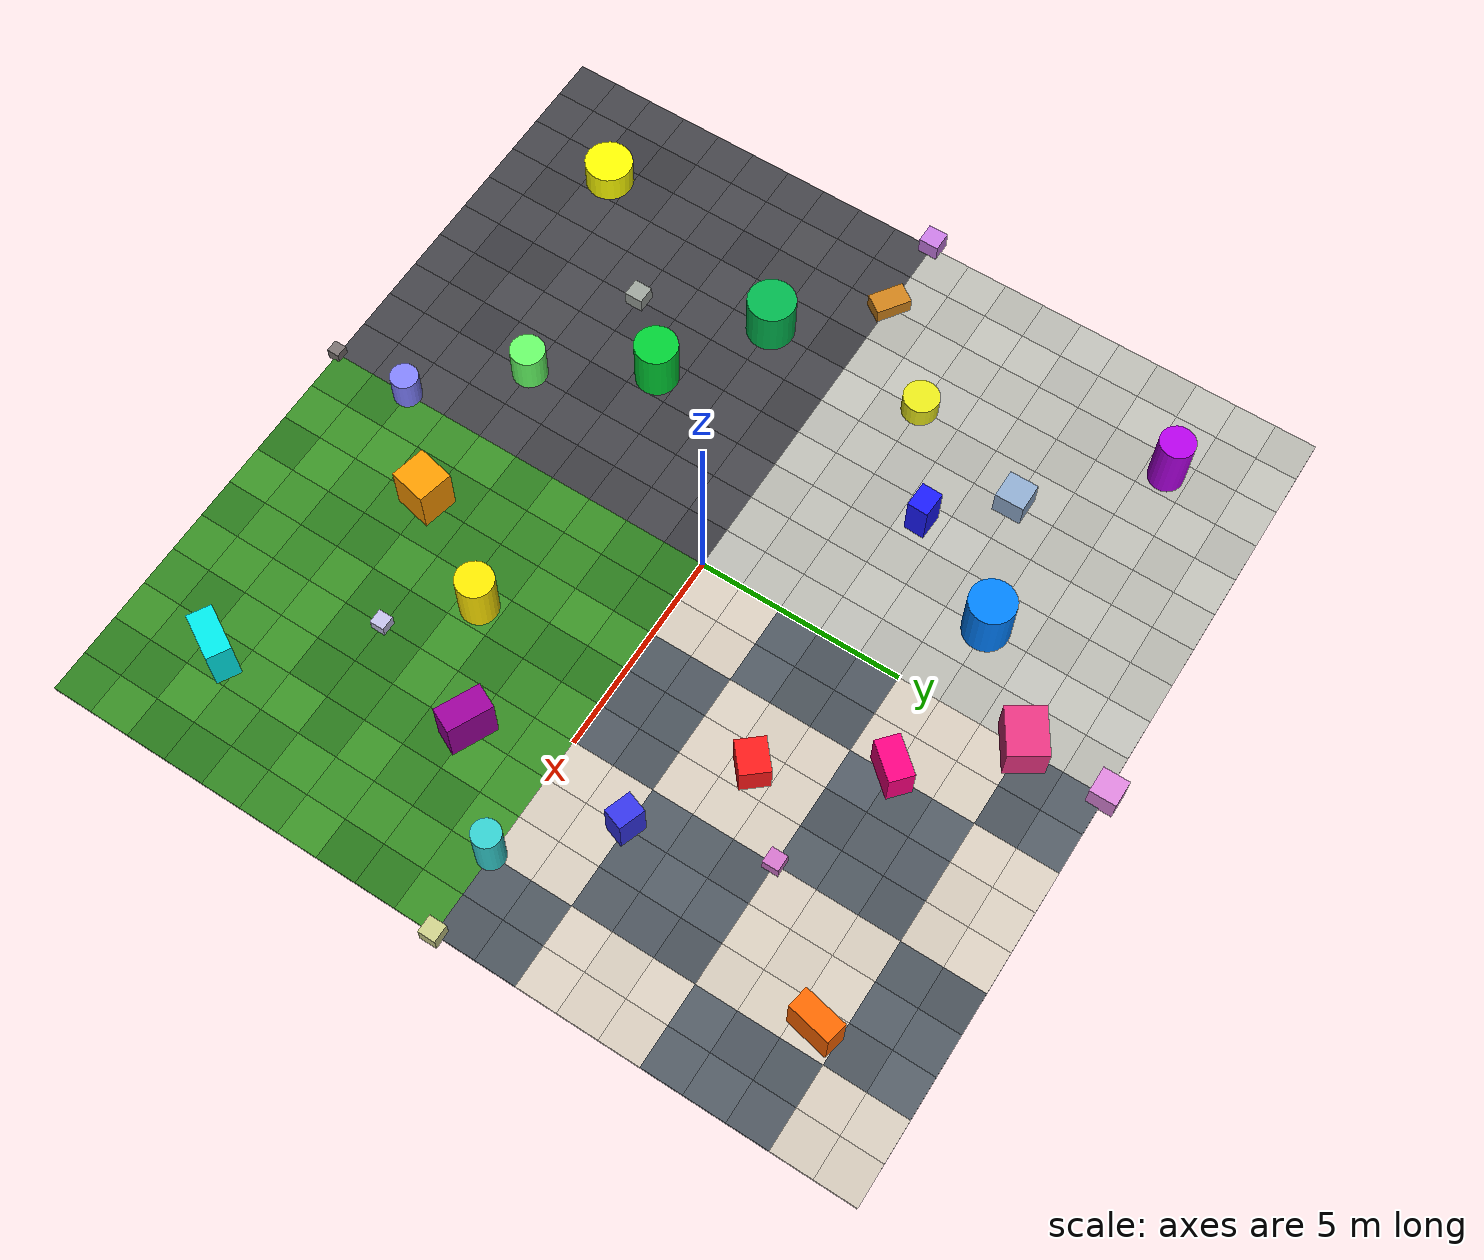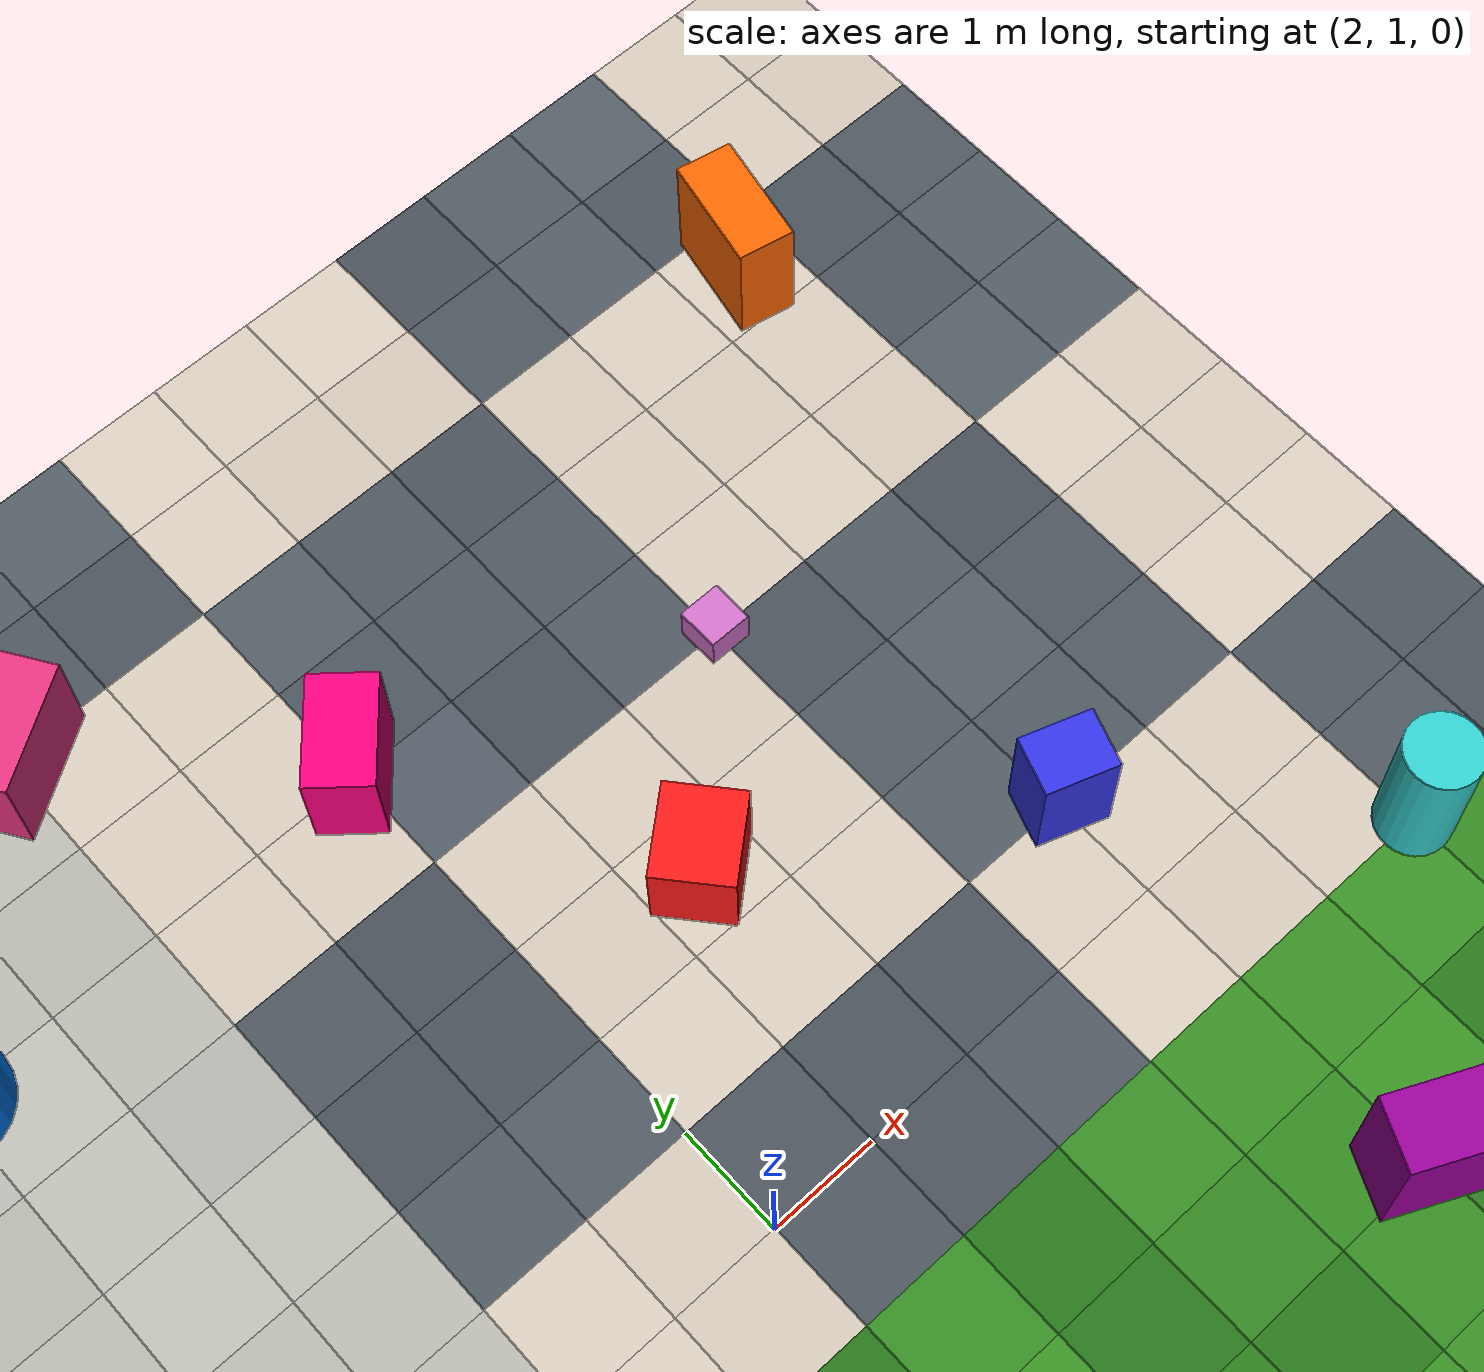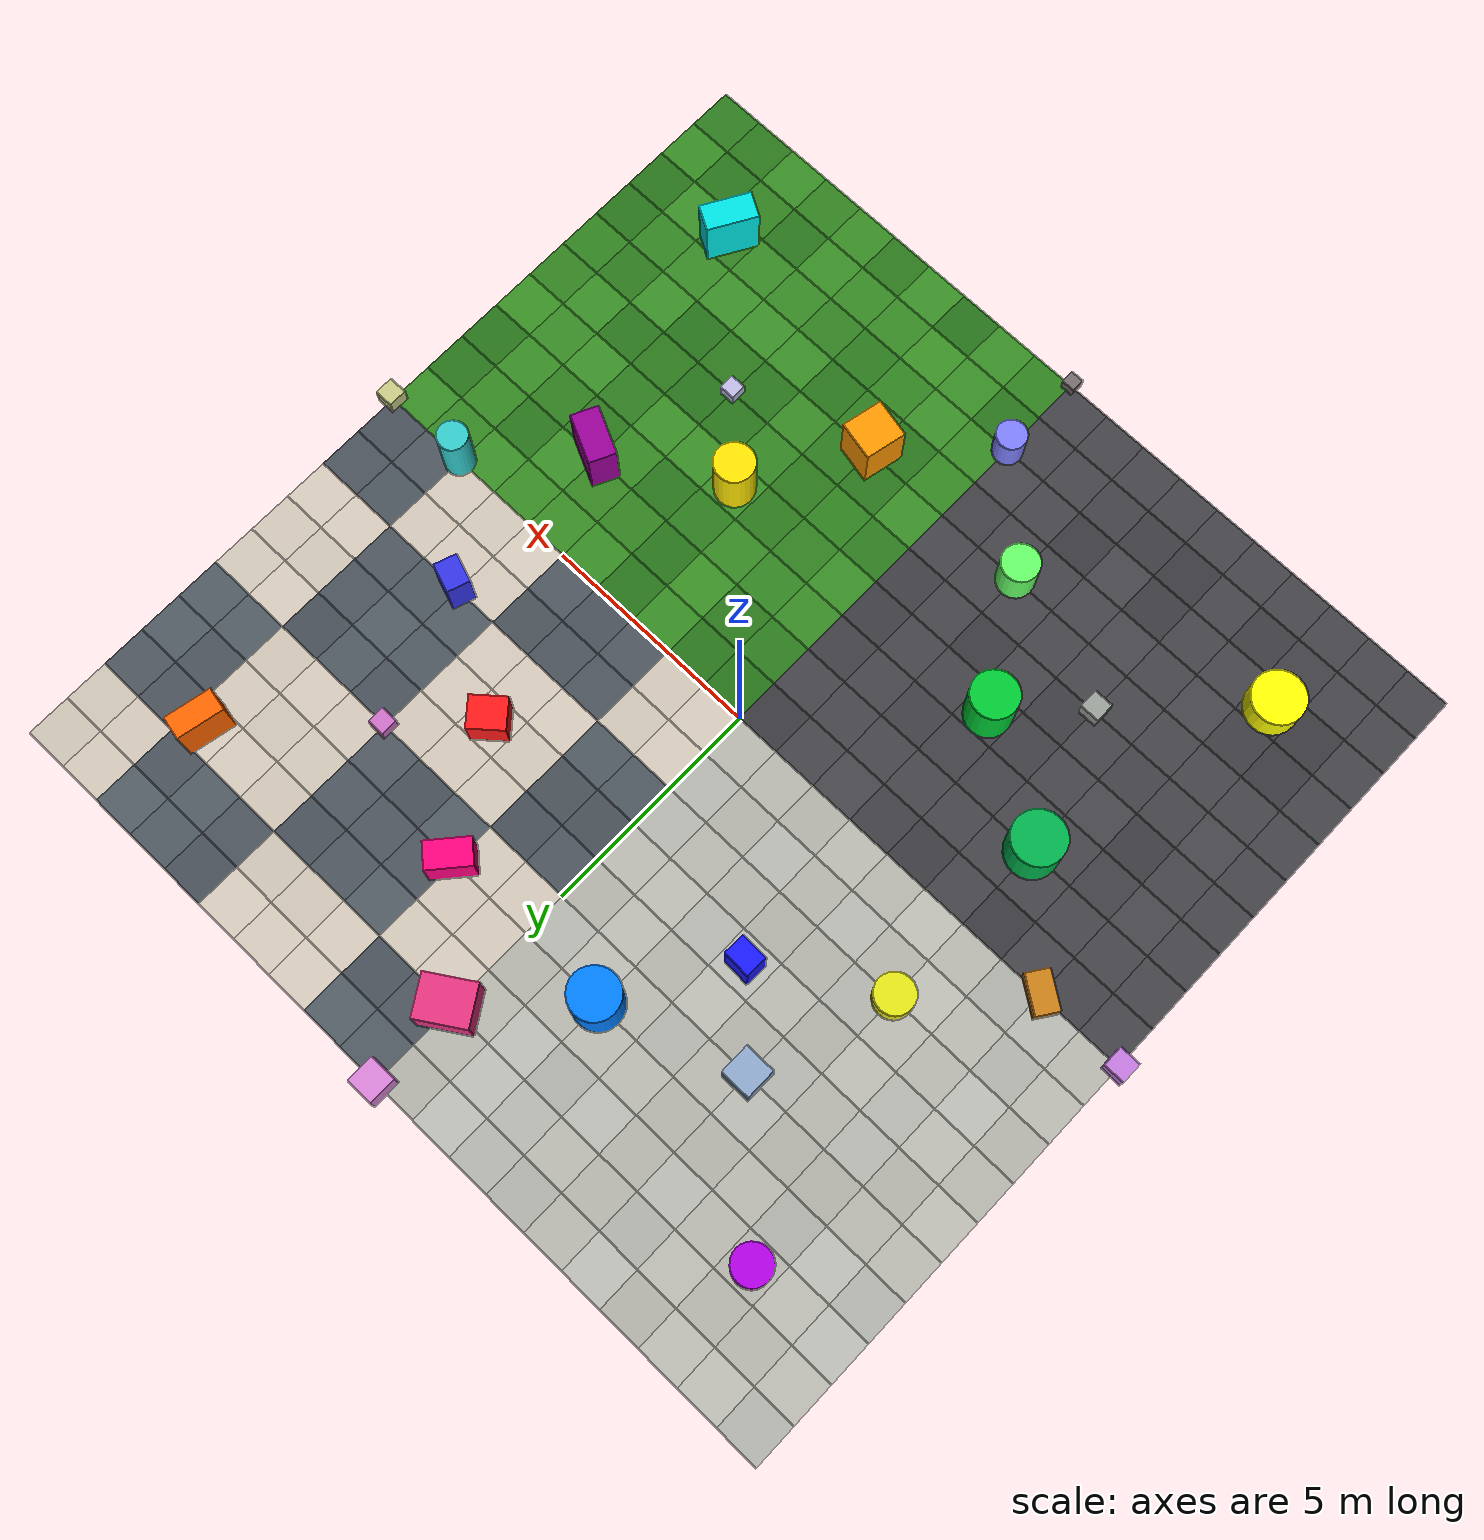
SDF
<?xml version="1.0" ?>
<sdf version="1.9">
  <world name="competition_world">

    <!-- Sistem plugin'leri -->
    <plugin filename="gz-sim-physics-system"
            name="gz::sim::systems::Physics"/>
    <plugin filename="gz-sim-user-commands-system"
            name="gz::sim::systems::UserCommands"/>
    <plugin filename="gz-sim-scene-broadcaster-system"
            name="gz::sim::systems::SceneBroadcaster"/>
    <plugin filename="gz-sim-sensors-system"
            name="gz::sim::systems::Sensors">
      <render_engine>ogre2</render_engine>
    </plugin>

    <gravity>0 0 -9.8</gravity>

    <scene>
      <ambient>0.35 0.35 0.35 1</ambient>
      <background>0.5 0.7 1.0 1</background>
      <shadows>true</shadows>
    </scene>

    <!-- Ana güneş ışığı: cast_shadows, açılı -->
    <light name="sun" type="directional">
      <cast_shadows>true</cast_shadows>
      <pose>0 0 20 0 0 0</pose>
      <direction>-0.6 0.25 -1.0</direction>
      <diffuse>1.0 0.96 0.88 1</diffuse>
      <specular>0.4 0.38 0.35 1</specular>
      <attenuation><range>1000</range><linear>0.001</linear></attenuation>
    </light>

    <!-- Fill light: yumuşak karşı aydınlatma (exposure variation simülasyonu) -->
    <light name="fill_light" type="directional">
      <cast_shadows>false</cast_shadows>
      <pose>0 0 15 0 0 0</pose>
      <direction>0.5 -0.3 -0.8</direction>
      <diffuse>0.30 0.32 0.38 1</diffuse>
      <specular>0.05 0.05 0.05 1</specular>
      <attenuation><range>1000</range><linear>0.005</linear></attenuation>
    </light>

    <model name="t_00_00">
      <static>true</static>
      <pose>-9.500 -9.500 0.025 0 0 0</pose>
      <link name="link">
        <collision name="c"><geometry><box><size>1.00 1.00 0.05</size></box></geometry></collision>
        <visual name="v"><geometry><box><size>1.00 1.00 0.05</size></box></geometry>
          <material><ambient>0.260 0.260 0.280 1</ambient><diffuse>0.260 0.260 0.280 1</diffuse><specular>0.060 0.060 0.060 1</specular></material></visual>
      </link>
    </model>

    <model name="t_00_01">
      <static>true</static>
      <pose>-8.500 -9.500 0.025 0 0 0</pose>
      <link name="link">
        <collision name="c"><geometry><box><size>1.00 1.00 0.05</size></box></geometry></collision>
        <visual name="v"><geometry><box><size>1.00 1.00 0.05</size></box></geometry>
          <material><ambient>0.260 0.260 0.280 1</ambient><diffuse>0.260 0.260 0.280 1</diffuse><specular>0.060 0.060 0.060 1</specular></material></visual>
      </link>
    </model>

    <model name="t_00_02">
      <static>true</static>
      <pose>-7.500 -9.500 0.025 0 0 0</pose>
      <link name="link">
        <collision name="c"><geometry><box><size>1.00 1.00 0.05</size></box></geometry></collision>
        <visual name="v"><geometry><box><size>1.00 1.00 0.05</size></box></geometry>
          <material><ambient>0.260 0.260 0.280 1</ambient><diffuse>0.260 0.260 0.280 1</diffuse><specular>0.060 0.060 0.060 1</specular></material></visual>
      </link>
    </model>

    <model name="t_00_03">
      <static>true</static>
      <pose>-6.500 -9.500 0.025 0 0 0</pose>
      <link name="link">
        <collision name="c"><geometry><box><size>1.00 1.00 0.05</size></box></geometry></collision>
        <visual name="v"><geometry><box><size>1.00 1.00 0.05</size></box></geometry>
          <material><ambient>0.260 0.260 0.280 1</ambient><diffuse>0.260 0.260 0.280 1</diffuse><specular>0.060 0.060 0.060 1</specular></material></visual>
      </link>
    </model>

    <model name="t_00_04">
      <static>true</static>
      <pose>-5.500 -9.500 0.025 0 0 0</pose>
      <link name="link">
        <collision name="c"><geometry><box><size>1.00 1.00 0.05</size></box></geometry></collision>
        <visual name="v"><geometry><box><size>1.00 1.00 0.05</size></box></geometry>
          <material><ambient>0.260 0.260 0.280 1</ambient><diffuse>0.260 0.260 0.280 1</diffuse><specular>0.060 0.060 0.060 1</specular></material></visual>
      </link>
    </model>

    <model name="t_00_05">
      <static>true</static>
      <pose>-4.500 -9.500 0.025 0 0 0</pose>
      <link name="link">
        <collision name="c"><geometry><box><size>1.00 1.00 0.05</size></box></geometry></collision>
        <visual name="v"><geometry><box><size>1.00 1.00 0.05</size></box></geometry>
          <material><ambient>0.260 0.260 0.280 1</ambient><diffuse>0.260 0.260 0.280 1</diffuse><specular>0.060 0.060 0.060 1</specular></material></visual>
      </link>
    </model>

    <model name="t_00_06">
      <static>true</static>
      <pose>-3.500 -9.500 0.025 0 0 0</pose>
      <link name="link">
        <collision name="c"><geometry><box><size>1.00 1.00 0.05</size></box></geometry></collision>
        <visual name="v"><geometry><box><size>1.00 1.00 0.05</size></box></geometry>
          <material><ambient>0.260 0.260 0.280 1</ambient><diffuse>0.260 0.260 0.280 1</diffuse><specular>0.060 0.060 0.060 1</specular></material></visual>
      </link>
    </model>

    <model name="t_00_07">
      <static>true</static>
      <pose>-2.500 -9.500 0.025 0 0 0</pose>
      <link name="link">
        <collision name="c"><geometry><box><size>1.00 1.00 0.05</size></box></geometry></collision>
        <visual name="v"><geometry><box><size>1.00 1.00 0.05</size></box></geometry>
          <material><ambient>0.260 0.260 0.280 1</ambient><diffuse>0.260 0.260 0.280 1</diffuse><specular>0.060 0.060 0.060 1</specular></material></visual>
      </link>
    </model>

    <model name="t_00_08">
      <static>true</static>
      <pose>-1.500 -9.500 0.025 0 0 0</pose>
      <link name="link">
        <collision name="c"><geometry><box><size>1.00 1.00 0.05</size></box></geometry></collision>
        <visual name="v"><geometry><box><size>1.00 1.00 0.05</size></box></geometry>
          <material><ambient>0.260 0.260 0.280 1</ambient><diffuse>0.260 0.260 0.280 1</diffuse><specular>0.060 0.060 0.060 1</specular></material></visual>
      </link>
    </model>

    <model name="t_00_09">
      <static>true</static>
      <pose>-0.500 -9.500 0.025 0 0 0</pose>
      <link name="link">
        <collision name="c"><geometry><box><size>1.00 1.00 0.05</size></box></geometry></collision>
        <visual name="v"><geometry><box><size>1.00 1.00 0.05</size></box></geometry>
          <material><ambient>0.260 0.260 0.280 1</ambient><diffuse>0.260 0.260 0.280 1</diffuse><specular>0.060 0.060 0.060 1</specular></material></visual>
      </link>
    </model>

    <model name="t_00_10">
      <static>true</static>
      <pose>0.500 -9.500 0.025 0 0 0</pose>
      <link name="link">
        <collision name="c"><geometry><box><size>1.00 1.00 0.05</size></box></geometry></collision>
        <visual name="v"><geometry><box><size>1.00 1.00 0.05</size></box></geometry>
          <material><ambient>0.190 0.510 0.125 1</ambient><diffuse>0.190 0.510 0.125 1</diffuse><specular>0.060 0.060 0.060 1</specular></material></visual>
      </link>
    </model>

    <model name="t_00_11">
      <static>true</static>
      <pose>1.500 -9.500 0.025 0 0 0</pose>
      <link name="link">
        <collision name="c"><geometry><box><size>1.00 1.00 0.05</size></box></geometry></collision>
        <visual name="v"><geometry><box><size>1.00 1.00 0.05</size></box></geometry>
          <material><ambient>0.218 0.552 0.143 1</ambient><diffuse>0.218 0.552 0.143 1</diffuse><specular>0.060 0.060 0.060 1</specular></material></visual>
      </link>
    </model>

    <model name="t_00_12">
      <static>true</static>
      <pose>2.500 -9.500 0.025 0 0 0</pose>
      <link name="link">
        <collision name="c"><geometry><box><size>1.00 1.00 0.05</size></box></geometry></collision>
        <visual name="v"><geometry><box><size>1.00 1.00 0.05</size></box></geometry>
          <material><ambient>0.152 0.453 0.101 1</ambient><diffuse>0.152 0.453 0.101 1</diffuse><specular>0.060 0.060 0.060 1</specular></material></visual>
      </link>
    </model>

    <model name="t_00_13">
      <static>true</static>
      <pose>3.500 -9.500 0.025 0 0 0</pose>
      <link name="link">
        <collision name="c"><geometry><box><size>1.00 1.00 0.05</size></box></geometry></collision>
        <visual name="v"><geometry><box><size>1.00 1.00 0.05</size></box></geometry>
          <material><ambient>0.227 0.565 0.148 1</ambient><diffuse>0.227 0.565 0.148 1</diffuse><specular>0.060 0.060 0.060 1</specular></material></visual>
      </link>
    </model>

    <model name="t_00_14">
      <static>true</static>
      <pose>4.500 -9.500 0.025 0 0 0</pose>
      <link name="link">
        <collision name="c"><geometry><box><size>1.00 1.00 0.05</size></box></geometry></collision>
        <visual name="v"><geometry><box><size>1.00 1.00 0.05</size></box></geometry>
          <material><ambient>0.164 0.471 0.109 1</ambient><diffuse>0.164 0.471 0.109 1</diffuse><specular>0.060 0.060 0.060 1</specular></material></visual>
      </link>
    </model>

    <model name="t_00_15">
      <static>true</static>
      <pose>5.500 -9.500 0.025 0 0 0</pose>
      <link name="link">
        <collision name="c"><geometry><box><size>1.00 1.00 0.05</size></box></geometry></collision>
        <visual name="v"><geometry><box><size>1.00 1.00 0.05</size></box></geometry>
          <material><ambient>0.215 0.548 0.141 1</ambient><diffuse>0.215 0.548 0.141 1</diffuse><specular>0.060 0.060 0.060 1</specular></material></visual>
      </link>
    </model>

    <model name="t_00_16">
      <static>true</static>
      <pose>6.500 -9.500 0.025 0 0 0</pose>
      <link name="link">
        <collision name="c"><geometry><box><size>1.00 1.00 0.05</size></box></geometry></collision>
        <visual name="v"><geometry><box><size>1.00 1.00 0.05</size></box></geometry>
          <material><ambient>0.191 0.511 0.125 1</ambient><diffuse>0.191 0.511 0.125 1</diffuse><specular>0.060 0.060 0.060 1</specular></material></visual>
      </link>
    </model>

    <model name="t_00_17">
      <static>true</static>
      <pose>7.500 -9.500 0.025 0 0 0</pose>
      <link name="link">
        <collision name="c"><geometry><box><size>1.00 1.00 0.05</size></box></geometry></collision>
        <visual name="v"><geometry><box><size>1.00 1.00 0.05</size></box></geometry>
          <material><ambient>0.217 0.550 0.142 1</ambient><diffuse>0.217 0.550 0.142 1</diffuse><specular>0.060 0.060 0.060 1</specular></material></visual>
      </link>
    </model>

    <model name="t_00_18">
      <static>true</static>
      <pose>8.500 -9.500 0.025 0 0 0</pose>
      <link name="link">
        <collision name="c"><geometry><box><size>1.00 1.00 0.05</size></box></geometry></collision>
        <visual name="v"><geometry><box><size>1.00 1.00 0.05</size></box></geometry>
          <material><ambient>0.165 0.472 0.109 1</ambient><diffuse>0.165 0.472 0.109 1</diffuse><specular>0.060 0.060 0.060 1</specular></material></visual>
      </link>
    </model>

    <model name="t_00_19">
      <static>true</static>
      <pose>9.500 -9.500 0.025 0 0 0</pose>
      <link name="link">
        <collision name="c"><geometry><box><size>1.00 1.00 0.05</size></box></geometry></collision>
        <visual name="v"><geometry><box><size>1.00 1.00 0.05</size></box></geometry>
          <material><ambient>0.176 0.489 0.116 1</ambient><diffuse>0.176 0.489 0.116 1</diffuse><specular>0.060 0.060 0.060 1</specular></material></visual>
      </link>
    </model>

    <model name="t_01_00">
      <static>true</static>
      <pose>-9.500 -8.500 0.025 0 0 0</pose>
      <link name="link">
        <collision name="c"><geometry><box><size>1.00 1.00 0.05</size></box></geometry></collision>
        <visual name="v"><geometry><box><size>1.00 1.00 0.05</size></box></geometry>
          <material><ambient>0.260 0.260 0.280 1</ambient><diffuse>0.260 0.260 0.280 1</diffuse><specular>0.060 0.060 0.060 1</specular></material></visual>
      </link>
    </model>

    <model name="t_01_01">
      <static>true</static>
      <pose>-8.500 -8.500 0.025 0 0 0</pose>
      <link name="link">
        <collision name="c"><geometry><box><size>1.00 1.00 0.05</size></box></geometry></collision>
        <visual name="v"><geometry><box><size>1.00 1.00 0.05</size></box></geometry>
          <material><ambient>0.259 0.259 0.279 1</ambient><diffuse>0.259 0.259 0.279 1</diffuse><specular>0.060 0.060 0.060 1</specular></material></visual>
      </link>
    </model>

    <model name="t_01_02">
      <static>true</static>
      <pose>-7.500 -8.500 0.025 0 0 0</pose>
      <link name="link">
        <collision name="c"><geometry><box><size>1.00 1.00 0.05</size></box></geometry></collision>
        <visual name="v"><geometry><box><size>1.00 1.00 0.05</size></box></geometry>
          <material><ambient>0.247 0.247 0.267 1</ambient><diffuse>0.247 0.247 0.267 1</diffuse><specular>0.060 0.060 0.060 1</specular></material></visual>
      </link>
    </model>

    <model name="t_01_03">
      <static>true</static>
      <pose>-6.500 -8.500 0.025 0 0 0</pose>
      <link name="link">
        <collision name="c"><geometry><box><size>1.00 1.00 0.05</size></box></geometry></collision>
        <visual name="v"><geometry><box><size>1.00 1.00 0.05</size></box></geometry>
          <material><ambient>0.230 0.230 0.250 1</ambient><diffuse>0.230 0.230 0.250 1</diffuse><specular>0.060 0.060 0.060 1</specular></material></visual>
      </link>
    </model>

    <model name="t_01_04">
      <static>true</static>
      <pose>-5.500 -8.500 0.025 0 0 0</pose>
      <link name="link">
        <collision name="c"><geometry><box><size>1.00 1.00 0.05</size></box></geometry></collision>
        <visual name="v"><geometry><box><size>1.00 1.00 0.05</size></box></geometry>
          <material><ambient>0.260 0.260 0.280 1</ambient><diffuse>0.260 0.260 0.280 1</diffuse><specular>0.060 0.060 0.060 1</specular></material></visual>
      </link>
    </model>

    <model name="t_01_05">
      <static>true</static>
      <pose>-4.500 -8.500 0.025 0 0 0</pose>
      <link name="link">
        <collision name="c"><geometry><box><size>1.00 1.00 0.05</size></box></geometry></collision>
        <visual name="v"><geometry><box><size>1.00 1.00 0.05</size></box></geometry>
          <material><ambient>0.224 0.224 0.244 1</ambient><diffuse>0.224 0.224 0.244 1</diffuse><specular>0.060 0.060 0.060 1</specular></material></visual>
      </link>
    </model>

    <model name="t_01_06">
      <static>true</static>
      <pose>-3.500 -8.500 0.025 0 0 0</pose>
      <link name="link">
        <collision name="c"><geometry><box><size>1.00 1.00 0.05</size></box></geometry></collision>
        <visual name="v"><geometry><box><size>1.00 1.00 0.05</size></box></geometry>
          <material><ambient>0.230 0.230 0.250 1</ambient><diffuse>0.230 0.230 0.250 1</diffuse><specular>0.060 0.060 0.060 1</specular></material></visual>
      </link>
    </model>

    <model name="t_01_07">
      <static>true</static>
      <pose>-2.500 -8.500 0.025 0 0 0</pose>
      <link name="link">
        <collision name="c"><geometry><box><size>1.00 1.00 0.05</size></box></geometry></collision>
        <visual name="v"><geometry><box><size>1.00 1.00 0.05</size></box></geometry>
          <material><ambient>0.248 0.248 0.268 1</ambient><diffuse>0.248 0.248 0.268 1</diffuse><specular>0.060 0.060 0.060 1</specular></material></visual>
      </link>
    </model>

    <model name="t_01_08">
      <static>true</static>
      <pose>-1.500 -8.500 0.025 0 0 0</pose>
      <link name="link">
        <collision name="c"><geometry><box><size>1.00 1.00 0.05</size></box></geometry></collision>
        <visual name="v"><geometry><box><size>1.00 1.00 0.05</size></box></geometry>
          <material><ambient>0.260 0.260 0.280 1</ambient><diffuse>0.260 0.260 0.280 1</diffuse><specular>0.060 0.060 0.060 1</specular></material></visual>
      </link>
    </model>

    <model name="t_01_09">
      <static>true</static>
      <pose>-0.500 -8.500 0.025 0 0 0</pose>
      <link name="link">
        <collision name="c"><geometry><box><size>1.00 1.00 0.05</size></box></geometry></collision>
        <visual name="v"><geometry><box><size>1.00 1.00 0.05</size></box></geometry>
          <material><ambient>0.255 0.255 0.275 1</ambient><diffuse>0.255 0.255 0.275 1</diffuse><specular>0.060 0.060 0.060 1</specular></material></visual>
      </link>
    </model>

    <model name="t_01_10">
      <static>true</static>
      <pose>0.500 -8.500 0.025 0 0 0</pose>
      <link name="link">
        <collision name="c"><geometry><box><size>1.00 1.00 0.05</size></box></geometry></collision>
        <visual name="v"><geometry><box><size>1.00 1.00 0.05</size></box></geometry>
          <material><ambient>0.156 0.459 0.104 1</ambient><diffuse>0.156 0.459 0.104 1</diffuse><specular>0.060 0.060 0.060 1</specular></material></visual>
      </link>
    </model>

    <model name="t_01_11">
      <static>true</static>
      <pose>1.500 -8.500 0.025 0 0 0</pose>
      <link name="link">
        <collision name="c"><geometry><box><size>1.00 1.00 0.05</size></box></geometry></collision>
        <visual name="v"><geometry><box><size>1.00 1.00 0.05</size></box></geometry>
          <material><ambient>0.217 0.551 0.142 1</ambient><diffuse>0.217 0.551 0.142 1</diffuse><specular>0.060 0.060 0.060 1</specular></material></visual>
      </link>
    </model>

    <model name="t_01_12">
      <static>true</static>
      <pose>2.500 -8.500 0.025 0 0 0</pose>
      <link name="link">
        <collision name="c"><geometry><box><size>1.00 1.00 0.05</size></box></geometry></collision>
        <visual name="v"><geometry><box><size>1.00 1.00 0.05</size></box></geometry>
          <material><ambient>0.229 0.568 0.149 1</ambient><diffuse>0.229 0.568 0.149 1</diffuse><specular>0.060 0.060 0.060 1</specular></material></visual>
      </link>
    </model>

    <model name="t_01_13">
      <static>true</static>
      <pose>3.500 -8.500 0.025 0 0 0</pose>
      <link name="link">
        <collision name="c"><geometry><box><size>1.00 1.00 0.05</size></box></geometry></collision>
        <visual name="v"><geometry><box><size>1.00 1.00 0.05</size></box></geometry>
          <material><ambient>0.209 0.539 0.137 1</ambient><diffuse>0.209 0.539 0.137 1</diffuse><specular>0.060 0.060 0.060 1</specular></material></visual>
      </link>
    </model>

    <model name="t_01_14">
      <static>true</static>
      <pose>4.500 -8.500 0.025 0 0 0</pose>
      <link name="link">
        <collision name="c"><geometry><box><size>1.00 1.00 0.05</size></box></geometry></collision>
        <visual name="v"><geometry><box><size>1.00 1.00 0.05</size></box></geometry>
          <material><ambient>0.209 0.539 0.137 1</ambient><diffuse>0.209 0.539 0.137 1</diffuse><specular>0.060 0.060 0.060 1</specular></material></visual>
      </link>
    </model>

    <model name="t_01_15">
      <static>true</static>
      <pose>5.500 -8.500 0.025 0 0 0</pose>
      <link name="link">
        <collision name="c"><geometry><box><size>1.00 1.00 0.05</size></box></geometry></collision>
        <visual name="v"><geometry><box><size>1.00 1.00 0.05</size></box></geometry>
          <material><ambient>0.218 0.552 0.142 1</ambient><diffuse>0.218 0.552 0.142 1</diffuse><specular>0.060 0.060 0.060 1</specular></material></visual>
      </link>
    </model>

    <model name="t_01_16">
      <static>true</static>
      <pose>6.500 -8.500 0.025 0 0 0</pose>
      <link name="link">
        <collision name="c"><geometry><box><size>1.00 1.00 0.05</size></box></geometry></collision>
        <visual name="v"><geometry><box><size>1.00 1.00 0.05</size></box></geometry>
          <material><ambient>0.158 0.461 0.105 1</ambient><diffuse>0.158 0.461 0.105 1</diffuse><specular>0.060 0.060 0.060 1</specular></material></visual>
      </link>
    </model>

    <model name="t_01_17">
      <static>true</static>
      <pose>7.500 -8.500 0.025 0 0 0</pose>
      <link name="link">
        <collision name="c"><geometry><box><size>1.00 1.00 0.05</size></box></geometry></collision>
        <visual name="v"><geometry><box><size>1.00 1.00 0.05</size></box></geometry>
          <material><ambient>0.187 0.505 0.123 1</ambient><diffuse>0.187 0.505 0.123 1</diffuse><specular>0.060 0.060 0.060 1</specular></material></visual>
      </link>
    </model>

    <model name="t_01_18">
      <static>true</static>
      <pose>8.500 -8.500 0.025 0 0 0</pose>
      <link name="link">
        <collision name="c"><geometry><box><size>1.00 1.00 0.05</size></box></geometry></collision>
        <visual name="v"><geometry><box><size>1.00 1.00 0.05</size></box></geometry>
          <material><ambient>0.156 0.460 0.104 1</ambient><diffuse>0.156 0.460 0.104 1</diffuse><specular>0.060 0.060 0.060 1</specular></material></visual>
      </link>
    </model>

    <model name="t_01_19">
      <static>true</static>
      <pose>9.500 -8.500 0.025 0 0 0</pose>
      <link name="link">
        <collision name="c"><geometry><box><size>1.00 1.00 0.05</size></box></geometry></collision>
        <visual name="v"><geometry><box><size>1.00 1.00 0.05</size></box></geometry>
          <material><ambient>0.213 0.544 0.139 1</ambient><diffuse>0.213 0.544 0.139 1</diffuse><specular>0.060 0.060 0.060 1</specular></material></visual>
      </link>
    </model>

    <model name="t_02_00">
      <static>true</static>
      <pose>-9.500 -7.500 0.025 0 0 0</pose>
      <link name="link">
        <collision name="c"><geometry><box><size>1.00 1.00 0.05</size></box></geometry></collision>
        <visual name="v"><geometry><box><size>1.00 1.00 0.05</size></box></geometry>
          <material><ambient>0.260 0.260 0.280 1</ambient><diffuse>0.260 0.260 0.280 1</diffuse><specular>0.060 0.060 0.060 1</specular></material></visual>
      </link>
    </model>

    <model name="t_02_01">
      <static>true</static>
      <pose>-8.500 -7.500 0.025 0 0 0</pose>
      <link name="link">
        <collision name="c"><geometry><box><size>1.00 1.00 0.05</size></box></geometry></collision>
        <visual name="v"><geometry><box><size>1.00 1.00 0.05</size></box></geometry>
          <material><ambient>0.225 0.225 0.245 1</ambient><diffuse>0.225 0.225 0.245 1</diffuse><specular>0.060 0.060 0.060 1</specular></material></visual>
      </link>
    </model>

    <model name="t_02_02">
      <static>true</static>
      <pose>-7.500 -7.500 0.025 0 0 0</pose>
      <link name="link">
        <collision name="c"><geometry><box><size>1.00 1.00 0.05</size></box></geometry></collision>
        <visual name="v"><geometry><box><size>1.00 1.00 0.05</size></box></geometry>
          <material><ambient>0.242 0.242 0.262 1</ambient><diffuse>0.242 0.242 0.262 1</diffuse><specular>0.060 0.060 0.060 1</specular></material></visual>
      </link>
    </model>

    <model name="t_02_03">
      <static>true</static>
      <pose>-6.500 -7.500 0.025 0 0 0</pose>
      <link name="link">
        <collision name="c"><geometry><box><size>1.00 1.00 0.05</size></box></geometry></collision>
        <visual name="v"><geometry><box><size>1.00 1.00 0.05</size></box></geometry>
          <material><ambient>0.259 0.259 0.279 1</ambient><diffuse>0.259 0.259 0.279 1</diffuse><specular>0.060 0.060 0.060 1</specular></material></visual>
      </link>
    </model>

    <model name="t_02_04">
      <static>true</static>
      <pose>-5.500 -7.500 0.025 0 0 0</pose>
      <link name="link">
        <collision name="c"><geometry><box><size>1.00 1.00 0.05</size></box></geometry></collision>
        <visual name="v"><geometry><box><size>1.00 1.00 0.05</size></box></geometry>
          <material><ambient>0.260 0.260 0.280 1</ambient><diffuse>0.260 0.260 0.280 1</diffuse><specular>0.060 0.060 0.060 1</specular></material></visual>
      </link>
    </model>

    <model name="t_02_05">
      <static>true</static>
      <pose>-4.500 -7.500 0.025 0 0 0</pose>
      <link name="link">
        <collision name="c"><geometry><box><size>1.00 1.00 0.05</size></box></geometry></collision>
        <visual name="v"><geometry><box><size>1.00 1.00 0.05</size></box></geometry>
          <material><ambient>0.226 0.226 0.246 1</ambient><diffuse>0.226 0.226 0.246 1</diffuse><specular>0.060 0.060 0.060 1</specular></material></visual>
      </link>
    </model>

    <model name="t_02_06">
      <static>true</static>
      <pose>-3.500 -7.500 0.025 0 0 0</pose>
      <link name="link">
        <collision name="c"><geometry><box><size>1.00 1.00 0.05</size></box></geometry></collision>
        <visual name="v"><geometry><box><size>1.00 1.00 0.05</size></box></geometry>
          <material><ambient>0.267 0.267 0.287 1</ambient><diffuse>0.267 0.267 0.287 1</diffuse><specular>0.060 0.060 0.060 1</specular></material></visual>
      </link>
    </model>

    <model name="t_02_07">
      <static>true</static>
      <pose>-2.500 -7.500 0.025 0 0 0</pose>
      <link name="link">
        <collision name="c"><geometry><box><size>1.00 1.00 0.05</size></box></geometry></collision>
        <visual name="v"><geometry><box><size>1.00 1.00 0.05</size></box></geometry>
          <material><ambient>0.223 0.223 0.243 1</ambient><diffuse>0.223 0.223 0.243 1</diffuse><specular>0.060 0.060 0.060 1</specular></material></visual>
      </link>
    </model>

    <model name="t_02_08">
      <static>true</static>
      <pose>-1.500 -7.500 0.025 0 0 0</pose>
      <link name="link">
        <collision name="c"><geometry><box><size>1.00 1.00 0.05</size></box></geometry></collision>
        <visual name="v"><geometry><box><size>1.00 1.00 0.05</size></box></geometry>
          <material><ambient>0.260 0.260 0.280 1</ambient><diffuse>0.260 0.260 0.280 1</diffuse><specular>0.060 0.060 0.060 1</specular></material></visual>
      </link>
    </model>

    <model name="t_02_09">
      <static>true</static>
      <pose>-0.500 -7.500 0.025 0 0 0</pose>
      <link name="link">
        <collision name="c"><geometry><box><size>1.00 1.00 0.05</size></box></geometry></collision>
        <visual name="v"><geometry><box><size>1.00 1.00 0.05</size></box></geometry>
          <material><ambient>0.269 0.269 0.289 1</ambient><diffuse>0.269 0.269 0.289 1</diffuse><specular>0.060 0.060 0.060 1</specular></material></visual>
      </link>
    </model>

    <model name="t_02_10">
      <static>true</static>
      <pose>0.500 -7.500 0.025 0 0 0</pose>
      <link name="link">
        <collision name="c"><geometry><box><size>1.00 1.00 0.05</size></box></geometry></collision>
        <visual name="v"><geometry><box><size>1.00 1.00 0.05</size></box></geometry>
          <material><ambient>0.210 0.540 0.138 1</ambient><diffuse>0.210 0.540 0.138 1</diffuse><specular>0.060 0.060 0.060 1</specular></material></visual>
      </link>
    </model>

    <model name="t_02_11">
      <static>true</static>
      <pose>1.500 -7.500 0.025 0 0 0</pose>
      <link name="link">
        <collision name="c"><geometry><box><size>1.00 1.00 0.05</size></box></geometry></collision>
        <visual name="v"><geometry><box><size>1.00 1.00 0.05</size></box></geometry>
          <material><ambient>0.226 0.564 0.147 1</ambient><diffuse>0.226 0.564 0.147 1</diffuse><specular>0.060 0.060 0.060 1</specular></material></visual>
      </link>
    </model>

    <model name="t_02_12">
      <static>true</static>
      <pose>2.500 -7.500 0.025 0 0 0</pose>
      <link name="link">
        <collision name="c"><geometry><box><size>1.00 1.00 0.05</size></box></geometry></collision>
        <visual name="v"><geometry><box><size>1.00 1.00 0.05</size></box></geometry>
          <material><ambient>0.192 0.514 0.127 1</ambient><diffuse>0.192 0.514 0.127 1</diffuse><specular>0.060 0.060 0.060 1</specular></material></visual>
      </link>
    </model>

    <model name="t_02_13">
      <static>true</static>
      <pose>3.500 -7.500 0.025 0 0 0</pose>
      <link name="link">
        <collision name="c"><geometry><box><size>1.00 1.00 0.05</size></box></geometry></collision>
        <visual name="v"><geometry><box><size>1.00 1.00 0.05</size></box></geometry>
          <material><ambient>0.168 0.476 0.111 1</ambient><diffuse>0.168 0.476 0.111 1</diffuse><specular>0.060 0.060 0.060 1</specular></material></visual>
      </link>
    </model>

    <model name="t_02_14">
      <static>true</static>
      <pose>4.500 -7.500 0.025 0 0 0</pose>
      <link name="link">
        <collision name="c"><geometry><box><size>1.00 1.00 0.05</size></box></geometry></collision>
        <visual name="v"><geometry><box><size>1.00 1.00 0.05</size></box></geometry>
          <material><ambient>0.188 0.507 0.124 1</ambient><diffuse>0.188 0.507 0.124 1</diffuse><specular>0.060 0.060 0.060 1</specular></material></visual>
      </link>
    </model>

    <model name="t_02_15">
      <static>true</static>
      <pose>5.500 -7.500 0.025 0 0 0</pose>
      <link name="link">
        <collision name="c"><geometry><box><size>1.00 1.00 0.05</size></box></geometry></collision>
        <visual name="v"><geometry><box><size>1.00 1.00 0.05</size></box></geometry>
          <material><ambient>0.209 0.539 0.137 1</ambient><diffuse>0.209 0.539 0.137 1</diffuse><specular>0.060 0.060 0.060 1</specular></material></visual>
      </link>
    </model>

    <model name="t_02_16">
      <static>true</static>
      <pose>6.500 -7.500 0.025 0 0 0</pose>
      <link name="link">
        <collision name="c"><geometry><box><size>1.00 1.00 0.05</size></box></geometry></collision>
        <visual name="v"><geometry><box><size>1.00 1.00 0.05</size></box></geometry>
          <material><ambient>0.211 0.542 0.138 1</ambient><diffuse>0.211 0.542 0.138 1</diffuse><specular>0.060 0.060 0.060 1</specular></material></visual>
      </link>
    </model>

    <model name="t_02_17">
      <static>true</static>
      <pose>7.500 -7.500 0.025 0 0 0</pose>
      <link name="link">
        <collision name="c"><geometry><box><size>1.00 1.00 0.05</size></box></geometry></collision>
        <visual name="v"><geometry><box><size>1.00 1.00 0.05</size></box></geometry>
          <material><ambient>0.181 0.496 0.119 1</ambient><diffuse>0.181 0.496 0.119 1</diffuse><specular>0.060 0.060 0.060 1</specular></material></visual>
      </link>
    </model>

    <model name="t_02_18">
      <static>true</static>
      <pose>8.500 -7.500 0.025 0 0 0</pose>
      <link name="link">
        <collision name="c"><geometry><box><size>1.00 1.00 0.05</size></box></geometry></collision>
        <visual name="v"><geometry><box><size>1.00 1.00 0.05</size></box></geometry>
          <material><ambient>0.226 0.564 0.147 1</ambient><diffuse>0.226 0.564 0.147 1</diffuse><specular>0.060 0.060 0.060 1</specular></material></visual>
      </link>
    </model>

    <model name="t_02_19">
      <static>true</static>
      <pose>9.500 -7.500 0.025 0 0 0</pose>
      <link name="link">
        <collision name="c"><geometry><box><size>1.00 1.00 0.05</size></box></geometry></collision>
        <visual name="v"><geometry><box><size>1.00 1.00 0.05</size></box></geometry>
          <material><ambient>0.153 0.454 0.102 1</ambient><diffuse>0.153 0.454 0.102 1</diffuse><specular>0.060 0.060 0.060 1</specular></material></visual>
      </link>
    </model>

    <model name="t_03_00">
      <static>true</static>
      <pose>-9.500 -6.500 0.025 0 0 0</pose>
      <link name="link">
        <collision name="c"><geometry><box><size>1.00 1.00 0.05</size></box></geometry></collision>
        <visual name="v"><geometry><box><size>1.00 1.00 0.05</size></box></geometry>
          <material><ambient>0.260 0.260 0.280 1</ambient><diffuse>0.260 0.260 0.280 1</diffuse><specular>0.060 0.060 0.060 1</specular></material></visual>
      </link>
    </model>

    <model name="t_03_01">
      <static>true</static>
      <pose>-8.500 -6.500 0.025 0 0 0</pose>
      <link name="link">
        <collision name="c"><geometry><box><size>1.00 1.00 0.05</size></box></geometry></collision>
        <visual name="v"><geometry><box><size>1.00 1.00 0.05</size></box></geometry>
          <material><ambient>0.222 0.222 0.242 1</ambient><diffuse>0.222 0.222 0.242 1</diffuse><specular>0.060 0.060 0.060 1</specular></material></visual>
      </link>
    </model>

    <model name="t_03_02">
      <static>true</static>
      <pose>-7.500 -6.500 0.025 0 0 0</pose>
      <link name="link">
        <collision name="c"><geometry><box><size>1.00 1.00 0.05</size></box></geometry></collision>
        <visual name="v"><geometry><box><size>1.00 1.00 0.05</size></box></geometry>
          <material><ambient>0.238 0.238 0.258 1</ambient><diffuse>0.238 0.238 0.258 1</diffuse><specular>0.060 0.060 0.060 1</specular></material></visual>
      </link>
    </model>

    <model name="t_03_03">
      <static>true</static>
      <pose>-6.500 -6.500 0.025 0 0 0</pose>
      <link name="link">
        <collision name="c"><geometry><box><size>1.00 1.00 0.05</size></box></geometry></collision>
        <visual name="v"><geometry><box><size>1.00 1.00 0.05</size></box></geometry>
          <material><ambient>0.269 0.269 0.289 1</ambient><diffuse>0.269 0.269 0.289 1</diffuse><specular>0.060 0.060 0.060 1</specular></material></visual>
      </link>
    </model>

    <model name="t_03_04">
      <static>true</static>
      <pose>-5.500 -6.500 0.025 0 0 0</pose>
      <link name="link">
        <collision name="c"><geometry><box><size>1.00 1.00 0.05</size></box></geometry></collision>
        <visual name="v"><geometry><box><size>1.00 1.00 0.05</size></box></geometry>
          <material><ambient>0.260 0.260 0.280 1</ambient><diffuse>0.260 0.260 0.280 1</diffuse><specular>0.060 0.060 0.060 1</specular></material></visual>
      </link>
    </model>

    <model name="t_03_05">
      <static>true</static>
      <pose>-4.500 -6.500 0.025 0 0 0</pose>
      <link name="link">
        <collision name="c"><geometry><box><size>1.00 1.00 0.05</size></box></geometry></collision>
        <visual name="v"><geometry><box><size>1.00 1.00 0.05</size></box></geometry>
          <material><ambient>0.269 0.269 0.289 1</ambient><diffuse>0.269 0.269 0.289 1</diffuse><specular>0.060 0.060 0.060 1</specular></material></visual>
      </link>
    </model>

    <model name="t_03_06">
      <static>true</static>
      <pose>-3.500 -6.500 0.025 0 0 0</pose>
      <link name="link">
        <collision name="c"><geometry><box><size>1.00 1.00 0.05</size></box></geometry></collision>
        <visual name="v"><geometry><box><size>1.00 1.00 0.05</size></box></geometry>
          <material><ambient>0.265 0.265 0.285 1</ambient><diffuse>0.265 0.265 0.285 1</diffuse><specular>0.060 0.060 0.060 1</specular></material></visual>
      </link>
    </model>

    <model name="t_03_07">
      <static>true</static>
      <pose>-2.500 -6.500 0.025 0 0 0</pose>
      <link name="link">
        <collision name="c"><geometry><box><size>1.00 1.00 0.05</size></box></geometry></collision>
        <visual name="v"><geometry><box><size>1.00 1.00 0.05</size></box></geometry>
          <material><ambient>0.254 0.254 0.274 1</ambient><diffuse>0.254 0.254 0.274 1</diffuse><specular>0.060 0.060 0.060 1</specular></material></visual>
      </link>
    </model>

    <model name="t_03_08">
      <static>true</static>
      <pose>-1.500 -6.500 0.025 0 0 0</pose>
      <link name="link">
        <collision name="c"><geometry><box><size>1.00 1.00 0.05</size></box></geometry></collision>
        <visual name="v"><geometry><box><size>1.00 1.00 0.05</size></box></geometry>
          <material><ambient>0.260 0.260 0.280 1</ambient><diffuse>0.260 0.260 0.280 1</diffuse><specular>0.060 0.060 0.060 1</specular></material></visual>
      </link>
    </model>

    <model name="t_03_09">
      <static>true</static>
      <pose>-0.500 -6.500 0.025 0 0 0</pose>
      <link name="link">
        <collision name="c"><geometry><box><size>1.00 1.00 0.05</size></box></geometry></collision>
        <visual name="v"><geometry><box><size>1.00 1.00 0.05</size></box></geometry>
          <material><ambient>0.244 0.244 0.264 1</ambient><diffuse>0.244 0.244 0.264 1</diffuse><specular>0.060 0.060 0.060 1</specular></material></visual>
      </link>
    </model>

    <model name="t_03_10">
      <static>true</static>
      <pose>0.500 -6.500 0.025 0 0 0</pose>
      <link name="link">
        <collision name="c"><geometry><box><size>1.00 1.00 0.05</size></box></geometry></collision>
        <visual name="v"><geometry><box><size>1.00 1.00 0.05</size></box></geometry>
          <material><ambient>0.205 0.533 0.135 1</ambient><diffuse>0.205 0.533 0.135 1</diffuse><specular>0.060 0.060 0.060 1</specular></material></visual>
      </link>
    </model>

    <model name="t_03_11">
      <static>true</static>
      <pose>1.500 -6.500 0.025 0 0 0</pose>
      <link name="link">
        <collision name="c"><geometry><box><size>1.00 1.00 0.05</size></box></geometry></collision>
        <visual name="v"><geometry><box><size>1.00 1.00 0.05</size></box></geometry>
          <material><ambient>0.158 0.461 0.105 1</ambient><diffuse>0.158 0.461 0.105 1</diffuse><specular>0.060 0.060 0.060 1</specular></material></visual>
      </link>
    </model>

    <model name="t_03_12">
      <static>true</static>
      <pose>2.500 -6.500 0.025 0 0 0</pose>
      <link name="link">
        <collision name="c"><geometry><box><size>1.00 1.00 0.05</size></box></geometry></collision>
        <visual name="v"><geometry><box><size>1.00 1.00 0.05</size></box></geometry>
          <material><ambient>0.174 0.486 0.115 1</ambient><diffuse>0.174 0.486 0.115 1</diffuse><specular>0.060 0.060 0.060 1</specular></material></visual>
      </link>
    </model>

    <model name="t_03_13">
      <static>true</static>
      <pose>3.500 -6.500 0.025 0 0 0</pose>
      <link name="link">
        <collision name="c"><geometry><box><size>1.00 1.00 0.05</size></box></geometry></collision>
        <visual name="v"><geometry><box><size>1.00 1.00 0.05</size></box></geometry>
          <material><ambient>0.157 0.461 0.105 1</ambient><diffuse>0.157 0.461 0.105 1</diffuse><specular>0.060 0.060 0.060 1</specular></material></visual>
      </link>
    </model>

    <model name="t_03_14">
      <static>true</static>
      <pose>4.500 -6.500 0.025 0 0 0</pose>
      <link name="link">
        <collision name="c"><geometry><box><size>1.00 1.00 0.05</size></box></geometry></collision>
        <visual name="v"><geometry><box><size>1.00 1.00 0.05</size></box></geometry>
          <material><ambient>0.217 0.551 0.142 1</ambient><diffuse>0.217 0.551 0.142 1</diffuse><specular>0.060 0.060 0.060 1</specular></material></visual>
      </link>
    </model>

    <model name="t_03_15">
      <static>true</static>
      <pose>5.500 -6.500 0.025 0 0 0</pose>
      <link name="link">
        <collision name="c"><geometry><box><size>1.00 1.00 0.05</size></box></geometry></collision>
        <visual name="v"><geometry><box><size>1.00 1.00 0.05</size></box></geometry>
          <material><ambient>0.223 0.560 0.146 1</ambient><diffuse>0.223 0.560 0.146 1</diffuse><specular>0.060 0.060 0.060 1</specular></material></visual>
      </link>
    </model>

    <model name="t_03_16">
      <static>true</static>
      <pose>6.500 -6.500 0.025 0 0 0</pose>
      <link name="link">
        <collision name="c"><geometry><box><size>1.00 1.00 0.05</size></box></geometry></collision>
        <visual name="v"><geometry><box><size>1.00 1.00 0.05</size></box></geometry>
          <material><ambient>0.224 0.561 0.146 1</ambient><diffuse>0.224 0.561 0.146 1</diffuse><specular>0.060 0.060 0.060 1</specular></material></visual>
      </link>
    </model>

    <model name="t_03_17">
      <static>true</static>
      <pose>7.500 -6.500 0.025 0 0 0</pose>
      <link name="link">
        <collision name="c"><geometry><box><size>1.00 1.00 0.05</size></box></geometry></collision>
        <visual name="v"><geometry><box><size>1.00 1.00 0.05</size></box></geometry>
          <material><ambient>0.210 0.540 0.138 1</ambient><diffuse>0.210 0.540 0.138 1</diffuse><specular>0.060 0.060 0.060 1</specular></material></visual>
      </link>
    </model>

    <model name="t_03_18">
      <static>true</static>
      <pose>8.500 -6.500 0.025 0 0 0</pose>
      <link name="link">
        <collision name="c"><geometry><box><size>1.00 1.00 0.05</size></box></geometry></collision>
        <visual name="v"><geometry><box><size>1.00 1.00 0.05</size></box></geometry>
          <material><ambient>0.196 0.519 0.129 1</ambient><diffuse>0.196 0.519 0.129 1</diffuse><specular>0.060 0.060 0.060 1</specular></material></visual>
      </link>
    </model>

    <model name="t_03_19">
      <static>true</static>
      <pose>9.500 -6.500 0.025 0 0 0</pose>
      <link name="link">
        <collision name="c"><geometry><box><size>1.00 1.00 0.05</size></box></geometry></collision>
        <visual name="v"><geometry><box><size>1.00 1.00 0.05</size></box></geometry>
          <material><ambient>0.155 0.457 0.103 1</ambient><diffuse>0.155 0.457 0.103 1</diffuse><specular>0.060 0.060 0.060 1</specular></material></visual>
      </link>
    </model>

    <model name="t_04_00">
      <static>true</static>
      <pose>-9.500 -5.500 0.025 0 0 0</pose>
      <link name="link">
        <collision name="c"><geometry><box><size>1.00 1.00 0.05</size></box></geometry></collision>
        <visual name="v"><geometry><box><size>1.00 1.00 0.05</size></box></geometry>
          <material><ambient>0.260 0.260 0.280 1</ambient><diffuse>0.260 0.260 0.280 1</diffuse><specular>0.060 0.060 0.060 1</specular></material></visual>
      </link>
    </model>

    <model name="t_04_01">
      <static>true</static>
      <pose>-8.500 -5.500 0.025 0 0 0</pose>
      <link name="link">
        <collision name="c"><geometry><box><size>1.00 1.00 0.05</size></box></geometry></collision>
        <visual name="v"><geometry><box><size>1.00 1.00 0.05</size></box></geometry>
          <material><ambient>0.260 0.260 0.280 1</ambient><diffuse>0.260 0.260 0.280 1</diffuse><specular>0.060 0.060 0.060 1</specular></material></visual>
      </link>
    </model>

    <model name="t_04_02">
      <static>true</static>
      <pose>-7.500 -5.500 0.025 0 0 0</pose>
      <link name="link">
        <collision name="c"><geometry><box><size>1.00 1.00 0.05</size></box></geometry></collision>
        <visual name="v"><geometry><box><size>1.00 1.00 0.05</size></box></geometry>
          <material><ambient>0.260 0.260 0.280 1</ambient><diffuse>0.260 0.260 0.280 1</diffuse><specular>0.060 0.060 0.060 1</specular></material></visual>
      </link>
    </model>

    <model name="t_04_03">
      <static>true</static>
      <pose>-6.500 -5.500 0.025 0 0 0</pose>
      <link name="link">
        <collision name="c"><geometry><box><size>1.00 1.00 0.05</size></box></geometry></collision>
        <visual name="v"><geometry><box><size>1.00 1.00 0.05</size></box></geometry>
          <material><ambient>0.260 0.260 0.280 1</ambient><diffuse>0.260 0.260 0.280 1</diffuse><specular>0.060 0.060 0.060 1</specular></material></visual>
      </link>
    </model>

    <model name="t_04_04">
      <static>true</static>
      <pose>-5.500 -5.500 0.025 0 0 0</pose>
      <link name="link">
        <collision name="c"><geometry><box><size>1.00 1.00 0.05</size></box></geometry></collision>
        <visual name="v"><geometry><box><size>1.00 1.00 0.05</size></box></geometry>
          <material><ambient>0.260 0.260 0.280 1</ambient><diffuse>0.260 0.260 0.280 1</diffuse><specular>0.060 0.060 0.060 1</specular></material></visual>
      </link>
    </model>

    <model name="t_04_05">
      <static>true</static>
      <pose>-4.500 -5.500 0.025 0 0 0</pose>
      <link name="link">
        <collision name="c"><geometry><box><size>1.00 1.00 0.05</size></box></geometry></collision>
        <visual name="v"><geometry><box><size>1.00 1.00 0.05</size></box></geometry>
          <material><ambient>0.260 0.260 0.280 1</ambient><diffuse>0.260 0.260 0.280 1</diffuse><specular>0.060 0.060 0.060 1</specular></material></visual>
      </link>
    </model>

    <model name="t_04_06">
      <static>true</static>
      <pose>-3.500 -5.500 0.025 0 0 0</pose>
      <link name="link">
        <collision name="c"><geometry><box><size>1.00 1.00 0.05</size></box></geometry></collision>
        <visual name="v"><geometry><box><size>1.00 1.00 0.05</size></box></geometry>
          <material><ambient>0.260 0.260 0.280 1</ambient><diffuse>0.260 0.260 0.280 1</diffuse><specular>0.060 0.060 0.060 1</specular></material></visual>
      </link>
    </model>

    <model name="t_04_07">
      <static>true</static>
      <pose>-2.500 -5.500 0.025 0 0 0</pose>
      <link name="link">
        <collision name="c"><geometry><box><size>1.00 1.00 0.05</size></box></geometry></collision>
        <visual name="v"><geometry><box><size>1.00 1.00 0.05</size></box></geometry>
          <material><ambient>0.260 0.260 0.280 1</ambient><diffuse>0.260 0.260 0.280 1</diffuse><specular>0.060 0.060 0.060 1</specular></material></visual>
      </link>
    </model>

    <model name="t_04_08">
      <static>true</static>
      <pose>-1.500 -5.500 0.025 0 0 0</pose>
      <link name="link">
        <collision name="c"><geometry><box><size>1.00 1.00 0.05</size></box></geometry></collision>
        <visual name="v"><geometry><box><size>1.00 1.00 0.05</size></box></geometry>
          <material><ambient>0.260 0.260 0.280 1</ambient><diffuse>0.260 0.260 0.280 1</diffuse><specular>0.060 0.060 0.060 1</specular></material></visual>
      </link>
    </model>

    <model name="t_04_09">
      <static>true</static>
      <pose>-0.500 -5.500 0.025 0 0 0</pose>
      <link name="link">
        <collision name="c"><geometry><box><size>1.00 1.00 0.05</size></box></geometry></collision>
        <visual name="v"><geometry><box><size>1.00 1.00 0.05</size></box></geometry>
          <material><ambient>0.260 0.260 0.280 1</ambient><diffuse>0.260 0.260 0.280 1</diffuse><specular>0.060 0.060 0.060 1</specular></material></visual>
      </link>
    </model>

    <model name="t_04_10">
      <static>true</static>
      <pose>0.500 -5.500 0.025 0 0 0</pose>
      <link name="link">
        <collision name="c"><geometry><box><size>1.00 1.00 0.05</size></box></geometry></collision>
        <visual name="v"><geometry><box><size>1.00 1.00 0.05</size></box></geometry>
          <material><ambient>0.221 0.556 0.144 1</ambient><diffuse>0.221 0.556 0.144 1</diffuse><specular>0.060 0.060 0.060 1</specular></material></visual>
      </link>
    </model>

    <model name="t_04_11">
      <static>true</static>
      <pose>1.500 -5.500 0.025 0 0 0</pose>
      <link name="link">
        <collision name="c"><geometry><box><size>1.00 1.00 0.05</size></box></geometry></collision>
        <visual name="v"><geometry><box><size>1.00 1.00 0.05</size></box></geometry>
          <material><ambient>0.161 0.466 0.107 1</ambient><diffuse>0.161 0.466 0.107 1</diffuse><specular>0.060 0.060 0.060 1</specular></material></visual>
      </link>
    </model>

    <model name="t_04_12">
      <static>true</static>
      <pose>2.500 -5.500 0.025 0 0 0</pose>
      <link name="link">
        <collision name="c"><geometry><box><size>1.00 1.00 0.05</size></box></geometry></collision>
        <visual name="v"><geometry><box><size>1.00 1.00 0.05</size></box></geometry>
          <material><ambient>0.171 0.481 0.113 1</ambient><diffuse>0.171 0.481 0.113 1</diffuse><specular>0.060 0.060 0.060 1</specular></material></visual>
      </link>
    </model>

    <model name="t_04_13">
      <static>true</static>
      <pose>3.500 -5.500 0.025 0 0 0</pose>
      <link name="link">
        <collision name="c"><geometry><box><size>1.00 1.00 0.05</size></box></geometry></collision>
        <visual name="v"><geometry><box><size>1.00 1.00 0.05</size></box></geometry>
          <material><ambient>0.212 0.543 0.139 1</ambient><diffuse>0.212 0.543 0.139 1</diffuse><specular>0.060 0.060 0.060 1</specular></material></visual>
      </link>
    </model>

    <model name="t_04_14">
      <static>true</static>
      <pose>4.500 -5.500 0.025 0 0 0</pose>
      <link name="link">
        <collision name="c"><geometry><box><size>1.00 1.00 0.05</size></box></geometry></collision>
        <visual name="v"><geometry><box><size>1.00 1.00 0.05</size></box></geometry>
          <material><ambient>0.157 0.460 0.104 1</ambient><diffuse>0.157 0.460 0.104 1</diffuse><specular>0.060 0.060 0.060 1</specular></material></visual>
      </link>
    </model>

    <model name="t_04_15">
      <static>true</static>
      <pose>5.500 -5.500 0.025 0 0 0</pose>
      <link name="link">
        <collision name="c"><geometry><box><size>1.00 1.00 0.05</size></box></geometry></collision>
        <visual name="v"><geometry><box><size>1.00 1.00 0.05</size></box></geometry>
          <material><ambient>0.163 0.470 0.108 1</ambient><diffuse>0.163 0.470 0.108 1</diffuse><specular>0.060 0.060 0.060 1</specular></material></visual>
      </link>
    </model>

    <model name="t_04_16">
      <static>true</static>
      <pose>6.500 -5.500 0.025 0 0 0</pose>
      <link name="link">
        <collision name="c"><geometry><box><size>1.00 1.00 0.05</size></box></geometry></collision>
        <visual name="v"><geometry><box><size>1.00 1.00 0.05</size></box></geometry>
          <material><ambient>0.152 0.453 0.101 1</ambient><diffuse>0.152 0.453 0.101 1</diffuse><specular>0.060 0.060 0.060 1</specular></material></visual>
      </link>
    </model>

    <model name="t_04_17">
      <static>true</static>
      <pose>7.500 -5.500 0.025 0 0 0</pose>
      <link name="link">
        <collision name="c"><geometry><box><size>1.00 1.00 0.05</size></box></geometry></collision>
        <visual name="v"><geometry><box><size>1.00 1.00 0.05</size></box></geometry>
          <material><ambient>0.227 0.565 0.148 1</ambient><diffuse>0.227 0.565 0.148 1</diffuse><specular>0.060 0.060 0.060 1</specular></material></visual>
      </link>
    </model>

    <model name="t_04_18">
      <static>true</static>
      <pose>8.500 -5.500 0.025 0 0 0</pose>
      <link name="link">
        <collision name="c"><geometry><box><size>1.00 1.00 0.05</size></box></geometry></collision>
        <visual name="v"><geometry><box><size>1.00 1.00 0.05</size></box></geometry>
          <material><ambient>0.169 0.478 0.112 1</ambient><diffuse>0.169 0.478 0.112 1</diffuse><specular>0.060 0.060 0.060 1</specular></material></visual>
      </link>
    </model>

    <model name="t_04_19">
      <static>true</static>
      <pose>9.500 -5.500 0.025 0 0 0</pose>
      <link name="link">
        <collision name="c"><geometry><box><size>1.00 1.00 0.05</size></box></geometry></collision>
        <visual name="v"><geometry><box><size>1.00 1.00 0.05</size></box></geometry>
          <material><ambient>0.190 0.510 0.125 1</ambient><diffuse>0.190 0.510 0.125 1</diffuse><specular>0.060 0.060 0.060 1</specular></material></visual>
      </link>
    </model>

    <model name="t_05_00">
      <static>true</static>
      <pose>-9.500 -4.500 0.025 0 0 0</pose>
      <link name="link">
        <collision name="c"><geometry><box><size>1.00 1.00 0.05</size></box></geometry></collision>
        <visual name="v"><geometry><box><size>1.00 1.00 0.05</size></box></geometry>
          <material><ambient>0.260 0.260 0.280 1</ambient><diffuse>0.260 0.260 0.280 1</diffuse><specular>0.060 0.060 0.060 1</specular></material></visual>
      </link>
    </model>

    <model name="t_05_01">
      <static>true</static>
      <pose>-8.500 -4.500 0.025 0 0 0</pose>
      <link name="link">
        <collision name="c"><geometry><box><size>1.00 1.00 0.05</size></box></geometry></collision>
        <visual name="v"><geometry><box><size>1.00 1.00 0.05</size></box></geometry>
          <material><ambient>0.269 0.269 0.289 1</ambient><diffuse>0.269 0.269 0.289 1</diffuse><specular>0.060 0.060 0.060 1</specular></material></visual>
      </link>
    </model>

    <model name="t_05_02">
      <static>true</static>
      <pose>-7.500 -4.500 0.025 0 0 0</pose>
      <link name="link">
        <collision name="c"><geometry><box><size>1.00 1.00 0.05</size></box></geometry></collision>
        <visual name="v"><geometry><box><size>1.00 1.00 0.05</size></box></geometry>
          <material><ambient>0.256 0.256 0.276 1</ambient><diffuse>0.256 0.256 0.276 1</diffuse><specular>0.060 0.060 0.060 1</specular></material></visual>
      </link>
    </model>

    <model name="t_05_03">
      <static>true</static>
      <pose>-6.500 -4.500 0.025 0 0 0</pose>
      <link name="link">
        <collision name="c"><geometry><box><size>1.00 1.00 0.05</size></box></geometry></collision>
        <visual name="v"><geometry><box><size>1.00 1.00 0.05</size></box></geometry>
          <material><ambient>0.250 0.250 0.270 1</ambient><diffuse>0.250 0.250 0.270 1</diffuse><specular>0.060 0.060 0.060 1</specular></material></visual>
      </link>
    </model>

    <model name="t_05_04">
      <static>true</static>
      <pose>-5.500 -4.500 0.025 0 0 0</pose>
      <link name="link">
        <collision name="c"><geometry><box><size>1.00 1.00 0.05</size></box></geometry></collision>
        <visual name="v"><geometry><box><size>1.00 1.00 0.05</size></box></geometry>
          <material><ambient>0.260 0.260 0.280 1</ambient><diffuse>0.260 0.260 0.280 1</diffuse><specular>0.060 0.060 0.060 1</specular></material></visual>
      </link>
    </model>

    <model name="t_05_05">
      <static>true</static>
      <pose>-4.500 -4.500 0.025 0 0 0</pose>
      <link name="link">
        <collision name="c"><geometry><box><size>1.00 1.00 0.05</size></box></geometry></collision>
        <visual name="v"><geometry><box><size>1.00 1.00 0.05</size></box></geometry>
          <material><ambient>0.233 0.233 0.253 1</ambient><diffuse>0.233 0.233 0.253 1</diffuse><specular>0.060 0.060 0.060 1</specular></material></visual>
      </link>
    </model>

    <model name="t_05_06">
      <static>true</static>
      <pose>-3.500 -4.500 0.025 0 0 0</pose>
      <link name="link">
        <collision name="c"><geometry><box><size>1.00 1.00 0.05</size></box></geometry></collision>
        <visual name="v"><geometry><box><size>1.00 1.00 0.05</size></box></geometry>
          <material><ambient>0.262 0.262 0.282 1</ambient><diffuse>0.262 0.262 0.282 1</diffuse><specular>0.060 0.060 0.060 1</specular></material></visual>
      </link>
    </model>

    <model name="t_05_07">
      <static>true</static>
      <pose>-2.500 -4.500 0.025 0 0 0</pose>
      <link name="link">
        <collision name="c"><geometry><box><size>1.00 1.00 0.05</size></box></geometry></collision>
        <visual name="v"><geometry><box><size>1.00 1.00 0.05</size></box></geometry>
          <material><ambient>0.225 0.225 0.245 1</ambient><diffuse>0.225 0.225 0.245 1</diffuse><specular>0.060 0.060 0.060 1</specular></material></visual>
      </link>
    </model>

    <model name="t_05_08">
      <static>true</static>
      <pose>-1.500 -4.500 0.025 0 0 0</pose>
      <link name="link">
        <collision name="c"><geometry><box><size>1.00 1.00 0.05</size></box></geometry></collision>
        <visual name="v"><geometry><box><size>1.00 1.00 0.05</size></box></geometry>
          <material><ambient>0.260 0.260 0.280 1</ambient><diffuse>0.260 0.260 0.280 1</diffuse><specular>0.060 0.060 0.060 1</specular></material></visual>
      </link>
    </model>

    <model name="t_05_09">
      <static>true</static>
      <pose>-0.500 -4.500 0.025 0 0 0</pose>
      <link name="link">
        <collision name="c"><geometry><box><size>1.00 1.00 0.05</size></box></geometry></collision>
        <visual name="v"><geometry><box><size>1.00 1.00 0.05</size></box></geometry>
          <material><ambient>0.235 0.235 0.255 1</ambient><diffuse>0.235 0.235 0.255 1</diffuse><specular>0.060 0.060 0.060 1</specular></material></visual>
      </link>
    </model>

    <model name="t_05_10">
      <static>true</static>
      <pose>0.500 -4.500 0.025 0 0 0</pose>
      <link name="link">
        <collision name="c"><geometry><box><size>1.00 1.00 0.05</size></box></geometry></collision>
        <visual name="v"><geometry><box><size>1.00 1.00 0.05</size></box></geometry>
          <material><ambient>0.172 0.483 0.114 1</ambient><diffuse>0.172 0.483 0.114 1</diffuse><specular>0.060 0.060 0.060 1</specular></material></visual>
      </link>
    </model>

    <model name="t_05_11">
      <static>true</static>
      <pose>1.500 -4.500 0.025 0 0 0</pose>
      <link name="link">
        <collision name="c"><geometry><box><size>1.00 1.00 0.05</size></box></geometry></collision>
        <visual name="v"><geometry><box><size>1.00 1.00 0.05</size></box></geometry>
          <material><ambient>0.186 0.504 0.123 1</ambient><diffuse>0.186 0.504 0.123 1</diffuse><specular>0.060 0.060 0.060 1</specular></material></visual>
      </link>
    </model>

    <model name="t_05_12">
      <static>true</static>
      <pose>2.500 -4.500 0.025 0 0 0</pose>
      <link name="link">
        <collision name="c"><geometry><box><size>1.00 1.00 0.05</size></box></geometry></collision>
        <visual name="v"><geometry><box><size>1.00 1.00 0.05</size></box></geometry>
          <material><ambient>0.165 0.473 0.109 1</ambient><diffuse>0.165 0.473 0.109 1</diffuse><specular>0.060 0.060 0.060 1</specular></material></visual>
      </link>
    </model>

    <model name="t_05_13">
      <static>true</static>
      <pose>3.500 -4.500 0.025 0 0 0</pose>
      <link name="link">
        <collision name="c"><geometry><box><size>1.00 1.00 0.05</size></box></geometry></collision>
        <visual name="v"><geometry><box><size>1.00 1.00 0.05</size></box></geometry>
          <material><ambient>0.197 0.521 0.130 1</ambient><diffuse>0.197 0.521 0.130 1</diffuse><specular>0.060 0.060 0.060 1</specular></material></visual>
      </link>
    </model>

    <model name="t_05_14">
      <static>true</static>
      <pose>4.500 -4.500 0.025 0 0 0</pose>
      <link name="link">
        <collision name="c"><geometry><box><size>1.00 1.00 0.05</size></box></geometry></collision>
        <visual name="v"><geometry><box><size>1.00 1.00 0.05</size></box></geometry>
          <material><ambient>0.156 0.458 0.104 1</ambient><diffuse>0.156 0.458 0.104 1</diffuse><specular>0.060 0.060 0.060 1</specular></material></visual>
      </link>
    </model>

    <model name="t_05_15">
      <static>true</static>
      <pose>5.500 -4.500 0.025 0 0 0</pose>
      <link name="link">
        <collision name="c"><geometry><box><size>1.00 1.00 0.05</size></box></geometry></collision>
        <visual name="v"><geometry><box><size>1.00 1.00 0.05</size></box></geometry>
          <material><ambient>0.152 0.452 0.101 1</ambient><diffuse>0.152 0.452 0.101 1</diffuse><specular>0.060 0.060 0.060 1</specular></material></visual>
      </link>
    </model>

    <model name="t_05_16">
      <static>true</static>
      <pose>6.500 -4.500 0.025 0 0 0</pose>
      <link name="link">
        <collision name="c"><geometry><box><size>1.00 1.00 0.05</size></box></geometry></collision>
        <visual name="v"><geometry><box><size>1.00 1.00 0.05</size></box></geometry>
          <material><ambient>0.161 0.467 0.107 1</ambient><diffuse>0.161 0.467 0.107 1</diffuse><specular>0.060 0.060 0.060 1</specular></material></visual>
      </link>
    </model>

    <model name="t_05_17">
      <static>true</static>
      <pose>7.500 -4.500 0.025 0 0 0</pose>
      <link name="link">
        <collision name="c"><geometry><box><size>1.00 1.00 0.05</size></box></geometry></collision>
        <visual name="v"><geometry><box><size>1.00 1.00 0.05</size></box></geometry>
          <material><ambient>0.157 0.461 0.104 1</ambient><diffuse>0.157 0.461 0.104 1</diffuse><specular>0.060 0.060 0.060 1</specular></material></visual>
      </link>
    </model>

    <model name="t_05_18">
      <static>true</static>
      <pose>8.500 -4.500 0.025 0 0 0</pose>
      <link name="link">
        <collision name="c"><geometry><box><size>1.00 1.00 0.05</size></box></geometry></collision>
        <visual name="v"><geometry><box><size>1.00 1.00 0.05</size></box></geometry>
          <material><ambient>0.220 0.555 0.144 1</ambient><diffuse>0.220 0.555 0.144 1</diffuse><specular>0.060 0.060 0.060 1</specular></material></visual>
      </link>
    </model>

    <model name="t_05_19">
      <static>true</static>
      <pose>9.500 -4.500 0.025 0 0 0</pose>
      <link name="link">
        <collision name="c"><geometry><box><size>1.00 1.00 0.05</size></box></geometry></collision>
        <visual name="v"><geometry><box><size>1.00 1.00 0.05</size></box></geometry>
          <material><ambient>0.191 0.511 0.126 1</ambient><diffuse>0.191 0.511 0.126 1</diffuse><specular>0.060 0.060 0.060 1</specular></material></visual>
      </link>
    </model>

    <model name="t_06_00">
      <static>true</static>
      <pose>-9.500 -3.500 0.025 0 0 0</pose>
      <link name="link">
        <collision name="c"><geometry><box><size>1.00 1.00 0.05</size></box></geometry></collision>
        <visual name="v"><geometry><box><size>1.00 1.00 0.05</size></box></geometry>
          <material><ambient>0.260 0.260 0.280 1</ambient><diffuse>0.260 0.260 0.280 1</diffuse><specular>0.060 0.060 0.060 1</specular></material></visual>
      </link>
    </model>

    <model name="t_06_01">
      <static>true</static>
      <pose>-8.500 -3.500 0.025 0 0 0</pose>
      <link name="link">
        <collision name="c"><geometry><box><size>1.00 1.00 0.05</size></box></geometry></collision>
        <visual name="v"><geometry><box><size>1.00 1.00 0.05</size></box></geometry>
          <material><ambient>0.259 0.259 0.279 1</ambient><diffuse>0.259 0.259 0.279 1</diffuse><specular>0.060 0.060 0.060 1</specular></material></visual>
      </link>
    </model>

    <model name="t_06_02">
      <static>true</static>
      <pose>-7.500 -3.500 0.025 0 0 0</pose>
      <link name="link">
        <collision name="c"><geometry><box><size>1.00 1.00 0.05</size></box></geometry></collision>
        <visual name="v"><geometry><box><size>1.00 1.00 0.05</size></box></geometry>
          <material><ambient>0.228 0.228 0.248 1</ambient><diffuse>0.228 0.228 0.248 1</diffuse><specular>0.060 0.060 0.060 1</specular></material></visual>
      </link>
    </model>

    <model name="t_06_03">
      <static>true</static>
      <pose>-6.500 -3.500 0.025 0 0 0</pose>
      <link name="link">
        <collision name="c"><geometry><box><size>1.00 1.00 0.05</size></box></geometry></collision>
        <visual name="v"><geometry><box><size>1.00 1.00 0.05</size></box></geometry>
          <material><ambient>0.268 0.268 0.288 1</ambient><diffuse>0.268 0.268 0.288 1</diffuse><specular>0.060 0.060 0.060 1</specular></material></visual>
      </link>
    </model>

    <model name="t_06_04">
      <static>true</static>
      <pose>-5.500 -3.500 0.025 0 0 0</pose>
      <link name="link">
        <collision name="c"><geometry><box><size>1.00 1.00 0.05</size></box></geometry></collision>
        <visual name="v"><geometry><box><size>1.00 1.00 0.05</size></box></geometry>
          <material><ambient>0.260 0.260 0.280 1</ambient><diffuse>0.260 0.260 0.280 1</diffuse><specular>0.060 0.060 0.060 1</specular></material></visual>
      </link>
    </model>

    <model name="t_06_05">
      <static>true</static>
      <pose>-4.500 -3.500 0.025 0 0 0</pose>
      <link name="link">
        <collision name="c"><geometry><box><size>1.00 1.00 0.05</size></box></geometry></collision>
        <visual name="v"><geometry><box><size>1.00 1.00 0.05</size></box></geometry>
          <material><ambient>0.243 0.243 0.263 1</ambient><diffuse>0.243 0.243 0.263 1</diffuse><specular>0.060 0.060 0.060 1</specular></material></visual>
      </link>
    </model>

    <model name="t_06_06">
      <static>true</static>
      <pose>-3.500 -3.500 0.025 0 0 0</pose>
      <link name="link">
        <collision name="c"><geometry><box><size>1.00 1.00 0.05</size></box></geometry></collision>
        <visual name="v"><geometry><box><size>1.00 1.00 0.05</size></box></geometry>
          <material><ambient>0.244 0.244 0.264 1</ambient><diffuse>0.244 0.244 0.264 1</diffuse><specular>0.060 0.060 0.060 1</specular></material></visual>
      </link>
    </model>

    <model name="t_06_07">
      <static>true</static>
      <pose>-2.500 -3.500 0.025 0 0 0</pose>
      <link name="link">
        <collision name="c"><geometry><box><size>1.00 1.00 0.05</size></box></geometry></collision>
        <visual name="v"><geometry><box><size>1.00 1.00 0.05</size></box></geometry>
          <material><ambient>0.255 0.255 0.275 1</ambient><diffuse>0.255 0.255 0.275 1</diffuse><specular>0.060 0.060 0.060 1</specular></material></visual>
      </link>
    </model>

    <model name="t_06_08">
      <static>true</static>
      <pose>-1.500 -3.500 0.025 0 0 0</pose>
      <link name="link">
        <collision name="c"><geometry><box><size>1.00 1.00 0.05</size></box></geometry></collision>
        <visual name="v"><geometry><box><size>1.00 1.00 0.05</size></box></geometry>
          <material><ambient>0.260 0.260 0.280 1</ambient><diffuse>0.260 0.260 0.280 1</diffuse><specular>0.060 0.060 0.060 1</specular></material></visual>
      </link>
    </model>

    <model name="t_06_09">
      <static>true</static>
      <pose>-0.500 -3.500 0.025 0 0 0</pose>
      <link name="link">
        <collision name="c"><geometry><box><size>1.00 1.00 0.05</size></box></geometry></collision>
        <visual name="v"><geometry><box><size>1.00 1.00 0.05</size></box></geometry>
          <material><ambient>0.230 0.230 0.250 1</ambient><diffuse>0.230 0.230 0.250 1</diffuse><specular>0.060 0.060 0.060 1</specular></material></visual>
      </link>
    </model>

    <model name="t_06_10">
      <static>true</static>
      <pose>0.500 -3.500 0.025 0 0 0</pose>
      <link name="link">
        <collision name="c"><geometry><box><size>1.00 1.00 0.05</size></box></geometry></collision>
        <visual name="v"><geometry><box><size>1.00 1.00 0.05</size></box></geometry>
          <material><ambient>0.216 0.549 0.141 1</ambient><diffuse>0.216 0.549 0.141 1</diffuse><specular>0.060 0.060 0.060 1</specular></material></visual>
      </link>
    </model>

    <model name="t_06_11">
      <static>true</static>
      <pose>1.500 -3.500 0.025 0 0 0</pose>
      <link name="link">
        <collision name="c"><geometry><box><size>1.00 1.00 0.05</size></box></geometry></collision>
        <visual name="v"><geometry><box><size>1.00 1.00 0.05</size></box></geometry>
          <material><ambient>0.184 0.501 0.121 1</ambient><diffuse>0.184 0.501 0.121 1</diffuse><specular>0.060 0.060 0.060 1</specular></material></visual>
      </link>
    </model>

    <model name="t_06_12">
      <static>true</static>
      <pose>2.500 -3.500 0.025 0 0 0</pose>
      <link name="link">
        <collision name="c"><geometry><box><size>1.00 1.00 0.05</size></box></geometry></collision>
        <visual name="v"><geometry><box><size>1.00 1.00 0.05</size></box></geometry>
          <material><ambient>0.170 0.480 0.113 1</ambient><diffuse>0.170 0.480 0.113 1</diffuse><specular>0.060 0.060 0.060 1</specular></material></visual>
      </link>
    </model>

    <model name="t_06_13">
      <static>true</static>
      <pose>3.500 -3.500 0.025 0 0 0</pose>
      <link name="link">
        <collision name="c"><geometry><box><size>1.00 1.00 0.05</size></box></geometry></collision>
        <visual name="v"><geometry><box><size>1.00 1.00 0.05</size></box></geometry>
          <material><ambient>0.219 0.554 0.143 1</ambient><diffuse>0.219 0.554 0.143 1</diffuse><specular>0.060 0.060 0.060 1</specular></material></visual>
      </link>
    </model>

    <model name="t_06_14">
      <static>true</static>
      <pose>4.500 -3.500 0.025 0 0 0</pose>
      <link name="link">
        <collision name="c"><geometry><box><size>1.00 1.00 0.05</size></box></geometry></collision>
        <visual name="v"><geometry><box><size>1.00 1.00 0.05</size></box></geometry>
          <material><ambient>0.220 0.555 0.144 1</ambient><diffuse>0.220 0.555 0.144 1</diffuse><specular>0.060 0.060 0.060 1</specular></material></visual>
      </link>
    </model>

    <model name="t_06_15">
      <static>true</static>
      <pose>5.500 -3.500 0.025 0 0 0</pose>
      <link name="link">
        <collision name="c"><geometry><box><size>1.00 1.00 0.05</size></box></geometry></collision>
        <visual name="v"><geometry><box><size>1.00 1.00 0.05</size></box></geometry>
          <material><ambient>0.219 0.553 0.143 1</ambient><diffuse>0.219 0.553 0.143 1</diffuse><specular>0.060 0.060 0.060 1</specular></material></visual>
      </link>
    </model>

    <model name="t_06_16">
      <static>true</static>
      <pose>6.500 -3.500 0.025 0 0 0</pose>
      <link name="link">
        <collision name="c"><geometry><box><size>1.00 1.00 0.05</size></box></geometry></collision>
        <visual name="v"><geometry><box><size>1.00 1.00 0.05</size></box></geometry>
          <material><ambient>0.176 0.489 0.116 1</ambient><diffuse>0.176 0.489 0.116 1</diffuse><specular>0.060 0.060 0.060 1</specular></material></visual>
      </link>
    </model>

    <model name="t_06_17">
      <static>true</static>
      <pose>7.500 -3.500 0.025 0 0 0</pose>
      <link name="link">
        <collision name="c"><geometry><box><size>1.00 1.00 0.05</size></box></geometry></collision>
        <visual name="v"><geometry><box><size>1.00 1.00 0.05</size></box></geometry>
          <material><ambient>0.223 0.560 0.146 1</ambient><diffuse>0.223 0.560 0.146 1</diffuse><specular>0.060 0.060 0.060 1</specular></material></visual>
      </link>
    </model>

    <model name="t_06_18">
      <static>true</static>
      <pose>8.500 -3.500 0.025 0 0 0</pose>
      <link name="link">
        <collision name="c"><geometry><box><size>1.00 1.00 0.05</size></box></geometry></collision>
        <visual name="v"><geometry><box><size>1.00 1.00 0.05</size></box></geometry>
          <material><ambient>0.212 0.543 0.139 1</ambient><diffuse>0.212 0.543 0.139 1</diffuse><specular>0.060 0.060 0.060 1</specular></material></visual>
      </link>
    </model>

    <model name="t_06_19">
      <static>true</static>
      <pose>9.500 -3.500 0.025 0 0 0</pose>
      <link name="link">
        <collision name="c"><geometry><box><size>1.00 1.00 0.05</size></box></geometry></collision>
        <visual name="v"><geometry><box><size>1.00 1.00 0.05</size></box></geometry>
          <material><ambient>0.228 0.566 0.149 1</ambient><diffuse>0.228 0.566 0.149 1</diffuse><specular>0.060 0.060 0.060 1</specular></material></visual>
      </link>
    </model>

    <model name="t_07_00">
      <static>true</static>
      <pose>-9.500 -2.500 0.025 0 0 0</pose>
      <link name="link">
        <collision name="c"><geometry><box><size>1.00 1.00 0.05</size></box></geometry></collision>
        <visual name="v"><geometry><box><size>1.00 1.00 0.05</size></box></geometry>
          <material><ambient>0.260 0.260 0.280 1</ambient><diffuse>0.260 0.260 0.280 1</diffuse><specular>0.060 0.060 0.060 1</specular></material></visual>
      </link>
    </model>

    <model name="t_07_01">
      <static>true</static>
      <pose>-8.500 -2.500 0.025 0 0 0</pose>
      <link name="link">
        <collision name="c"><geometry><box><size>1.00 1.00 0.05</size></box></geometry></collision>
        <visual name="v"><geometry><box><size>1.00 1.00 0.05</size></box></geometry>
          <material><ambient>0.270 0.270 0.290 1</ambient><diffuse>0.270 0.270 0.290 1</diffuse><specular>0.060 0.060 0.060 1</specular></material></visual>
      </link>
    </model>

    <model name="t_07_02">
      <static>true</static>
      <pose>-7.500 -2.500 0.025 0 0 0</pose>
      <link name="link">
        <collision name="c"><geometry><box><size>1.00 1.00 0.05</size></box></geometry></collision>
        <visual name="v"><geometry><box><size>1.00 1.00 0.05</size></box></geometry>
          <material><ambient>0.244 0.244 0.264 1</ambient><diffuse>0.244 0.244 0.264 1</diffuse><specular>0.060 0.060 0.060 1</specular></material></visual>
      </link>
    </model>

    <model name="t_07_03">
      <static>true</static>
      <pose>-6.500 -2.500 0.025 0 0 0</pose>
      <link name="link">
        <collision name="c"><geometry><box><size>1.00 1.00 0.05</size></box></geometry></collision>
        <visual name="v"><geometry><box><size>1.00 1.00 0.05</size></box></geometry>
          <material><ambient>0.257 0.257 0.277 1</ambient><diffuse>0.257 0.257 0.277 1</diffuse><specular>0.060 0.060 0.060 1</specular></material></visual>
      </link>
    </model>

    <model name="t_07_04">
      <static>true</static>
      <pose>-5.500 -2.500 0.025 0 0 0</pose>
      <link name="link">
        <collision name="c"><geometry><box><size>1.00 1.00 0.05</size></box></geometry></collision>
        <visual name="v"><geometry><box><size>1.00 1.00 0.05</size></box></geometry>
          <material><ambient>0.260 0.260 0.280 1</ambient><diffuse>0.260 0.260 0.280 1</diffuse><specular>0.060 0.060 0.060 1</specular></material></visual>
      </link>
    </model>

    <model name="t_07_05">
      <static>true</static>
      <pose>-4.500 -2.500 0.025 0 0 0</pose>
      <link name="link">
        <collision name="c"><geometry><box><size>1.00 1.00 0.05</size></box></geometry></collision>
        <visual name="v"><geometry><box><size>1.00 1.00 0.05</size></box></geometry>
          <material><ambient>0.246 0.246 0.266 1</ambient><diffuse>0.246 0.246 0.266 1</diffuse><specular>0.060 0.060 0.060 1</specular></material></visual>
      </link>
    </model>

    <model name="t_07_06">
      <static>true</static>
      <pose>-3.500 -2.500 0.025 0 0 0</pose>
      <link name="link">
        <collision name="c"><geometry><box><size>1.00 1.00 0.05</size></box></geometry></collision>
        <visual name="v"><geometry><box><size>1.00 1.00 0.05</size></box></geometry>
          <material><ambient>0.245 0.245 0.265 1</ambient><diffuse>0.245 0.245 0.265 1</diffuse><specular>0.060 0.060 0.060 1</specular></material></visual>
      </link>
    </model>

    <model name="t_07_07">
      <static>true</static>
      <pose>-2.500 -2.500 0.025 0 0 0</pose>
      <link name="link">
        <collision name="c"><geometry><box><size>1.00 1.00 0.05</size></box></geometry></collision>
        <visual name="v"><geometry><box><size>1.00 1.00 0.05</size></box></geometry>
          <material><ambient>0.240 0.240 0.260 1</ambient><diffuse>0.240 0.240 0.260 1</diffuse><specular>0.060 0.060 0.060 1</specular></material></visual>
      </link>
    </model>

    <model name="t_07_08">
      <static>true</static>
      <pose>-1.500 -2.500 0.025 0 0 0</pose>
      <link name="link">
        <collision name="c"><geometry><box><size>1.00 1.00 0.05</size></box></geometry></collision>
        <visual name="v"><geometry><box><size>1.00 1.00 0.05</size></box></geometry>
          <material><ambient>0.260 0.260 0.280 1</ambient><diffuse>0.260 0.260 0.280 1</diffuse><specular>0.060 0.060 0.060 1</specular></material></visual>
      </link>
    </model>

    <model name="t_07_09">
      <static>true</static>
      <pose>-0.500 -2.500 0.025 0 0 0</pose>
      <link name="link">
        <collision name="c"><geometry><box><size>1.00 1.00 0.05</size></box></geometry></collision>
        <visual name="v"><geometry><box><size>1.00 1.00 0.05</size></box></geometry>
          <material><ambient>0.239 0.239 0.259 1</ambient><diffuse>0.239 0.239 0.259 1</diffuse><specular>0.060 0.060 0.060 1</specular></material></visual>
      </link>
    </model>

    <model name="t_07_10">
      <static>true</static>
      <pose>0.500 -2.500 0.025 0 0 0</pose>
      <link name="link">
        <collision name="c"><geometry><box><size>1.00 1.00 0.05</size></box></geometry></collision>
        <visual name="v"><geometry><box><size>1.00 1.00 0.05</size></box></geometry>
          <material><ambient>0.210 0.540 0.137 1</ambient><diffuse>0.210 0.540 0.137 1</diffuse><specular>0.060 0.060 0.060 1</specular></material></visual>
      </link>
    </model>

    <model name="t_07_11">
      <static>true</static>
      <pose>1.500 -2.500 0.025 0 0 0</pose>
      <link name="link">
        <collision name="c"><geometry><box><size>1.00 1.00 0.05</size></box></geometry></collision>
        <visual name="v"><geometry><box><size>1.00 1.00 0.05</size></box></geometry>
          <material><ambient>0.195 0.517 0.128 1</ambient><diffuse>0.195 0.517 0.128 1</diffuse><specular>0.060 0.060 0.060 1</specular></material></visual>
      </link>
    </model>

    <model name="t_07_12">
      <static>true</static>
      <pose>2.500 -2.500 0.025 0 0 0</pose>
      <link name="link">
        <collision name="c"><geometry><box><size>1.00 1.00 0.05</size></box></geometry></collision>
        <visual name="v"><geometry><box><size>1.00 1.00 0.05</size></box></geometry>
          <material><ambient>0.207 0.535 0.135 1</ambient><diffuse>0.207 0.535 0.135 1</diffuse><specular>0.060 0.060 0.060 1</specular></material></visual>
      </link>
    </model>

    <model name="t_07_13">
      <static>true</static>
      <pose>3.500 -2.500 0.025 0 0 0</pose>
      <link name="link">
        <collision name="c"><geometry><box><size>1.00 1.00 0.05</size></box></geometry></collision>
        <visual name="v"><geometry><box><size>1.00 1.00 0.05</size></box></geometry>
          <material><ambient>0.175 0.487 0.115 1</ambient><diffuse>0.175 0.487 0.115 1</diffuse><specular>0.060 0.060 0.060 1</specular></material></visual>
      </link>
    </model>

    <model name="t_07_14">
      <static>true</static>
      <pose>4.500 -2.500 0.025 0 0 0</pose>
      <link name="link">
        <collision name="c"><geometry><box><size>1.00 1.00 0.05</size></box></geometry></collision>
        <visual name="v"><geometry><box><size>1.00 1.00 0.05</size></box></geometry>
          <material><ambient>0.156 0.459 0.104 1</ambient><diffuse>0.156 0.459 0.104 1</diffuse><specular>0.060 0.060 0.060 1</specular></material></visual>
      </link>
    </model>

    <model name="t_07_15">
      <static>true</static>
      <pose>5.500 -2.500 0.025 0 0 0</pose>
      <link name="link">
        <collision name="c"><geometry><box><size>1.00 1.00 0.05</size></box></geometry></collision>
        <visual name="v"><geometry><box><size>1.00 1.00 0.05</size></box></geometry>
          <material><ambient>0.204 0.531 0.134 1</ambient><diffuse>0.204 0.531 0.134 1</diffuse><specular>0.060 0.060 0.060 1</specular></material></visual>
      </link>
    </model>

    <model name="t_07_16">
      <static>true</static>
      <pose>6.500 -2.500 0.025 0 0 0</pose>
      <link name="link">
        <collision name="c"><geometry><box><size>1.00 1.00 0.05</size></box></geometry></collision>
        <visual name="v"><geometry><box><size>1.00 1.00 0.05</size></box></geometry>
          <material><ambient>0.162 0.467 0.107 1</ambient><diffuse>0.162 0.467 0.107 1</diffuse><specular>0.060 0.060 0.060 1</specular></material></visual>
      </link>
    </model>

    <model name="t_07_17">
      <static>true</static>
      <pose>7.500 -2.500 0.025 0 0 0</pose>
      <link name="link">
        <collision name="c"><geometry><box><size>1.00 1.00 0.05</size></box></geometry></collision>
        <visual name="v"><geometry><box><size>1.00 1.00 0.05</size></box></geometry>
          <material><ambient>0.179 0.493 0.118 1</ambient><diffuse>0.179 0.493 0.118 1</diffuse><specular>0.060 0.060 0.060 1</specular></material></visual>
      </link>
    </model>

    <model name="t_07_18">
      <static>true</static>
      <pose>8.500 -2.500 0.025 0 0 0</pose>
      <link name="link">
        <collision name="c"><geometry><box><size>1.00 1.00 0.05</size></box></geometry></collision>
        <visual name="v"><geometry><box><size>1.00 1.00 0.05</size></box></geometry>
          <material><ambient>0.213 0.544 0.139 1</ambient><diffuse>0.213 0.544 0.139 1</diffuse><specular>0.060 0.060 0.060 1</specular></material></visual>
      </link>
    </model>

    <model name="t_07_19">
      <static>true</static>
      <pose>9.500 -2.500 0.025 0 0 0</pose>
      <link name="link">
        <collision name="c"><geometry><box><size>1.00 1.00 0.05</size></box></geometry></collision>
        <visual name="v"><geometry><box><size>1.00 1.00 0.05</size></box></geometry>
          <material><ambient>0.154 0.456 0.102 1</ambient><diffuse>0.154 0.456 0.102 1</diffuse><specular>0.060 0.060 0.060 1</specular></material></visual>
      </link>
    </model>

    <model name="t_08_00">
      <static>true</static>
      <pose>-9.500 -1.500 0.025 0 0 0</pose>
      <link name="link">
        <collision name="c"><geometry><box><size>1.00 1.00 0.05</size></box></geometry></collision>
        <visual name="v"><geometry><box><size>1.00 1.00 0.05</size></box></geometry>
          <material><ambient>0.260 0.260 0.280 1</ambient><diffuse>0.260 0.260 0.280 1</diffuse><specular>0.060 0.060 0.060 1</specular></material></visual>
      </link>
    </model>

    <model name="t_08_01">
      <static>true</static>
      <pose>-8.500 -1.500 0.025 0 0 0</pose>
      <link name="link">
        <collision name="c"><geometry><box><size>1.00 1.00 0.05</size></box></geometry></collision>
        <visual name="v"><geometry><box><size>1.00 1.00 0.05</size></box></geometry>
          <material><ambient>0.260 0.260 0.280 1</ambient><diffuse>0.260 0.260 0.280 1</diffuse><specular>0.060 0.060 0.060 1</specular></material></visual>
      </link>
    </model>

    <model name="t_08_02">
      <static>true</static>
      <pose>-7.500 -1.500 0.025 0 0 0</pose>
      <link name="link">
        <collision name="c"><geometry><box><size>1.00 1.00 0.05</size></box></geometry></collision>
        <visual name="v"><geometry><box><size>1.00 1.00 0.05</size></box></geometry>
          <material><ambient>0.260 0.260 0.280 1</ambient><diffuse>0.260 0.260 0.280 1</diffuse><specular>0.060 0.060 0.060 1</specular></material></visual>
      </link>
    </model>

    <model name="t_08_03">
      <static>true</static>
      <pose>-6.500 -1.500 0.025 0 0 0</pose>
      <link name="link">
        <collision name="c"><geometry><box><size>1.00 1.00 0.05</size></box></geometry></collision>
        <visual name="v"><geometry><box><size>1.00 1.00 0.05</size></box></geometry>
          <material><ambient>0.260 0.260 0.280 1</ambient><diffuse>0.260 0.260 0.280 1</diffuse><specular>0.060 0.060 0.060 1</specular></material></visual>
      </link>
    </model>

    <model name="t_08_04">
      <static>true</static>
      <pose>-5.500 -1.500 0.025 0 0 0</pose>
      <link name="link">
        <collision name="c"><geometry><box><size>1.00 1.00 0.05</size></box></geometry></collision>
        <visual name="v"><geometry><box><size>1.00 1.00 0.05</size></box></geometry>
          <material><ambient>0.260 0.260 0.280 1</ambient><diffuse>0.260 0.260 0.280 1</diffuse><specular>0.060 0.060 0.060 1</specular></material></visual>
      </link>
    </model>

    <model name="t_08_05">
      <static>true</static>
      <pose>-4.500 -1.500 0.025 0 0 0</pose>
      <link name="link">
        <collision name="c"><geometry><box><size>1.00 1.00 0.05</size></box></geometry></collision>
        <visual name="v"><geometry><box><size>1.00 1.00 0.05</size></box></geometry>
          <material><ambient>0.260 0.260 0.280 1</ambient><diffuse>0.260 0.260 0.280 1</diffuse><specular>0.060 0.060 0.060 1</specular></material></visual>
      </link>
    </model>

    <model name="t_08_06">
      <static>true</static>
      <pose>-3.500 -1.500 0.025 0 0 0</pose>
      <link name="link">
        <collision name="c"><geometry><box><size>1.00 1.00 0.05</size></box></geometry></collision>
        <visual name="v"><geometry><box><size>1.00 1.00 0.05</size></box></geometry>
          <material><ambient>0.260 0.260 0.280 1</ambient><diffuse>0.260 0.260 0.280 1</diffuse><specular>0.060 0.060 0.060 1</specular></material></visual>
      </link>
    </model>

    <model name="t_08_07">
      <static>true</static>
      <pose>-2.500 -1.500 0.025 0 0 0</pose>
      <link name="link">
        <collision name="c"><geometry><box><size>1.00 1.00 0.05</size></box></geometry></collision>
        <visual name="v"><geometry><box><size>1.00 1.00 0.05</size></box></geometry>
          <material><ambient>0.260 0.260 0.280 1</ambient><diffuse>0.260 0.260 0.280 1</diffuse><specular>0.060 0.060 0.060 1</specular></material></visual>
      </link>
    </model>

    <model name="t_08_08">
      <static>true</static>
      <pose>-1.500 -1.500 0.025 0 0 0</pose>
      <link name="link">
        <collision name="c"><geometry><box><size>1.00 1.00 0.05</size></box></geometry></collision>
        <visual name="v"><geometry><box><size>1.00 1.00 0.05</size></box></geometry>
          <material><ambient>0.260 0.260 0.280 1</ambient><diffuse>0.260 0.260 0.280 1</diffuse><specular>0.060 0.060 0.060 1</specular></material></visual>
      </link>
    </model>

    <model name="t_08_09">
      <static>true</static>
      <pose>-0.500 -1.500 0.025 0 0 0</pose>
      <link name="link">
        <collision name="c"><geometry><box><size>1.00 1.00 0.05</size></box></geometry></collision>
        <visual name="v"><geometry><box><size>1.00 1.00 0.05</size></box></geometry>
          <material><ambient>0.260 0.260 0.280 1</ambient><diffuse>0.260 0.260 0.280 1</diffuse><specular>0.060 0.060 0.060 1</specular></material></visual>
      </link>
    </model>

    <model name="t_08_10">
      <static>true</static>
      <pose>0.500 -1.500 0.025 0 0 0</pose>
      <link name="link">
        <collision name="c"><geometry><box><size>1.00 1.00 0.05</size></box></geometry></collision>
        <visual name="v"><geometry><box><size>1.00 1.00 0.05</size></box></geometry>
          <material><ambient>0.172 0.483 0.114 1</ambient><diffuse>0.172 0.483 0.114 1</diffuse><specular>0.060 0.060 0.060 1</specular></material></visual>
      </link>
    </model>

    <model name="t_08_11">
      <static>true</static>
      <pose>1.500 -1.500 0.025 0 0 0</pose>
      <link name="link">
        <collision name="c"><geometry><box><size>1.00 1.00 0.05</size></box></geometry></collision>
        <visual name="v"><geometry><box><size>1.00 1.00 0.05</size></box></geometry>
          <material><ambient>0.163 0.469 0.108 1</ambient><diffuse>0.163 0.469 0.108 1</diffuse><specular>0.060 0.060 0.060 1</specular></material></visual>
      </link>
    </model>

    <model name="t_08_12">
      <static>true</static>
      <pose>2.500 -1.500 0.025 0 0 0</pose>
      <link name="link">
        <collision name="c"><geometry><box><size>1.00 1.00 0.05</size></box></geometry></collision>
        <visual name="v"><geometry><box><size>1.00 1.00 0.05</size></box></geometry>
          <material><ambient>0.228 0.566 0.148 1</ambient><diffuse>0.228 0.566 0.148 1</diffuse><specular>0.060 0.060 0.060 1</specular></material></visual>
      </link>
    </model>

    <model name="t_08_13">
      <static>true</static>
      <pose>3.500 -1.500 0.025 0 0 0</pose>
      <link name="link">
        <collision name="c"><geometry><box><size>1.00 1.00 0.05</size></box></geometry></collision>
        <visual name="v"><geometry><box><size>1.00 1.00 0.05</size></box></geometry>
          <material><ambient>0.155 0.457 0.103 1</ambient><diffuse>0.155 0.457 0.103 1</diffuse><specular>0.060 0.060 0.060 1</specular></material></visual>
      </link>
    </model>

    <model name="t_08_14">
      <static>true</static>
      <pose>4.500 -1.500 0.025 0 0 0</pose>
      <link name="link">
        <collision name="c"><geometry><box><size>1.00 1.00 0.05</size></box></geometry></collision>
        <visual name="v"><geometry><box><size>1.00 1.00 0.05</size></box></geometry>
          <material><ambient>0.191 0.512 0.126 1</ambient><diffuse>0.191 0.512 0.126 1</diffuse><specular>0.060 0.060 0.060 1</specular></material></visual>
      </link>
    </model>

    <model name="t_08_15">
      <static>true</static>
      <pose>5.500 -1.500 0.025 0 0 0</pose>
      <link name="link">
        <collision name="c"><geometry><box><size>1.00 1.00 0.05</size></box></geometry></collision>
        <visual name="v"><geometry><box><size>1.00 1.00 0.05</size></box></geometry>
          <material><ambient>0.200 0.525 0.131 1</ambient><diffuse>0.200 0.525 0.131 1</diffuse><specular>0.060 0.060 0.060 1</specular></material></visual>
      </link>
    </model>

    <model name="t_08_16">
      <static>true</static>
      <pose>6.500 -1.500 0.025 0 0 0</pose>
      <link name="link">
        <collision name="c"><geometry><box><size>1.00 1.00 0.05</size></box></geometry></collision>
        <visual name="v"><geometry><box><size>1.00 1.00 0.05</size></box></geometry>
          <material><ambient>0.226 0.565 0.148 1</ambient><diffuse>0.226 0.565 0.148 1</diffuse><specular>0.060 0.060 0.060 1</specular></material></visual>
      </link>
    </model>

    <model name="t_08_17">
      <static>true</static>
      <pose>7.500 -1.500 0.025 0 0 0</pose>
      <link name="link">
        <collision name="c"><geometry><box><size>1.00 1.00 0.05</size></box></geometry></collision>
        <visual name="v"><geometry><box><size>1.00 1.00 0.05</size></box></geometry>
          <material><ambient>0.157 0.460 0.104 1</ambient><diffuse>0.157 0.460 0.104 1</diffuse><specular>0.060 0.060 0.060 1</specular></material></visual>
      </link>
    </model>

    <model name="t_08_18">
      <static>true</static>
      <pose>8.500 -1.500 0.025 0 0 0</pose>
      <link name="link">
        <collision name="c"><geometry><box><size>1.00 1.00 0.05</size></box></geometry></collision>
        <visual name="v"><geometry><box><size>1.00 1.00 0.05</size></box></geometry>
          <material><ambient>0.206 0.534 0.135 1</ambient><diffuse>0.206 0.534 0.135 1</diffuse><specular>0.060 0.060 0.060 1</specular></material></visual>
      </link>
    </model>

    <model name="t_08_19">
      <static>true</static>
      <pose>9.500 -1.500 0.025 0 0 0</pose>
      <link name="link">
        <collision name="c"><geometry><box><size>1.00 1.00 0.05</size></box></geometry></collision>
        <visual name="v"><geometry><box><size>1.00 1.00 0.05</size></box></geometry>
          <material><ambient>0.156 0.459 0.104 1</ambient><diffuse>0.156 0.459 0.104 1</diffuse><specular>0.060 0.060 0.060 1</specular></material></visual>
      </link>
    </model>

    <model name="t_09_00">
      <static>true</static>
      <pose>-9.500 -0.500 0.025 0 0 0</pose>
      <link name="link">
        <collision name="c"><geometry><box><size>1.00 1.00 0.05</size></box></geometry></collision>
        <visual name="v"><geometry><box><size>1.00 1.00 0.05</size></box></geometry>
          <material><ambient>0.260 0.260 0.280 1</ambient><diffuse>0.260 0.260 0.280 1</diffuse><specular>0.060 0.060 0.060 1</specular></material></visual>
      </link>
    </model>

    <model name="t_09_01">
      <static>true</static>
      <pose>-8.500 -0.500 0.025 0 0 0</pose>
      <link name="link">
        <collision name="c"><geometry><box><size>1.00 1.00 0.05</size></box></geometry></collision>
        <visual name="v"><geometry><box><size>1.00 1.00 0.05</size></box></geometry>
          <material><ambient>0.251 0.251 0.271 1</ambient><diffuse>0.251 0.251 0.271 1</diffuse><specular>0.060 0.060 0.060 1</specular></material></visual>
      </link>
    </model>

    <model name="t_09_02">
      <static>true</static>
      <pose>-7.500 -0.500 0.025 0 0 0</pose>
      <link name="link">
        <collision name="c"><geometry><box><size>1.00 1.00 0.05</size></box></geometry></collision>
        <visual name="v"><geometry><box><size>1.00 1.00 0.05</size></box></geometry>
          <material><ambient>0.262 0.262 0.282 1</ambient><diffuse>0.262 0.262 0.282 1</diffuse><specular>0.060 0.060 0.060 1</specular></material></visual>
      </link>
    </model>

    <model name="t_09_03">
      <static>true</static>
      <pose>-6.500 -0.500 0.025 0 0 0</pose>
      <link name="link">
        <collision name="c"><geometry><box><size>1.00 1.00 0.05</size></box></geometry></collision>
        <visual name="v"><geometry><box><size>1.00 1.00 0.05</size></box></geometry>
          <material><ambient>0.222 0.222 0.242 1</ambient><diffuse>0.222 0.222 0.242 1</diffuse><specular>0.060 0.060 0.060 1</specular></material></visual>
      </link>
    </model>

    <model name="t_09_04">
      <static>true</static>
      <pose>-5.500 -0.500 0.025 0 0 0</pose>
      <link name="link">
        <collision name="c"><geometry><box><size>1.00 1.00 0.05</size></box></geometry></collision>
        <visual name="v"><geometry><box><size>1.00 1.00 0.05</size></box></geometry>
          <material><ambient>0.260 0.260 0.280 1</ambient><diffuse>0.260 0.260 0.280 1</diffuse><specular>0.060 0.060 0.060 1</specular></material></visual>
      </link>
    </model>

    <model name="t_09_05">
      <static>true</static>
      <pose>-4.500 -0.500 0.025 0 0 0</pose>
      <link name="link">
        <collision name="c"><geometry><box><size>1.00 1.00 0.05</size></box></geometry></collision>
        <visual name="v"><geometry><box><size>1.00 1.00 0.05</size></box></geometry>
          <material><ambient>0.227 0.227 0.247 1</ambient><diffuse>0.227 0.227 0.247 1</diffuse><specular>0.060 0.060 0.060 1</specular></material></visual>
      </link>
    </model>

    <model name="t_09_06">
      <static>true</static>
      <pose>-3.500 -0.500 0.025 0 0 0</pose>
      <link name="link">
        <collision name="c"><geometry><box><size>1.00 1.00 0.05</size></box></geometry></collision>
        <visual name="v"><geometry><box><size>1.00 1.00 0.05</size></box></geometry>
          <material><ambient>0.240 0.240 0.260 1</ambient><diffuse>0.240 0.240 0.260 1</diffuse><specular>0.060 0.060 0.060 1</specular></material></visual>
      </link>
    </model>

    <model name="t_09_07">
      <static>true</static>
      <pose>-2.500 -0.500 0.025 0 0 0</pose>
      <link name="link">
        <collision name="c"><geometry><box><size>1.00 1.00 0.05</size></box></geometry></collision>
        <visual name="v"><geometry><box><size>1.00 1.00 0.05</size></box></geometry>
          <material><ambient>0.269 0.269 0.289 1</ambient><diffuse>0.269 0.269 0.289 1</diffuse><specular>0.060 0.060 0.060 1</specular></material></visual>
      </link>
    </model>

    <model name="t_09_08">
      <static>true</static>
      <pose>-1.500 -0.500 0.025 0 0 0</pose>
      <link name="link">
        <collision name="c"><geometry><box><size>1.00 1.00 0.05</size></box></geometry></collision>
        <visual name="v"><geometry><box><size>1.00 1.00 0.05</size></box></geometry>
          <material><ambient>0.260 0.260 0.280 1</ambient><diffuse>0.260 0.260 0.280 1</diffuse><specular>0.060 0.060 0.060 1</specular></material></visual>
      </link>
    </model>

    <model name="t_09_09">
      <static>true</static>
      <pose>-0.500 -0.500 0.025 0 0 0</pose>
      <link name="link">
        <collision name="c"><geometry><box><size>1.00 1.00 0.05</size></box></geometry></collision>
        <visual name="v"><geometry><box><size>1.00 1.00 0.05</size></box></geometry>
          <material><ambient>0.224 0.224 0.244 1</ambient><diffuse>0.224 0.224 0.244 1</diffuse><specular>0.060 0.060 0.060 1</specular></material></visual>
      </link>
    </model>

    <model name="t_09_10">
      <static>true</static>
      <pose>0.500 -0.500 0.025 0 0 0</pose>
      <link name="link">
        <collision name="c"><geometry><box><size>1.00 1.00 0.05</size></box></geometry></collision>
        <visual name="v"><geometry><box><size>1.00 1.00 0.05</size></box></geometry>
          <material><ambient>0.150 0.451 0.100 1</ambient><diffuse>0.150 0.451 0.100 1</diffuse><specular>0.060 0.060 0.060 1</specular></material></visual>
      </link>
    </model>

    <model name="t_09_11">
      <static>true</static>
      <pose>1.500 -0.500 0.025 0 0 0</pose>
      <link name="link">
        <collision name="c"><geometry><box><size>1.00 1.00 0.05</size></box></geometry></collision>
        <visual name="v"><geometry><box><size>1.00 1.00 0.05</size></box></geometry>
          <material><ambient>0.153 0.454 0.102 1</ambient><diffuse>0.153 0.454 0.102 1</diffuse><specular>0.060 0.060 0.060 1</specular></material></visual>
      </link>
    </model>

    <model name="t_09_12">
      <static>true</static>
      <pose>2.500 -0.500 0.025 0 0 0</pose>
      <link name="link">
        <collision name="c"><geometry><box><size>1.00 1.00 0.05</size></box></geometry></collision>
        <visual name="v"><geometry><box><size>1.00 1.00 0.05</size></box></geometry>
          <material><ambient>0.212 0.544 0.139 1</ambient><diffuse>0.212 0.544 0.139 1</diffuse><specular>0.060 0.060 0.060 1</specular></material></visual>
      </link>
    </model>

    <model name="t_09_13">
      <static>true</static>
      <pose>3.500 -0.500 0.025 0 0 0</pose>
      <link name="link">
        <collision name="c"><geometry><box><size>1.00 1.00 0.05</size></box></geometry></collision>
        <visual name="v"><geometry><box><size>1.00 1.00 0.05</size></box></geometry>
          <material><ambient>0.153 0.455 0.102 1</ambient><diffuse>0.153 0.455 0.102 1</diffuse><specular>0.060 0.060 0.060 1</specular></material></visual>
      </link>
    </model>

    <model name="t_09_14">
      <static>true</static>
      <pose>4.500 -0.500 0.025 0 0 0</pose>
      <link name="link">
        <collision name="c"><geometry><box><size>1.00 1.00 0.05</size></box></geometry></collision>
        <visual name="v"><geometry><box><size>1.00 1.00 0.05</size></box></geometry>
          <material><ambient>0.213 0.544 0.139 1</ambient><diffuse>0.213 0.544 0.139 1</diffuse><specular>0.060 0.060 0.060 1</specular></material></visual>
      </link>
    </model>

    <model name="t_09_15">
      <static>true</static>
      <pose>5.500 -0.500 0.025 0 0 0</pose>
      <link name="link">
        <collision name="c"><geometry><box><size>1.00 1.00 0.05</size></box></geometry></collision>
        <visual name="v"><geometry><box><size>1.00 1.00 0.05</size></box></geometry>
          <material><ambient>0.215 0.547 0.140 1</ambient><diffuse>0.215 0.547 0.140 1</diffuse><specular>0.060 0.060 0.060 1</specular></material></visual>
      </link>
    </model>

    <model name="t_09_16">
      <static>true</static>
      <pose>6.500 -0.500 0.025 0 0 0</pose>
      <link name="link">
        <collision name="c"><geometry><box><size>1.00 1.00 0.05</size></box></geometry></collision>
        <visual name="v"><geometry><box><size>1.00 1.00 0.05</size></box></geometry>
          <material><ambient>0.215 0.548 0.141 1</ambient><diffuse>0.215 0.548 0.141 1</diffuse><specular>0.060 0.060 0.060 1</specular></material></visual>
      </link>
    </model>

    <model name="t_09_17">
      <static>true</static>
      <pose>7.500 -0.500 0.025 0 0 0</pose>
      <link name="link">
        <collision name="c"><geometry><box><size>1.00 1.00 0.05</size></box></geometry></collision>
        <visual name="v"><geometry><box><size>1.00 1.00 0.05</size></box></geometry>
          <material><ambient>0.225 0.562 0.147 1</ambient><diffuse>0.225 0.562 0.147 1</diffuse><specular>0.060 0.060 0.060 1</specular></material></visual>
      </link>
    </model>

    <model name="t_09_18">
      <static>true</static>
      <pose>8.500 -0.500 0.025 0 0 0</pose>
      <link name="link">
        <collision name="c"><geometry><box><size>1.00 1.00 0.05</size></box></geometry></collision>
        <visual name="v"><geometry><box><size>1.00 1.00 0.05</size></box></geometry>
          <material><ambient>0.201 0.526 0.132 1</ambient><diffuse>0.201 0.526 0.132 1</diffuse><specular>0.060 0.060 0.060 1</specular></material></visual>
      </link>
    </model>

    <model name="t_09_19">
      <static>true</static>
      <pose>9.500 -0.500 0.025 0 0 0</pose>
      <link name="link">
        <collision name="c"><geometry><box><size>1.00 1.00 0.05</size></box></geometry></collision>
        <visual name="v"><geometry><box><size>1.00 1.00 0.05</size></box></geometry>
          <material><ambient>0.216 0.549 0.141 1</ambient><diffuse>0.216 0.549 0.141 1</diffuse><specular>0.060 0.060 0.060 1</specular></material></visual>
      </link>
    </model>

    <model name="t_10_00">
      <static>true</static>
      <pose>-9.500 0.500 0.025 0 0 0</pose>
      <link name="link">
        <collision name="c"><geometry><box><size>1.00 1.00 0.05</size></box></geometry></collision>
        <visual name="v"><geometry><box><size>1.00 1.00 0.05</size></box></geometry>
          <material><ambient>0.713 0.713 0.683 1</ambient><diffuse>0.713 0.713 0.683 1</diffuse><specular>0.060 0.060 0.060 1</specular></material></visual>
      </link>
    </model>

    <model name="t_10_01">
      <static>true</static>
      <pose>-8.500 0.500 0.025 0 0 0</pose>
      <link name="link">
        <collision name="c"><geometry><box><size>1.00 1.00 0.05</size></box></geometry></collision>
        <visual name="v"><geometry><box><size>1.00 1.00 0.05</size></box></geometry>
          <material><ambient>0.720 0.720 0.690 1</ambient><diffuse>0.720 0.720 0.690 1</diffuse><specular>0.060 0.060 0.060 1</specular></material></visual>
      </link>
    </model>

    <model name="t_10_02">
      <static>true</static>
      <pose>-7.500 0.500 0.025 0 0 0</pose>
      <link name="link">
        <collision name="c"><geometry><box><size>1.00 1.00 0.05</size></box></geometry></collision>
        <visual name="v"><geometry><box><size>1.00 1.00 0.05</size></box></geometry>
          <material><ambient>0.684 0.684 0.654 1</ambient><diffuse>0.684 0.684 0.654 1</diffuse><specular>0.060 0.060 0.060 1</specular></material></visual>
      </link>
    </model>

    <model name="t_10_03">
      <static>true</static>
      <pose>-6.500 0.500 0.025 0 0 0</pose>
      <link name="link">
        <collision name="c"><geometry><box><size>1.00 1.00 0.05</size></box></geometry></collision>
        <visual name="v"><geometry><box><size>1.00 1.00 0.05</size></box></geometry>
          <material><ambient>0.713 0.713 0.683 1</ambient><diffuse>0.713 0.713 0.683 1</diffuse><specular>0.060 0.060 0.060 1</specular></material></visual>
      </link>
    </model>

    <model name="t_10_04">
      <static>true</static>
      <pose>-5.500 0.500 0.025 0 0 0</pose>
      <link name="link">
        <collision name="c"><geometry><box><size>1.00 1.00 0.05</size></box></geometry></collision>
        <visual name="v"><geometry><box><size>1.00 1.00 0.05</size></box></geometry>
          <material><ambient>0.739 0.739 0.709 1</ambient><diffuse>0.739 0.739 0.709 1</diffuse><specular>0.060 0.060 0.060 1</specular></material></visual>
      </link>
    </model>

    <model name="t_10_05">
      <static>true</static>
      <pose>-4.500 0.500 0.025 0 0 0</pose>
      <link name="link">
        <collision name="c"><geometry><box><size>1.00 1.00 0.05</size></box></geometry></collision>
        <visual name="v"><geometry><box><size>1.00 1.00 0.05</size></box></geometry>
          <material><ambient>0.703 0.703 0.673 1</ambient><diffuse>0.703 0.703 0.673 1</diffuse><specular>0.060 0.060 0.060 1</specular></material></visual>
      </link>
    </model>

    <model name="t_10_06">
      <static>true</static>
      <pose>-3.500 0.500 0.025 0 0 0</pose>
      <link name="link">
        <collision name="c"><geometry><box><size>1.00 1.00 0.05</size></box></geometry></collision>
        <visual name="v"><geometry><box><size>1.00 1.00 0.05</size></box></geometry>
          <material><ambient>0.723 0.723 0.693 1</ambient><diffuse>0.723 0.723 0.693 1</diffuse><specular>0.060 0.060 0.060 1</specular></material></visual>
      </link>
    </model>

    <model name="t_10_07">
      <static>true</static>
      <pose>-2.500 0.500 0.025 0 0 0</pose>
      <link name="link">
        <collision name="c"><geometry><box><size>1.00 1.00 0.05</size></box></geometry></collision>
        <visual name="v"><geometry><box><size>1.00 1.00 0.05</size></box></geometry>
          <material><ambient>0.691 0.691 0.661 1</ambient><diffuse>0.691 0.691 0.661 1</diffuse><specular>0.060 0.060 0.060 1</specular></material></visual>
      </link>
    </model>

    <model name="t_10_08">
      <static>true</static>
      <pose>-1.500 0.500 0.025 0 0 0</pose>
      <link name="link">
        <collision name="c"><geometry><box><size>1.00 1.00 0.05</size></box></geometry></collision>
        <visual name="v"><geometry><box><size>1.00 1.00 0.05</size></box></geometry>
          <material><ambient>0.709 0.709 0.679 1</ambient><diffuse>0.709 0.709 0.679 1</diffuse><specular>0.060 0.060 0.060 1</specular></material></visual>
      </link>
    </model>

    <model name="t_10_09">
      <static>true</static>
      <pose>-0.500 0.500 0.025 0 0 0</pose>
      <link name="link">
        <collision name="c"><geometry><box><size>1.00 1.00 0.05</size></box></geometry></collision>
        <visual name="v"><geometry><box><size>1.00 1.00 0.05</size></box></geometry>
          <material><ambient>0.712 0.712 0.682 1</ambient><diffuse>0.712 0.712 0.682 1</diffuse><specular>0.060 0.060 0.060 1</specular></material></visual>
      </link>
    </model>

    <model name="t_10_10">
      <static>true</static>
      <pose>0.500 0.500 0.025 0 0 0</pose>
      <link name="link">
        <collision name="c"><geometry><box><size>1.00 1.00 0.05</size></box></geometry></collision>
        <visual name="v"><geometry><box><size>1.00 1.00 0.05</size></box></geometry>
          <material><ambient>0.831 0.789 0.731 1</ambient><diffuse>0.831 0.789 0.731 1</diffuse><specular>0.060 0.060 0.060 1</specular></material></visual>
      </link>
    </model>

    <model name="t_10_11">
      <static>true</static>
      <pose>1.500 0.500 0.025 0 0 0</pose>
      <link name="link">
        <collision name="c"><geometry><box><size>1.00 1.00 0.05</size></box></geometry></collision>
        <visual name="v"><geometry><box><size>1.00 1.00 0.05</size></box></geometry>
          <material><ambient>0.813 0.772 0.715 1</ambient><diffuse>0.813 0.772 0.715 1</diffuse><specular>0.060 0.060 0.060 1</specular></material></visual>
      </link>
    </model>

    <model name="t_10_12">
      <static>true</static>
      <pose>2.500 0.500 0.025 0 0 0</pose>
      <link name="link">
        <collision name="c"><geometry><box><size>1.00 1.00 0.05</size></box></geometry></collision>
        <visual name="v"><geometry><box><size>1.00 1.00 0.05</size></box></geometry>
          <material><ambient>0.295 0.328 0.361 1</ambient><diffuse>0.295 0.328 0.361 1</diffuse><specular>0.060 0.060 0.060 1</specular></material></visual>
      </link>
    </model>

    <model name="t_10_13">
      <static>true</static>
      <pose>3.500 0.500 0.025 0 0 0</pose>
      <link name="link">
        <collision name="c"><geometry><box><size>1.00 1.00 0.05</size></box></geometry></collision>
        <visual name="v"><geometry><box><size>1.00 1.00 0.05</size></box></geometry>
          <material><ambient>0.280 0.311 0.343 1</ambient><diffuse>0.280 0.311 0.343 1</diffuse><specular>0.060 0.060 0.060 1</specular></material></visual>
      </link>
    </model>

    <model name="t_10_14">
      <static>true</static>
      <pose>4.500 0.500 0.025 0 0 0</pose>
      <link name="link">
        <collision name="c"><geometry><box><size>1.00 1.00 0.05</size></box></geometry></collision>
        <visual name="v"><geometry><box><size>1.00 1.00 0.05</size></box></geometry>
          <material><ambient>0.301 0.335 0.368 1</ambient><diffuse>0.301 0.335 0.368 1</diffuse><specular>0.060 0.060 0.060 1</specular></material></visual>
      </link>
    </model>

    <model name="t_10_15">
      <static>true</static>
      <pose>5.500 0.500 0.025 0 0 0</pose>
      <link name="link">
        <collision name="c"><geometry><box><size>1.00 1.00 0.05</size></box></geometry></collision>
        <visual name="v"><geometry><box><size>1.00 1.00 0.05</size></box></geometry>
          <material><ambient>0.838 0.796 0.737 1</ambient><diffuse>0.838 0.796 0.737 1</diffuse><specular>0.060 0.060 0.060 1</specular></material></visual>
      </link>
    </model>

    <model name="t_10_16">
      <static>true</static>
      <pose>6.500 0.500 0.025 0 0 0</pose>
      <link name="link">
        <collision name="c"><geometry><box><size>1.00 1.00 0.05</size></box></geometry></collision>
        <visual name="v"><geometry><box><size>1.00 1.00 0.05</size></box></geometry>
          <material><ambient>0.815 0.775 0.718 1</ambient><diffuse>0.815 0.775 0.718 1</diffuse><specular>0.060 0.060 0.060 1</specular></material></visual>
      </link>
    </model>

    <model name="t_10_17">
      <static>true</static>
      <pose>7.500 0.500 0.025 0 0 0</pose>
      <link name="link">
        <collision name="c"><geometry><box><size>1.00 1.00 0.05</size></box></geometry></collision>
        <visual name="v"><geometry><box><size>1.00 1.00 0.05</size></box></geometry>
          <material><ambient>0.826 0.785 0.727 1</ambient><diffuse>0.826 0.785 0.727 1</diffuse><specular>0.060 0.060 0.060 1</specular></material></visual>
      </link>
    </model>

    <model name="t_10_18">
      <static>true</static>
      <pose>8.500 0.500 0.025 0 0 0</pose>
      <link name="link">
        <collision name="c"><geometry><box><size>1.00 1.00 0.05</size></box></geometry></collision>
        <visual name="v"><geometry><box><size>1.00 1.00 0.05</size></box></geometry>
          <material><ambient>0.300 0.333 0.367 1</ambient><diffuse>0.300 0.333 0.367 1</diffuse><specular>0.060 0.060 0.060 1</specular></material></visual>
      </link>
    </model>

    <model name="t_10_19">
      <static>true</static>
      <pose>9.500 0.500 0.025 0 0 0</pose>
      <link name="link">
        <collision name="c"><geometry><box><size>1.00 1.00 0.05</size></box></geometry></collision>
        <visual name="v"><geometry><box><size>1.00 1.00 0.05</size></box></geometry>
          <material><ambient>0.281 0.312 0.343 1</ambient><diffuse>0.281 0.312 0.343 1</diffuse><specular>0.060 0.060 0.060 1</specular></material></visual>
      </link>
    </model>

    <model name="t_11_00">
      <static>true</static>
      <pose>-9.500 1.500 0.025 0 0 0</pose>
      <link name="link">
        <collision name="c"><geometry><box><size>1.00 1.00 0.05</size></box></geometry></collision>
        <visual name="v"><geometry><box><size>1.00 1.00 0.05</size></box></geometry>
          <material><ambient>0.722 0.722 0.692 1</ambient><diffuse>0.722 0.722 0.692 1</diffuse><specular>0.060 0.060 0.060 1</specular></material></visual>
      </link>
    </model>

    <model name="t_11_01">
      <static>true</static>
      <pose>-8.500 1.500 0.025 0 0 0</pose>
      <link name="link">
        <collision name="c"><geometry><box><size>1.00 1.00 0.05</size></box></geometry></collision>
        <visual name="v"><geometry><box><size>1.00 1.00 0.05</size></box></geometry>
          <material><ambient>0.693 0.693 0.663 1</ambient><diffuse>0.693 0.693 0.663 1</diffuse><specular>0.060 0.060 0.060 1</specular></material></visual>
      </link>
    </model>

    <model name="t_11_02">
      <static>true</static>
      <pose>-7.500 1.500 0.025 0 0 0</pose>
      <link name="link">
        <collision name="c"><geometry><box><size>1.00 1.00 0.05</size></box></geometry></collision>
        <visual name="v"><geometry><box><size>1.00 1.00 0.05</size></box></geometry>
          <material><ambient>0.717 0.717 0.687 1</ambient><diffuse>0.717 0.717 0.687 1</diffuse><specular>0.060 0.060 0.060 1</specular></material></visual>
      </link>
    </model>

    <model name="t_11_03">
      <static>true</static>
      <pose>-6.500 1.500 0.025 0 0 0</pose>
      <link name="link">
        <collision name="c"><geometry><box><size>1.00 1.00 0.05</size></box></geometry></collision>
        <visual name="v"><geometry><box><size>1.00 1.00 0.05</size></box></geometry>
          <material><ambient>0.740 0.740 0.710 1</ambient><diffuse>0.740 0.740 0.710 1</diffuse><specular>0.060 0.060 0.060 1</specular></material></visual>
      </link>
    </model>

    <model name="t_11_04">
      <static>true</static>
      <pose>-5.500 1.500 0.025 0 0 0</pose>
      <link name="link">
        <collision name="c"><geometry><box><size>1.00 1.00 0.05</size></box></geometry></collision>
        <visual name="v"><geometry><box><size>1.00 1.00 0.05</size></box></geometry>
          <material><ambient>0.698 0.698 0.668 1</ambient><diffuse>0.698 0.698 0.668 1</diffuse><specular>0.060 0.060 0.060 1</specular></material></visual>
      </link>
    </model>

    <model name="t_11_05">
      <static>true</static>
      <pose>-4.500 1.500 0.025 0 0 0</pose>
      <link name="link">
        <collision name="c"><geometry><box><size>1.00 1.00 0.05</size></box></geometry></collision>
        <visual name="v"><geometry><box><size>1.00 1.00 0.05</size></box></geometry>
          <material><ambient>0.720 0.720 0.690 1</ambient><diffuse>0.720 0.720 0.690 1</diffuse><specular>0.060 0.060 0.060 1</specular></material></visual>
      </link>
    </model>

    <model name="t_11_06">
      <static>true</static>
      <pose>-3.500 1.500 0.025 0 0 0</pose>
      <link name="link">
        <collision name="c"><geometry><box><size>1.00 1.00 0.05</size></box></geometry></collision>
        <visual name="v"><geometry><box><size>1.00 1.00 0.05</size></box></geometry>
          <material><ambient>0.700 0.700 0.670 1</ambient><diffuse>0.700 0.700 0.670 1</diffuse><specular>0.060 0.060 0.060 1</specular></material></visual>
      </link>
    </model>

    <model name="t_11_07">
      <static>true</static>
      <pose>-2.500 1.500 0.025 0 0 0</pose>
      <link name="link">
        <collision name="c"><geometry><box><size>1.00 1.00 0.05</size></box></geometry></collision>
        <visual name="v"><geometry><box><size>1.00 1.00 0.05</size></box></geometry>
          <material><ambient>0.719 0.719 0.689 1</ambient><diffuse>0.719 0.719 0.689 1</diffuse><specular>0.060 0.060 0.060 1</specular></material></visual>
      </link>
    </model>

    <model name="t_11_08">
      <static>true</static>
      <pose>-1.500 1.500 0.025 0 0 0</pose>
      <link name="link">
        <collision name="c"><geometry><box><size>1.00 1.00 0.05</size></box></geometry></collision>
        <visual name="v"><geometry><box><size>1.00 1.00 0.05</size></box></geometry>
          <material><ambient>0.691 0.691 0.661 1</ambient><diffuse>0.691 0.691 0.661 1</diffuse><specular>0.060 0.060 0.060 1</specular></material></visual>
      </link>
    </model>

    <model name="t_11_09">
      <static>true</static>
      <pose>-0.500 1.500 0.025 0 0 0</pose>
      <link name="link">
        <collision name="c"><geometry><box><size>1.00 1.00 0.05</size></box></geometry></collision>
        <visual name="v"><geometry><box><size>1.00 1.00 0.05</size></box></geometry>
          <material><ambient>0.710 0.710 0.680 1</ambient><diffuse>0.710 0.710 0.680 1</diffuse><specular>0.060 0.060 0.060 1</specular></material></visual>
      </link>
    </model>

    <model name="t_11_10">
      <static>true</static>
      <pose>0.500 1.500 0.025 0 0 0</pose>
      <link name="link">
        <collision name="c"><geometry><box><size>1.00 1.00 0.05</size></box></geometry></collision>
        <visual name="v"><geometry><box><size>1.00 1.00 0.05</size></box></geometry>
          <material><ambient>0.831 0.790 0.732 1</ambient><diffuse>0.831 0.790 0.732 1</diffuse><specular>0.060 0.060 0.060 1</specular></material></visual>
      </link>
    </model>

    <model name="t_11_11">
      <static>true</static>
      <pose>1.500 1.500 0.025 0 0 0</pose>
      <link name="link">
        <collision name="c"><geometry><box><size>1.00 1.00 0.05</size></box></geometry></collision>
        <visual name="v"><geometry><box><size>1.00 1.00 0.05</size></box></geometry>
          <material><ambient>0.809 0.768 0.712 1</ambient><diffuse>0.809 0.768 0.712 1</diffuse><specular>0.060 0.060 0.060 1</specular></material></visual>
      </link>
    </model>

    <model name="t_11_12">
      <static>true</static>
      <pose>2.500 1.500 0.025 0 0 0</pose>
      <link name="link">
        <collision name="c"><geometry><box><size>1.00 1.00 0.05</size></box></geometry></collision>
        <visual name="v"><geometry><box><size>1.00 1.00 0.05</size></box></geometry>
          <material><ambient>0.289 0.321 0.353 1</ambient><diffuse>0.289 0.321 0.353 1</diffuse><specular>0.060 0.060 0.060 1</specular></material></visual>
      </link>
    </model>

    <model name="t_11_13">
      <static>true</static>
      <pose>3.500 1.500 0.025 0 0 0</pose>
      <link name="link">
        <collision name="c"><geometry><box><size>1.00 1.00 0.05</size></box></geometry></collision>
        <visual name="v"><geometry><box><size>1.00 1.00 0.05</size></box></geometry>
          <material><ambient>0.282 0.314 0.345 1</ambient><diffuse>0.282 0.314 0.345 1</diffuse><specular>0.060 0.060 0.060 1</specular></material></visual>
      </link>
    </model>

    <model name="t_11_14">
      <static>true</static>
      <pose>4.500 1.500 0.025 0 0 0</pose>
      <link name="link">
        <collision name="c"><geometry><box><size>1.00 1.00 0.05</size></box></geometry></collision>
        <visual name="v"><geometry><box><size>1.00 1.00 0.05</size></box></geometry>
          <material><ambient>0.279 0.309 0.340 1</ambient><diffuse>0.279 0.309 0.340 1</diffuse><specular>0.060 0.060 0.060 1</specular></material></visual>
      </link>
    </model>

    <model name="t_11_15">
      <static>true</static>
      <pose>5.500 1.500 0.025 0 0 0</pose>
      <link name="link">
        <collision name="c"><geometry><box><size>1.00 1.00 0.05</size></box></geometry></collision>
        <visual name="v"><geometry><box><size>1.00 1.00 0.05</size></box></geometry>
          <material><ambient>0.827 0.785 0.728 1</ambient><diffuse>0.827 0.785 0.728 1</diffuse><specular>0.060 0.060 0.060 1</specular></material></visual>
      </link>
    </model>

    <model name="t_11_16">
      <static>true</static>
      <pose>6.500 1.500 0.025 0 0 0</pose>
      <link name="link">
        <collision name="c"><geometry><box><size>1.00 1.00 0.05</size></box></geometry></collision>
        <visual name="v"><geometry><box><size>1.00 1.00 0.05</size></box></geometry>
          <material><ambient>0.833 0.792 0.733 1</ambient><diffuse>0.833 0.792 0.733 1</diffuse><specular>0.060 0.060 0.060 1</specular></material></visual>
      </link>
    </model>

    <model name="t_11_17">
      <static>true</static>
      <pose>7.500 1.500 0.025 0 0 0</pose>
      <link name="link">
        <collision name="c"><geometry><box><size>1.00 1.00 0.05</size></box></geometry></collision>
        <visual name="v"><geometry><box><size>1.00 1.00 0.05</size></box></geometry>
          <material><ambient>0.821 0.780 0.723 1</ambient><diffuse>0.821 0.780 0.723 1</diffuse><specular>0.060 0.060 0.060 1</specular></material></visual>
      </link>
    </model>

    <model name="t_11_18">
      <static>true</static>
      <pose>8.500 1.500 0.025 0 0 0</pose>
      <link name="link">
        <collision name="c"><geometry><box><size>1.00 1.00 0.05</size></box></geometry></collision>
        <visual name="v"><geometry><box><size>1.00 1.00 0.05</size></box></geometry>
          <material><ambient>0.294 0.327 0.359 1</ambient><diffuse>0.294 0.327 0.359 1</diffuse><specular>0.060 0.060 0.060 1</specular></material></visual>
      </link>
    </model>

    <model name="t_11_19">
      <static>true</static>
      <pose>9.500 1.500 0.025 0 0 0</pose>
      <link name="link">
        <collision name="c"><geometry><box><size>1.00 1.00 0.05</size></box></geometry></collision>
        <visual name="v"><geometry><box><size>1.00 1.00 0.05</size></box></geometry>
          <material><ambient>0.286 0.318 0.350 1</ambient><diffuse>0.286 0.318 0.350 1</diffuse><specular>0.060 0.060 0.060 1</specular></material></visual>
      </link>
    </model>

    <model name="t_12_00">
      <static>true</static>
      <pose>-9.500 2.500 0.025 0 0 0</pose>
      <link name="link">
        <collision name="c"><geometry><box><size>1.00 1.00 0.05</size></box></geometry></collision>
        <visual name="v"><geometry><box><size>1.00 1.00 0.05</size></box></geometry>
          <material><ambient>0.694 0.694 0.664 1</ambient><diffuse>0.694 0.694 0.664 1</diffuse><specular>0.060 0.060 0.060 1</specular></material></visual>
      </link>
    </model>

    <model name="t_12_01">
      <static>true</static>
      <pose>-8.500 2.500 0.025 0 0 0</pose>
      <link name="link">
        <collision name="c"><geometry><box><size>1.00 1.00 0.05</size></box></geometry></collision>
        <visual name="v"><geometry><box><size>1.00 1.00 0.05</size></box></geometry>
          <material><ambient>0.737 0.737 0.707 1</ambient><diffuse>0.737 0.737 0.707 1</diffuse><specular>0.060 0.060 0.060 1</specular></material></visual>
      </link>
    </model>

    <model name="t_12_02">
      <static>true</static>
      <pose>-7.500 2.500 0.025 0 0 0</pose>
      <link name="link">
        <collision name="c"><geometry><box><size>1.00 1.00 0.05</size></box></geometry></collision>
        <visual name="v"><geometry><box><size>1.00 1.00 0.05</size></box></geometry>
          <material><ambient>0.709 0.709 0.679 1</ambient><diffuse>0.709 0.709 0.679 1</diffuse><specular>0.060 0.060 0.060 1</specular></material></visual>
      </link>
    </model>

    <model name="t_12_03">
      <static>true</static>
      <pose>-6.500 2.500 0.025 0 0 0</pose>
      <link name="link">
        <collision name="c"><geometry><box><size>1.00 1.00 0.05</size></box></geometry></collision>
        <visual name="v"><geometry><box><size>1.00 1.00 0.05</size></box></geometry>
          <material><ambient>0.721 0.721 0.691 1</ambient><diffuse>0.721 0.721 0.691 1</diffuse><specular>0.060 0.060 0.060 1</specular></material></visual>
      </link>
    </model>

    <model name="t_12_04">
      <static>true</static>
      <pose>-5.500 2.500 0.025 0 0 0</pose>
      <link name="link">
        <collision name="c"><geometry><box><size>1.00 1.00 0.05</size></box></geometry></collision>
        <visual name="v"><geometry><box><size>1.00 1.00 0.05</size></box></geometry>
          <material><ambient>0.697 0.697 0.667 1</ambient><diffuse>0.697 0.697 0.667 1</diffuse><specular>0.060 0.060 0.060 1</specular></material></visual>
      </link>
    </model>

    <model name="t_12_05">
      <static>true</static>
      <pose>-4.500 2.500 0.025 0 0 0</pose>
      <link name="link">
        <collision name="c"><geometry><box><size>1.00 1.00 0.05</size></box></geometry></collision>
        <visual name="v"><geometry><box><size>1.00 1.00 0.05</size></box></geometry>
          <material><ambient>0.690 0.690 0.660 1</ambient><diffuse>0.690 0.690 0.660 1</diffuse><specular>0.060 0.060 0.060 1</specular></material></visual>
      </link>
    </model>

    <model name="t_12_06">
      <static>true</static>
      <pose>-3.500 2.500 0.025 0 0 0</pose>
      <link name="link">
        <collision name="c"><geometry><box><size>1.00 1.00 0.05</size></box></geometry></collision>
        <visual name="v"><geometry><box><size>1.00 1.00 0.05</size></box></geometry>
          <material><ambient>0.681 0.681 0.651 1</ambient><diffuse>0.681 0.681 0.651 1</diffuse><specular>0.060 0.060 0.060 1</specular></material></visual>
      </link>
    </model>

    <model name="t_12_07">
      <static>true</static>
      <pose>-2.500 2.500 0.025 0 0 0</pose>
      <link name="link">
        <collision name="c"><geometry><box><size>1.00 1.00 0.05</size></box></geometry></collision>
        <visual name="v"><geometry><box><size>1.00 1.00 0.05</size></box></geometry>
          <material><ambient>0.698 0.698 0.668 1</ambient><diffuse>0.698 0.698 0.668 1</diffuse><specular>0.060 0.060 0.060 1</specular></material></visual>
      </link>
    </model>

    <model name="t_12_08">
      <static>true</static>
      <pose>-1.500 2.500 0.025 0 0 0</pose>
      <link name="link">
        <collision name="c"><geometry><box><size>1.00 1.00 0.05</size></box></geometry></collision>
        <visual name="v"><geometry><box><size>1.00 1.00 0.05</size></box></geometry>
          <material><ambient>0.705 0.705 0.675 1</ambient><diffuse>0.705 0.705 0.675 1</diffuse><specular>0.060 0.060 0.060 1</specular></material></visual>
      </link>
    </model>

    <model name="t_12_09">
      <static>true</static>
      <pose>-0.500 2.500 0.025 0 0 0</pose>
      <link name="link">
        <collision name="c"><geometry><box><size>1.00 1.00 0.05</size></box></geometry></collision>
        <visual name="v"><geometry><box><size>1.00 1.00 0.05</size></box></geometry>
          <material><ambient>0.711 0.711 0.681 1</ambient><diffuse>0.711 0.711 0.681 1</diffuse><specular>0.060 0.060 0.060 1</specular></material></visual>
      </link>
    </model>

    <model name="t_12_10">
      <static>true</static>
      <pose>0.500 2.500 0.025 0 0 0</pose>
      <link name="link">
        <collision name="c"><geometry><box><size>1.00 1.00 0.05</size></box></geometry></collision>
        <visual name="v"><geometry><box><size>1.00 1.00 0.05</size></box></geometry>
          <material><ambient>0.303 0.337 0.371 1</ambient><diffuse>0.303 0.337 0.371 1</diffuse><specular>0.060 0.060 0.060 1</specular></material></visual>
      </link>
    </model>

    <model name="t_12_11">
      <static>true</static>
      <pose>1.500 2.500 0.025 0 0 0</pose>
      <link name="link">
        <collision name="c"><geometry><box><size>1.00 1.00 0.05</size></box></geometry></collision>
        <visual name="v"><geometry><box><size>1.00 1.00 0.05</size></box></geometry>
          <material><ambient>0.307 0.341 0.376 1</ambient><diffuse>0.307 0.341 0.376 1</diffuse><specular>0.060 0.060 0.060 1</specular></material></visual>
      </link>
    </model>

    <model name="t_12_12">
      <static>true</static>
      <pose>2.500 2.500 0.025 0 0 0</pose>
      <link name="link">
        <collision name="c"><geometry><box><size>1.00 1.00 0.05</size></box></geometry></collision>
        <visual name="v"><geometry><box><size>1.00 1.00 0.05</size></box></geometry>
          <material><ambient>0.835 0.793 0.735 1</ambient><diffuse>0.835 0.793 0.735 1</diffuse><specular>0.060 0.060 0.060 1</specular></material></visual>
      </link>
    </model>

    <model name="t_12_13">
      <static>true</static>
      <pose>3.500 2.500 0.025 0 0 0</pose>
      <link name="link">
        <collision name="c"><geometry><box><size>1.00 1.00 0.05</size></box></geometry></collision>
        <visual name="v"><geometry><box><size>1.00 1.00 0.05</size></box></geometry>
          <material><ambient>0.832 0.790 0.732 1</ambient><diffuse>0.832 0.790 0.732 1</diffuse><specular>0.060 0.060 0.060 1</specular></material></visual>
      </link>
    </model>

    <model name="t_12_14">
      <static>true</static>
      <pose>4.500 2.500 0.025 0 0 0</pose>
      <link name="link">
        <collision name="c"><geometry><box><size>1.00 1.00 0.05</size></box></geometry></collision>
        <visual name="v"><geometry><box><size>1.00 1.00 0.05</size></box></geometry>
          <material><ambient>0.827 0.786 0.728 1</ambient><diffuse>0.827 0.786 0.728 1</diffuse><specular>0.060 0.060 0.060 1</specular></material></visual>
      </link>
    </model>

    <model name="t_12_15">
      <static>true</static>
      <pose>5.500 2.500 0.025 0 0 0</pose>
      <link name="link">
        <collision name="c"><geometry><box><size>1.00 1.00 0.05</size></box></geometry></collision>
        <visual name="v"><geometry><box><size>1.00 1.00 0.05</size></box></geometry>
          <material><ambient>0.313 0.348 0.383 1</ambient><diffuse>0.313 0.348 0.383 1</diffuse><specular>0.060 0.060 0.060 1</specular></material></visual>
      </link>
    </model>

    <model name="t_12_16">
      <static>true</static>
      <pose>6.500 2.500 0.025 0 0 0</pose>
      <link name="link">
        <collision name="c"><geometry><box><size>1.00 1.00 0.05</size></box></geometry></collision>
        <visual name="v"><geometry><box><size>1.00 1.00 0.05</size></box></geometry>
          <material><ambient>0.299 0.333 0.366 1</ambient><diffuse>0.299 0.333 0.366 1</diffuse><specular>0.060 0.060 0.060 1</specular></material></visual>
      </link>
    </model>

    <model name="t_12_17">
      <static>true</static>
      <pose>7.500 2.500 0.025 0 0 0</pose>
      <link name="link">
        <collision name="c"><geometry><box><size>1.00 1.00 0.05</size></box></geometry></collision>
        <visual name="v"><geometry><box><size>1.00 1.00 0.05</size></box></geometry>
          <material><ambient>0.296 0.328 0.361 1</ambient><diffuse>0.296 0.328 0.361 1</diffuse><specular>0.060 0.060 0.060 1</specular></material></visual>
      </link>
    </model>

    <model name="t_12_18">
      <static>true</static>
      <pose>8.500 2.500 0.025 0 0 0</pose>
      <link name="link">
        <collision name="c"><geometry><box><size>1.00 1.00 0.05</size></box></geometry></collision>
        <visual name="v"><geometry><box><size>1.00 1.00 0.05</size></box></geometry>
          <material><ambient>0.837 0.795 0.736 1</ambient><diffuse>0.837 0.795 0.736 1</diffuse><specular>0.060 0.060 0.060 1</specular></material></visual>
      </link>
    </model>

    <model name="t_12_19">
      <static>true</static>
      <pose>9.500 2.500 0.025 0 0 0</pose>
      <link name="link">
        <collision name="c"><geometry><box><size>1.00 1.00 0.05</size></box></geometry></collision>
        <visual name="v"><geometry><box><size>1.00 1.00 0.05</size></box></geometry>
          <material><ambient>0.836 0.794 0.735 1</ambient><diffuse>0.836 0.794 0.735 1</diffuse><specular>0.060 0.060 0.060 1</specular></material></visual>
      </link>
    </model>

    <model name="t_13_00">
      <static>true</static>
      <pose>-9.500 3.500 0.025 0 0 0</pose>
      <link name="link">
        <collision name="c"><geometry><box><size>1.00 1.00 0.05</size></box></geometry></collision>
        <visual name="v"><geometry><box><size>1.00 1.00 0.05</size></box></geometry>
          <material><ambient>0.703 0.703 0.673 1</ambient><diffuse>0.703 0.703 0.673 1</diffuse><specular>0.060 0.060 0.060 1</specular></material></visual>
      </link>
    </model>

    <model name="t_13_01">
      <static>true</static>
      <pose>-8.500 3.500 0.025 0 0 0</pose>
      <link name="link">
        <collision name="c"><geometry><box><size>1.00 1.00 0.05</size></box></geometry></collision>
        <visual name="v"><geometry><box><size>1.00 1.00 0.05</size></box></geometry>
          <material><ambient>0.732 0.732 0.702 1</ambient><diffuse>0.732 0.732 0.702 1</diffuse><specular>0.060 0.060 0.060 1</specular></material></visual>
      </link>
    </model>

    <model name="t_13_02">
      <static>true</static>
      <pose>-7.500 3.500 0.025 0 0 0</pose>
      <link name="link">
        <collision name="c"><geometry><box><size>1.00 1.00 0.05</size></box></geometry></collision>
        <visual name="v"><geometry><box><size>1.00 1.00 0.05</size></box></geometry>
          <material><ambient>0.706 0.706 0.676 1</ambient><diffuse>0.706 0.706 0.676 1</diffuse><specular>0.060 0.060 0.060 1</specular></material></visual>
      </link>
    </model>

    <model name="t_13_03">
      <static>true</static>
      <pose>-6.500 3.500 0.025 0 0 0</pose>
      <link name="link">
        <collision name="c"><geometry><box><size>1.00 1.00 0.05</size></box></geometry></collision>
        <visual name="v"><geometry><box><size>1.00 1.00 0.05</size></box></geometry>
          <material><ambient>0.725 0.725 0.695 1</ambient><diffuse>0.725 0.725 0.695 1</diffuse><specular>0.060 0.060 0.060 1</specular></material></visual>
      </link>
    </model>

    <model name="t_13_04">
      <static>true</static>
      <pose>-5.500 3.500 0.025 0 0 0</pose>
      <link name="link">
        <collision name="c"><geometry><box><size>1.00 1.00 0.05</size></box></geometry></collision>
        <visual name="v"><geometry><box><size>1.00 1.00 0.05</size></box></geometry>
          <material><ambient>0.681 0.681 0.651 1</ambient><diffuse>0.681 0.681 0.651 1</diffuse><specular>0.060 0.060 0.060 1</specular></material></visual>
      </link>
    </model>

    <model name="t_13_05">
      <static>true</static>
      <pose>-4.500 3.500 0.025 0 0 0</pose>
      <link name="link">
        <collision name="c"><geometry><box><size>1.00 1.00 0.05</size></box></geometry></collision>
        <visual name="v"><geometry><box><size>1.00 1.00 0.05</size></box></geometry>
          <material><ambient>0.716 0.716 0.686 1</ambient><diffuse>0.716 0.716 0.686 1</diffuse><specular>0.060 0.060 0.060 1</specular></material></visual>
      </link>
    </model>

    <model name="t_13_06">
      <static>true</static>
      <pose>-3.500 3.500 0.025 0 0 0</pose>
      <link name="link">
        <collision name="c"><geometry><box><size>1.00 1.00 0.05</size></box></geometry></collision>
        <visual name="v"><geometry><box><size>1.00 1.00 0.05</size></box></geometry>
          <material><ambient>0.737 0.737 0.707 1</ambient><diffuse>0.737 0.737 0.707 1</diffuse><specular>0.060 0.060 0.060 1</specular></material></visual>
      </link>
    </model>

    <model name="t_13_07">
      <static>true</static>
      <pose>-2.500 3.500 0.025 0 0 0</pose>
      <link name="link">
        <collision name="c"><geometry><box><size>1.00 1.00 0.05</size></box></geometry></collision>
        <visual name="v"><geometry><box><size>1.00 1.00 0.05</size></box></geometry>
          <material><ambient>0.706 0.706 0.676 1</ambient><diffuse>0.706 0.706 0.676 1</diffuse><specular>0.060 0.060 0.060 1</specular></material></visual>
      </link>
    </model>

    <model name="t_13_08">
      <static>true</static>
      <pose>-1.500 3.500 0.025 0 0 0</pose>
      <link name="link">
        <collision name="c"><geometry><box><size>1.00 1.00 0.05</size></box></geometry></collision>
        <visual name="v"><geometry><box><size>1.00 1.00 0.05</size></box></geometry>
          <material><ambient>0.732 0.732 0.702 1</ambient><diffuse>0.732 0.732 0.702 1</diffuse><specular>0.060 0.060 0.060 1</specular></material></visual>
      </link>
    </model>

    <model name="t_13_09">
      <static>true</static>
      <pose>-0.500 3.500 0.025 0 0 0</pose>
      <link name="link">
        <collision name="c"><geometry><box><size>1.00 1.00 0.05</size></box></geometry></collision>
        <visual name="v"><geometry><box><size>1.00 1.00 0.05</size></box></geometry>
          <material><ambient>0.721 0.721 0.691 1</ambient><diffuse>0.721 0.721 0.691 1</diffuse><specular>0.060 0.060 0.060 1</specular></material></visual>
      </link>
    </model>

    <model name="t_13_10">
      <static>true</static>
      <pose>0.500 3.500 0.025 0 0 0</pose>
      <link name="link">
        <collision name="c"><geometry><box><size>1.00 1.00 0.05</size></box></geometry></collision>
        <visual name="v"><geometry><box><size>1.00 1.00 0.05</size></box></geometry>
          <material><ambient>0.271 0.301 0.331 1</ambient><diffuse>0.271 0.301 0.331 1</diffuse><specular>0.060 0.060 0.060 1</specular></material></visual>
      </link>
    </model>

    <model name="t_13_11">
      <static>true</static>
      <pose>1.500 3.500 0.025 0 0 0</pose>
      <link name="link">
        <collision name="c"><geometry><box><size>1.00 1.00 0.05</size></box></geometry></collision>
        <visual name="v"><geometry><box><size>1.00 1.00 0.05</size></box></geometry>
          <material><ambient>0.274 0.305 0.335 1</ambient><diffuse>0.274 0.305 0.335 1</diffuse><specular>0.060 0.060 0.060 1</specular></material></visual>
      </link>
    </model>

    <model name="t_13_12">
      <static>true</static>
      <pose>2.500 3.500 0.025 0 0 0</pose>
      <link name="link">
        <collision name="c"><geometry><box><size>1.00 1.00 0.05</size></box></geometry></collision>
        <visual name="v"><geometry><box><size>1.00 1.00 0.05</size></box></geometry>
          <material><ambient>0.813 0.773 0.716 1</ambient><diffuse>0.813 0.773 0.716 1</diffuse><specular>0.060 0.060 0.060 1</specular></material></visual>
      </link>
    </model>

    <model name="t_13_13">
      <static>true</static>
      <pose>3.500 3.500 0.025 0 0 0</pose>
      <link name="link">
        <collision name="c"><geometry><box><size>1.00 1.00 0.05</size></box></geometry></collision>
        <visual name="v"><geometry><box><size>1.00 1.00 0.05</size></box></geometry>
          <material><ambient>0.839 0.797 0.738 1</ambient><diffuse>0.839 0.797 0.738 1</diffuse><specular>0.060 0.060 0.060 1</specular></material></visual>
      </link>
    </model>

    <model name="t_13_14">
      <static>true</static>
      <pose>4.500 3.500 0.025 0 0 0</pose>
      <link name="link">
        <collision name="c"><geometry><box><size>1.00 1.00 0.05</size></box></geometry></collision>
        <visual name="v"><geometry><box><size>1.00 1.00 0.05</size></box></geometry>
          <material><ambient>0.826 0.785 0.727 1</ambient><diffuse>0.826 0.785 0.727 1</diffuse><specular>0.060 0.060 0.060 1</specular></material></visual>
      </link>
    </model>

    <model name="t_13_15">
      <static>true</static>
      <pose>5.500 3.500 0.025 0 0 0</pose>
      <link name="link">
        <collision name="c"><geometry><box><size>1.00 1.00 0.05</size></box></geometry></collision>
        <visual name="v"><geometry><box><size>1.00 1.00 0.05</size></box></geometry>
          <material><ambient>0.302 0.336 0.369 1</ambient><diffuse>0.302 0.336 0.369 1</diffuse><specular>0.060 0.060 0.060 1</specular></material></visual>
      </link>
    </model>

    <model name="t_13_16">
      <static>true</static>
      <pose>6.500 3.500 0.025 0 0 0</pose>
      <link name="link">
        <collision name="c"><geometry><box><size>1.00 1.00 0.05</size></box></geometry></collision>
        <visual name="v"><geometry><box><size>1.00 1.00 0.05</size></box></geometry>
          <material><ambient>0.316 0.352 0.387 1</ambient><diffuse>0.316 0.352 0.387 1</diffuse><specular>0.060 0.060 0.060 1</specular></material></visual>
      </link>
    </model>

    <model name="t_13_17">
      <static>true</static>
      <pose>7.500 3.500 0.025 0 0 0</pose>
      <link name="link">
        <collision name="c"><geometry><box><size>1.00 1.00 0.05</size></box></geometry></collision>
        <visual name="v"><geometry><box><size>1.00 1.00 0.05</size></box></geometry>
          <material><ambient>0.289 0.321 0.353 1</ambient><diffuse>0.289 0.321 0.353 1</diffuse><specular>0.060 0.060 0.060 1</specular></material></visual>
      </link>
    </model>

    <model name="t_13_18">
      <static>true</static>
      <pose>8.500 3.500 0.025 0 0 0</pose>
      <link name="link">
        <collision name="c"><geometry><box><size>1.00 1.00 0.05</size></box></geometry></collision>
        <visual name="v"><geometry><box><size>1.00 1.00 0.05</size></box></geometry>
          <material><ambient>0.806 0.766 0.709 1</ambient><diffuse>0.806 0.766 0.709 1</diffuse><specular>0.060 0.060 0.060 1</specular></material></visual>
      </link>
    </model>

    <model name="t_13_19">
      <static>true</static>
      <pose>9.500 3.500 0.025 0 0 0</pose>
      <link name="link">
        <collision name="c"><geometry><box><size>1.00 1.00 0.05</size></box></geometry></collision>
        <visual name="v"><geometry><box><size>1.00 1.00 0.05</size></box></geometry>
          <material><ambient>0.818 0.777 0.720 1</ambient><diffuse>0.818 0.777 0.720 1</diffuse><specular>0.060 0.060 0.060 1</specular></material></visual>
      </link>
    </model>

    <model name="t_14_00">
      <static>true</static>
      <pose>-9.500 4.500 0.025 0 0 0</pose>
      <link name="link">
        <collision name="c"><geometry><box><size>1.00 1.00 0.05</size></box></geometry></collision>
        <visual name="v"><geometry><box><size>1.00 1.00 0.05</size></box></geometry>
          <material><ambient>0.734 0.734 0.704 1</ambient><diffuse>0.734 0.734 0.704 1</diffuse><specular>0.060 0.060 0.060 1</specular></material></visual>
      </link>
    </model>

    <model name="t_14_01">
      <static>true</static>
      <pose>-8.500 4.500 0.025 0 0 0</pose>
      <link name="link">
        <collision name="c"><geometry><box><size>1.00 1.00 0.05</size></box></geometry></collision>
        <visual name="v"><geometry><box><size>1.00 1.00 0.05</size></box></geometry>
          <material><ambient>0.690 0.690 0.660 1</ambient><diffuse>0.690 0.690 0.660 1</diffuse><specular>0.060 0.060 0.060 1</specular></material></visual>
      </link>
    </model>

    <model name="t_14_02">
      <static>true</static>
      <pose>-7.500 4.500 0.025 0 0 0</pose>
      <link name="link">
        <collision name="c"><geometry><box><size>1.00 1.00 0.05</size></box></geometry></collision>
        <visual name="v"><geometry><box><size>1.00 1.00 0.05</size></box></geometry>
          <material><ambient>0.710 0.710 0.680 1</ambient><diffuse>0.710 0.710 0.680 1</diffuse><specular>0.060 0.060 0.060 1</specular></material></visual>
      </link>
    </model>

    <model name="t_14_03">
      <static>true</static>
      <pose>-6.500 4.500 0.025 0 0 0</pose>
      <link name="link">
        <collision name="c"><geometry><box><size>1.00 1.00 0.05</size></box></geometry></collision>
        <visual name="v"><geometry><box><size>1.00 1.00 0.05</size></box></geometry>
          <material><ambient>0.698 0.698 0.668 1</ambient><diffuse>0.698 0.698 0.668 1</diffuse><specular>0.060 0.060 0.060 1</specular></material></visual>
      </link>
    </model>

    <model name="t_14_04">
      <static>true</static>
      <pose>-5.500 4.500 0.025 0 0 0</pose>
      <link name="link">
        <collision name="c"><geometry><box><size>1.00 1.00 0.05</size></box></geometry></collision>
        <visual name="v"><geometry><box><size>1.00 1.00 0.05</size></box></geometry>
          <material><ambient>0.701 0.701 0.671 1</ambient><diffuse>0.701 0.701 0.671 1</diffuse><specular>0.060 0.060 0.060 1</specular></material></visual>
      </link>
    </model>

    <model name="t_14_05">
      <static>true</static>
      <pose>-4.500 4.500 0.025 0 0 0</pose>
      <link name="link">
        <collision name="c"><geometry><box><size>1.00 1.00 0.05</size></box></geometry></collision>
        <visual name="v"><geometry><box><size>1.00 1.00 0.05</size></box></geometry>
          <material><ambient>0.686 0.686 0.656 1</ambient><diffuse>0.686 0.686 0.656 1</diffuse><specular>0.060 0.060 0.060 1</specular></material></visual>
      </link>
    </model>

    <model name="t_14_06">
      <static>true</static>
      <pose>-3.500 4.500 0.025 0 0 0</pose>
      <link name="link">
        <collision name="c"><geometry><box><size>1.00 1.00 0.05</size></box></geometry></collision>
        <visual name="v"><geometry><box><size>1.00 1.00 0.05</size></box></geometry>
          <material><ambient>0.734 0.734 0.704 1</ambient><diffuse>0.734 0.734 0.704 1</diffuse><specular>0.060 0.060 0.060 1</specular></material></visual>
      </link>
    </model>

    <model name="t_14_07">
      <static>true</static>
      <pose>-2.500 4.500 0.025 0 0 0</pose>
      <link name="link">
        <collision name="c"><geometry><box><size>1.00 1.00 0.05</size></box></geometry></collision>
        <visual name="v"><geometry><box><size>1.00 1.00 0.05</size></box></geometry>
          <material><ambient>0.695 0.695 0.665 1</ambient><diffuse>0.695 0.695 0.665 1</diffuse><specular>0.060 0.060 0.060 1</specular></material></visual>
      </link>
    </model>

    <model name="t_14_08">
      <static>true</static>
      <pose>-1.500 4.500 0.025 0 0 0</pose>
      <link name="link">
        <collision name="c"><geometry><box><size>1.00 1.00 0.05</size></box></geometry></collision>
        <visual name="v"><geometry><box><size>1.00 1.00 0.05</size></box></geometry>
          <material><ambient>0.727 0.727 0.697 1</ambient><diffuse>0.727 0.727 0.697 1</diffuse><specular>0.060 0.060 0.060 1</specular></material></visual>
      </link>
    </model>

    <model name="t_14_09">
      <static>true</static>
      <pose>-0.500 4.500 0.025 0 0 0</pose>
      <link name="link">
        <collision name="c"><geometry><box><size>1.00 1.00 0.05</size></box></geometry></collision>
        <visual name="v"><geometry><box><size>1.00 1.00 0.05</size></box></geometry>
          <material><ambient>0.690 0.690 0.660 1</ambient><diffuse>0.690 0.690 0.660 1</diffuse><specular>0.060 0.060 0.060 1</specular></material></visual>
      </link>
    </model>

    <model name="t_14_10">
      <static>true</static>
      <pose>0.500 4.500 0.025 0 0 0</pose>
      <link name="link">
        <collision name="c"><geometry><box><size>1.00 1.00 0.05</size></box></geometry></collision>
        <visual name="v"><geometry><box><size>1.00 1.00 0.05</size></box></geometry>
          <material><ambient>0.293 0.326 0.358 1</ambient><diffuse>0.293 0.326 0.358 1</diffuse><specular>0.060 0.060 0.060 1</specular></material></visual>
      </link>
    </model>

    <model name="t_14_11">
      <static>true</static>
      <pose>1.500 4.500 0.025 0 0 0</pose>
      <link name="link">
        <collision name="c"><geometry><box><size>1.00 1.00 0.05</size></box></geometry></collision>
        <visual name="v"><geometry><box><size>1.00 1.00 0.05</size></box></geometry>
          <material><ambient>0.271 0.301 0.332 1</ambient><diffuse>0.271 0.301 0.332 1</diffuse><specular>0.060 0.060 0.060 1</specular></material></visual>
      </link>
    </model>

    <model name="t_14_12">
      <static>true</static>
      <pose>2.500 4.500 0.025 0 0 0</pose>
      <link name="link">
        <collision name="c"><geometry><box><size>1.00 1.00 0.05</size></box></geometry></collision>
        <visual name="v"><geometry><box><size>1.00 1.00 0.05</size></box></geometry>
          <material><ambient>0.824 0.782 0.725 1</ambient><diffuse>0.824 0.782 0.725 1</diffuse><specular>0.060 0.060 0.060 1</specular></material></visual>
      </link>
    </model>

    <model name="t_14_13">
      <static>true</static>
      <pose>3.500 4.500 0.025 0 0 0</pose>
      <link name="link">
        <collision name="c"><geometry><box><size>1.00 1.00 0.05</size></box></geometry></collision>
        <visual name="v"><geometry><box><size>1.00 1.00 0.05</size></box></geometry>
          <material><ambient>0.820 0.779 0.722 1</ambient><diffuse>0.820 0.779 0.722 1</diffuse><specular>0.060 0.060 0.060 1</specular></material></visual>
      </link>
    </model>

    <model name="t_14_14">
      <static>true</static>
      <pose>4.500 4.500 0.025 0 0 0</pose>
      <link name="link">
        <collision name="c"><geometry><box><size>1.00 1.00 0.05</size></box></geometry></collision>
        <visual name="v"><geometry><box><size>1.00 1.00 0.05</size></box></geometry>
          <material><ambient>0.817 0.776 0.719 1</ambient><diffuse>0.817 0.776 0.719 1</diffuse><specular>0.060 0.060 0.060 1</specular></material></visual>
      </link>
    </model>

    <model name="t_14_15">
      <static>true</static>
      <pose>5.500 4.500 0.025 0 0 0</pose>
      <link name="link">
        <collision name="c"><geometry><box><size>1.00 1.00 0.05</size></box></geometry></collision>
        <visual name="v"><geometry><box><size>1.00 1.00 0.05</size></box></geometry>
          <material><ambient>0.281 0.312 0.343 1</ambient><diffuse>0.281 0.312 0.343 1</diffuse><specular>0.060 0.060 0.060 1</specular></material></visual>
      </link>
    </model>

    <model name="t_14_16">
      <static>true</static>
      <pose>6.500 4.500 0.025 0 0 0</pose>
      <link name="link">
        <collision name="c"><geometry><box><size>1.00 1.00 0.05</size></box></geometry></collision>
        <visual name="v"><geometry><box><size>1.00 1.00 0.05</size></box></geometry>
          <material><ambient>0.304 0.338 0.372 1</ambient><diffuse>0.304 0.338 0.372 1</diffuse><specular>0.060 0.060 0.060 1</specular></material></visual>
      </link>
    </model>

    <model name="t_14_17">
      <static>true</static>
      <pose>7.500 4.500 0.025 0 0 0</pose>
      <link name="link">
        <collision name="c"><geometry><box><size>1.00 1.00 0.05</size></box></geometry></collision>
        <visual name="v"><geometry><box><size>1.00 1.00 0.05</size></box></geometry>
          <material><ambient>0.272 0.302 0.332 1</ambient><diffuse>0.272 0.302 0.332 1</diffuse><specular>0.060 0.060 0.060 1</specular></material></visual>
      </link>
    </model>

    <model name="t_14_18">
      <static>true</static>
      <pose>8.500 4.500 0.025 0 0 0</pose>
      <link name="link">
        <collision name="c"><geometry><box><size>1.00 1.00 0.05</size></box></geometry></collision>
        <visual name="v"><geometry><box><size>1.00 1.00 0.05</size></box></geometry>
          <material><ambient>0.837 0.795 0.737 1</ambient><diffuse>0.837 0.795 0.737 1</diffuse><specular>0.060 0.060 0.060 1</specular></material></visual>
      </link>
    </model>

    <model name="t_14_19">
      <static>true</static>
      <pose>9.500 4.500 0.025 0 0 0</pose>
      <link name="link">
        <collision name="c"><geometry><box><size>1.00 1.00 0.05</size></box></geometry></collision>
        <visual name="v"><geometry><box><size>1.00 1.00 0.05</size></box></geometry>
          <material><ambient>0.819 0.778 0.721 1</ambient><diffuse>0.819 0.778 0.721 1</diffuse><specular>0.060 0.060 0.060 1</specular></material></visual>
      </link>
    </model>

    <model name="t_15_00">
      <static>true</static>
      <pose>-9.500 5.500 0.025 0 0 0</pose>
      <link name="link">
        <collision name="c"><geometry><box><size>1.00 1.00 0.05</size></box></geometry></collision>
        <visual name="v"><geometry><box><size>1.00 1.00 0.05</size></box></geometry>
          <material><ambient>0.717 0.717 0.687 1</ambient><diffuse>0.717 0.717 0.687 1</diffuse><specular>0.060 0.060 0.060 1</specular></material></visual>
      </link>
    </model>

    <model name="t_15_01">
      <static>true</static>
      <pose>-8.500 5.500 0.025 0 0 0</pose>
      <link name="link">
        <collision name="c"><geometry><box><size>1.00 1.00 0.05</size></box></geometry></collision>
        <visual name="v"><geometry><box><size>1.00 1.00 0.05</size></box></geometry>
          <material><ambient>0.705 0.705 0.675 1</ambient><diffuse>0.705 0.705 0.675 1</diffuse><specular>0.060 0.060 0.060 1</specular></material></visual>
      </link>
    </model>

    <model name="t_15_02">
      <static>true</static>
      <pose>-7.500 5.500 0.025 0 0 0</pose>
      <link name="link">
        <collision name="c"><geometry><box><size>1.00 1.00 0.05</size></box></geometry></collision>
        <visual name="v"><geometry><box><size>1.00 1.00 0.05</size></box></geometry>
          <material><ambient>0.681 0.681 0.651 1</ambient><diffuse>0.681 0.681 0.651 1</diffuse><specular>0.060 0.060 0.060 1</specular></material></visual>
      </link>
    </model>

    <model name="t_15_03">
      <static>true</static>
      <pose>-6.500 5.500 0.025 0 0 0</pose>
      <link name="link">
        <collision name="c"><geometry><box><size>1.00 1.00 0.05</size></box></geometry></collision>
        <visual name="v"><geometry><box><size>1.00 1.00 0.05</size></box></geometry>
          <material><ambient>0.682 0.682 0.652 1</ambient><diffuse>0.682 0.682 0.652 1</diffuse><specular>0.060 0.060 0.060 1</specular></material></visual>
      </link>
    </model>

    <model name="t_15_04">
      <static>true</static>
      <pose>-5.500 5.500 0.025 0 0 0</pose>
      <link name="link">
        <collision name="c"><geometry><box><size>1.00 1.00 0.05</size></box></geometry></collision>
        <visual name="v"><geometry><box><size>1.00 1.00 0.05</size></box></geometry>
          <material><ambient>0.724 0.724 0.694 1</ambient><diffuse>0.724 0.724 0.694 1</diffuse><specular>0.060 0.060 0.060 1</specular></material></visual>
      </link>
    </model>

    <model name="t_15_05">
      <static>true</static>
      <pose>-4.500 5.500 0.025 0 0 0</pose>
      <link name="link">
        <collision name="c"><geometry><box><size>1.00 1.00 0.05</size></box></geometry></collision>
        <visual name="v"><geometry><box><size>1.00 1.00 0.05</size></box></geometry>
          <material><ambient>0.709 0.709 0.679 1</ambient><diffuse>0.709 0.709 0.679 1</diffuse><specular>0.060 0.060 0.060 1</specular></material></visual>
      </link>
    </model>

    <model name="t_15_06">
      <static>true</static>
      <pose>-3.500 5.500 0.025 0 0 0</pose>
      <link name="link">
        <collision name="c"><geometry><box><size>1.00 1.00 0.05</size></box></geometry></collision>
        <visual name="v"><geometry><box><size>1.00 1.00 0.05</size></box></geometry>
          <material><ambient>0.697 0.697 0.667 1</ambient><diffuse>0.697 0.697 0.667 1</diffuse><specular>0.060 0.060 0.060 1</specular></material></visual>
      </link>
    </model>

    <model name="t_15_07">
      <static>true</static>
      <pose>-2.500 5.500 0.025 0 0 0</pose>
      <link name="link">
        <collision name="c"><geometry><box><size>1.00 1.00 0.05</size></box></geometry></collision>
        <visual name="v"><geometry><box><size>1.00 1.00 0.05</size></box></geometry>
          <material><ambient>0.712 0.712 0.682 1</ambient><diffuse>0.712 0.712 0.682 1</diffuse><specular>0.060 0.060 0.060 1</specular></material></visual>
      </link>
    </model>

    <model name="t_15_08">
      <static>true</static>
      <pose>-1.500 5.500 0.025 0 0 0</pose>
      <link name="link">
        <collision name="c"><geometry><box><size>1.00 1.00 0.05</size></box></geometry></collision>
        <visual name="v"><geometry><box><size>1.00 1.00 0.05</size></box></geometry>
          <material><ambient>0.732 0.732 0.702 1</ambient><diffuse>0.732 0.732 0.702 1</diffuse><specular>0.060 0.060 0.060 1</specular></material></visual>
      </link>
    </model>

    <model name="t_15_09">
      <static>true</static>
      <pose>-0.500 5.500 0.025 0 0 0</pose>
      <link name="link">
        <collision name="c"><geometry><box><size>1.00 1.00 0.05</size></box></geometry></collision>
        <visual name="v"><geometry><box><size>1.00 1.00 0.05</size></box></geometry>
          <material><ambient>0.711 0.711 0.681 1</ambient><diffuse>0.711 0.711 0.681 1</diffuse><specular>0.060 0.060 0.060 1</specular></material></visual>
      </link>
    </model>

    <model name="t_15_10">
      <static>true</static>
      <pose>0.500 5.500 0.025 0 0 0</pose>
      <link name="link">
        <collision name="c"><geometry><box><size>1.00 1.00 0.05</size></box></geometry></collision>
        <visual name="v"><geometry><box><size>1.00 1.00 0.05</size></box></geometry>
          <material><ambient>0.821 0.780 0.722 1</ambient><diffuse>0.821 0.780 0.722 1</diffuse><specular>0.060 0.060 0.060 1</specular></material></visual>
      </link>
    </model>

    <model name="t_15_11">
      <static>true</static>
      <pose>1.500 5.500 0.025 0 0 0</pose>
      <link name="link">
        <collision name="c"><geometry><box><size>1.00 1.00 0.05</size></box></geometry></collision>
        <visual name="v"><geometry><box><size>1.00 1.00 0.05</size></box></geometry>
          <material><ambient>0.823 0.782 0.725 1</ambient><diffuse>0.823 0.782 0.725 1</diffuse><specular>0.060 0.060 0.060 1</specular></material></visual>
      </link>
    </model>

    <model name="t_15_12">
      <static>true</static>
      <pose>2.500 5.500 0.025 0 0 0</pose>
      <link name="link">
        <collision name="c"><geometry><box><size>1.00 1.00 0.05</size></box></geometry></collision>
        <visual name="v"><geometry><box><size>1.00 1.00 0.05</size></box></geometry>
          <material><ambient>0.317 0.352 0.388 1</ambient><diffuse>0.317 0.352 0.388 1</diffuse><specular>0.060 0.060 0.060 1</specular></material></visual>
      </link>
    </model>

    <model name="t_15_13">
      <static>true</static>
      <pose>3.500 5.500 0.025 0 0 0</pose>
      <link name="link">
        <collision name="c"><geometry><box><size>1.00 1.00 0.05</size></box></geometry></collision>
        <visual name="v"><geometry><box><size>1.00 1.00 0.05</size></box></geometry>
          <material><ambient>0.272 0.302 0.332 1</ambient><diffuse>0.272 0.302 0.332 1</diffuse><specular>0.060 0.060 0.060 1</specular></material></visual>
      </link>
    </model>

    <model name="t_15_14">
      <static>true</static>
      <pose>4.500 5.500 0.025 0 0 0</pose>
      <link name="link">
        <collision name="c"><geometry><box><size>1.00 1.00 0.05</size></box></geometry></collision>
        <visual name="v"><geometry><box><size>1.00 1.00 0.05</size></box></geometry>
          <material><ambient>0.306 0.340 0.374 1</ambient><diffuse>0.306 0.340 0.374 1</diffuse><specular>0.060 0.060 0.060 1</specular></material></visual>
      </link>
    </model>

    <model name="t_15_15">
      <static>true</static>
      <pose>5.500 5.500 0.025 0 0 0</pose>
      <link name="link">
        <collision name="c"><geometry><box><size>1.00 1.00 0.05</size></box></geometry></collision>
        <visual name="v"><geometry><box><size>1.00 1.00 0.05</size></box></geometry>
          <material><ambient>0.823 0.782 0.724 1</ambient><diffuse>0.823 0.782 0.724 1</diffuse><specular>0.060 0.060 0.060 1</specular></material></visual>
      </link>
    </model>

    <model name="t_15_16">
      <static>true</static>
      <pose>6.500 5.500 0.025 0 0 0</pose>
      <link name="link">
        <collision name="c"><geometry><box><size>1.00 1.00 0.05</size></box></geometry></collision>
        <visual name="v"><geometry><box><size>1.00 1.00 0.05</size></box></geometry>
          <material><ambient>0.829 0.787 0.729 1</ambient><diffuse>0.829 0.787 0.729 1</diffuse><specular>0.060 0.060 0.060 1</specular></material></visual>
      </link>
    </model>

    <model name="t_15_17">
      <static>true</static>
      <pose>7.500 5.500 0.025 0 0 0</pose>
      <link name="link">
        <collision name="c"><geometry><box><size>1.00 1.00 0.05</size></box></geometry></collision>
        <visual name="v"><geometry><box><size>1.00 1.00 0.05</size></box></geometry>
          <material><ambient>0.807 0.766 0.710 1</ambient><diffuse>0.807 0.766 0.710 1</diffuse><specular>0.060 0.060 0.060 1</specular></material></visual>
      </link>
    </model>

    <model name="t_15_18">
      <static>true</static>
      <pose>8.500 5.500 0.025 0 0 0</pose>
      <link name="link">
        <collision name="c"><geometry><box><size>1.00 1.00 0.05</size></box></geometry></collision>
        <visual name="v"><geometry><box><size>1.00 1.00 0.05</size></box></geometry>
          <material><ambient>0.315 0.350 0.385 1</ambient><diffuse>0.315 0.350 0.385 1</diffuse><specular>0.060 0.060 0.060 1</specular></material></visual>
      </link>
    </model>

    <model name="t_15_19">
      <static>true</static>
      <pose>9.500 5.500 0.025 0 0 0</pose>
      <link name="link">
        <collision name="c"><geometry><box><size>1.00 1.00 0.05</size></box></geometry></collision>
        <visual name="v"><geometry><box><size>1.00 1.00 0.05</size></box></geometry>
          <material><ambient>0.313 0.348 0.382 1</ambient><diffuse>0.313 0.348 0.382 1</diffuse><specular>0.060 0.060 0.060 1</specular></material></visual>
      </link>
    </model>

    <model name="t_16_00">
      <static>true</static>
      <pose>-9.500 6.500 0.025 0 0 0</pose>
      <link name="link">
        <collision name="c"><geometry><box><size>1.00 1.00 0.05</size></box></geometry></collision>
        <visual name="v"><geometry><box><size>1.00 1.00 0.05</size></box></geometry>
          <material><ambient>0.697 0.697 0.667 1</ambient><diffuse>0.697 0.697 0.667 1</diffuse><specular>0.060 0.060 0.060 1</specular></material></visual>
      </link>
    </model>

    <model name="t_16_01">
      <static>true</static>
      <pose>-8.500 6.500 0.025 0 0 0</pose>
      <link name="link">
        <collision name="c"><geometry><box><size>1.00 1.00 0.05</size></box></geometry></collision>
        <visual name="v"><geometry><box><size>1.00 1.00 0.05</size></box></geometry>
          <material><ambient>0.737 0.737 0.707 1</ambient><diffuse>0.737 0.737 0.707 1</diffuse><specular>0.060 0.060 0.060 1</specular></material></visual>
      </link>
    </model>

    <model name="t_16_02">
      <static>true</static>
      <pose>-7.500 6.500 0.025 0 0 0</pose>
      <link name="link">
        <collision name="c"><geometry><box><size>1.00 1.00 0.05</size></box></geometry></collision>
        <visual name="v"><geometry><box><size>1.00 1.00 0.05</size></box></geometry>
          <material><ambient>0.683 0.683 0.653 1</ambient><diffuse>0.683 0.683 0.653 1</diffuse><specular>0.060 0.060 0.060 1</specular></material></visual>
      </link>
    </model>

    <model name="t_16_03">
      <static>true</static>
      <pose>-6.500 6.500 0.025 0 0 0</pose>
      <link name="link">
        <collision name="c"><geometry><box><size>1.00 1.00 0.05</size></box></geometry></collision>
        <visual name="v"><geometry><box><size>1.00 1.00 0.05</size></box></geometry>
          <material><ambient>0.713 0.713 0.683 1</ambient><diffuse>0.713 0.713 0.683 1</diffuse><specular>0.060 0.060 0.060 1</specular></material></visual>
      </link>
    </model>

    <model name="t_16_04">
      <static>true</static>
      <pose>-5.500 6.500 0.025 0 0 0</pose>
      <link name="link">
        <collision name="c"><geometry><box><size>1.00 1.00 0.05</size></box></geometry></collision>
        <visual name="v"><geometry><box><size>1.00 1.00 0.05</size></box></geometry>
          <material><ambient>0.685 0.685 0.655 1</ambient><diffuse>0.685 0.685 0.655 1</diffuse><specular>0.060 0.060 0.060 1</specular></material></visual>
      </link>
    </model>

    <model name="t_16_05">
      <static>true</static>
      <pose>-4.500 6.500 0.025 0 0 0</pose>
      <link name="link">
        <collision name="c"><geometry><box><size>1.00 1.00 0.05</size></box></geometry></collision>
        <visual name="v"><geometry><box><size>1.00 1.00 0.05</size></box></geometry>
          <material><ambient>0.691 0.691 0.661 1</ambient><diffuse>0.691 0.691 0.661 1</diffuse><specular>0.060 0.060 0.060 1</specular></material></visual>
      </link>
    </model>

    <model name="t_16_06">
      <static>true</static>
      <pose>-3.500 6.500 0.025 0 0 0</pose>
      <link name="link">
        <collision name="c"><geometry><box><size>1.00 1.00 0.05</size></box></geometry></collision>
        <visual name="v"><geometry><box><size>1.00 1.00 0.05</size></box></geometry>
          <material><ambient>0.718 0.718 0.688 1</ambient><diffuse>0.718 0.718 0.688 1</diffuse><specular>0.060 0.060 0.060 1</specular></material></visual>
      </link>
    </model>

    <model name="t_16_07">
      <static>true</static>
      <pose>-2.500 6.500 0.025 0 0 0</pose>
      <link name="link">
        <collision name="c"><geometry><box><size>1.00 1.00 0.05</size></box></geometry></collision>
        <visual name="v"><geometry><box><size>1.00 1.00 0.05</size></box></geometry>
          <material><ambient>0.722 0.722 0.692 1</ambient><diffuse>0.722 0.722 0.692 1</diffuse><specular>0.060 0.060 0.060 1</specular></material></visual>
      </link>
    </model>

    <model name="t_16_08">
      <static>true</static>
      <pose>-1.500 6.500 0.025 0 0 0</pose>
      <link name="link">
        <collision name="c"><geometry><box><size>1.00 1.00 0.05</size></box></geometry></collision>
        <visual name="v"><geometry><box><size>1.00 1.00 0.05</size></box></geometry>
          <material><ambient>0.709 0.709 0.679 1</ambient><diffuse>0.709 0.709 0.679 1</diffuse><specular>0.060 0.060 0.060 1</specular></material></visual>
      </link>
    </model>

    <model name="t_16_09">
      <static>true</static>
      <pose>-0.500 6.500 0.025 0 0 0</pose>
      <link name="link">
        <collision name="c"><geometry><box><size>1.00 1.00 0.05</size></box></geometry></collision>
        <visual name="v"><geometry><box><size>1.00 1.00 0.05</size></box></geometry>
          <material><ambient>0.695 0.695 0.665 1</ambient><diffuse>0.695 0.695 0.665 1</diffuse><specular>0.060 0.060 0.060 1</specular></material></visual>
      </link>
    </model>

    <model name="t_16_10">
      <static>true</static>
      <pose>0.500 6.500 0.025 0 0 0</pose>
      <link name="link">
        <collision name="c"><geometry><box><size>1.00 1.00 0.05</size></box></geometry></collision>
        <visual name="v"><geometry><box><size>1.00 1.00 0.05</size></box></geometry>
          <material><ambient>0.822 0.781 0.723 1</ambient><diffuse>0.822 0.781 0.723 1</diffuse><specular>0.060 0.060 0.060 1</specular></material></visual>
      </link>
    </model>

    <model name="t_16_11">
      <static>true</static>
      <pose>1.500 6.500 0.025 0 0 0</pose>
      <link name="link">
        <collision name="c"><geometry><box><size>1.00 1.00 0.05</size></box></geometry></collision>
        <visual name="v"><geometry><box><size>1.00 1.00 0.05</size></box></geometry>
          <material><ambient>0.818 0.777 0.720 1</ambient><diffuse>0.818 0.777 0.720 1</diffuse><specular>0.060 0.060 0.060 1</specular></material></visual>
      </link>
    </model>

    <model name="t_16_12">
      <static>true</static>
      <pose>2.500 6.500 0.025 0 0 0</pose>
      <link name="link">
        <collision name="c"><geometry><box><size>1.00 1.00 0.05</size></box></geometry></collision>
        <visual name="v"><geometry><box><size>1.00 1.00 0.05</size></box></geometry>
          <material><ambient>0.291 0.323 0.355 1</ambient><diffuse>0.291 0.323 0.355 1</diffuse><specular>0.060 0.060 0.060 1</specular></material></visual>
      </link>
    </model>

    <model name="t_16_13">
      <static>true</static>
      <pose>3.500 6.500 0.025 0 0 0</pose>
      <link name="link">
        <collision name="c"><geometry><box><size>1.00 1.00 0.05</size></box></geometry></collision>
        <visual name="v"><geometry><box><size>1.00 1.00 0.05</size></box></geometry>
          <material><ambient>0.292 0.325 0.357 1</ambient><diffuse>0.292 0.325 0.357 1</diffuse><specular>0.060 0.060 0.060 1</specular></material></visual>
      </link>
    </model>

    <model name="t_16_14">
      <static>true</static>
      <pose>4.500 6.500 0.025 0 0 0</pose>
      <link name="link">
        <collision name="c"><geometry><box><size>1.00 1.00 0.05</size></box></geometry></collision>
        <visual name="v"><geometry><box><size>1.00 1.00 0.05</size></box></geometry>
          <material><ambient>0.295 0.328 0.361 1</ambient><diffuse>0.295 0.328 0.361 1</diffuse><specular>0.060 0.060 0.060 1</specular></material></visual>
      </link>
    </model>

    <model name="t_16_15">
      <static>true</static>
      <pose>5.500 6.500 0.025 0 0 0</pose>
      <link name="link">
        <collision name="c"><geometry><box><size>1.00 1.00 0.05</size></box></geometry></collision>
        <visual name="v"><geometry><box><size>1.00 1.00 0.05</size></box></geometry>
          <material><ambient>0.815 0.774 0.717 1</ambient><diffuse>0.815 0.774 0.717 1</diffuse><specular>0.060 0.060 0.060 1</specular></material></visual>
      </link>
    </model>

    <model name="t_16_16">
      <static>true</static>
      <pose>6.500 6.500 0.025 0 0 0</pose>
      <link name="link">
        <collision name="c"><geometry><box><size>1.00 1.00 0.05</size></box></geometry></collision>
        <visual name="v"><geometry><box><size>1.00 1.00 0.05</size></box></geometry>
          <material><ambient>0.805 0.765 0.708 1</ambient><diffuse>0.805 0.765 0.708 1</diffuse><specular>0.060 0.060 0.060 1</specular></material></visual>
      </link>
    </model>

    <model name="t_16_17">
      <static>true</static>
      <pose>7.500 6.500 0.025 0 0 0</pose>
      <link name="link">
        <collision name="c"><geometry><box><size>1.00 1.00 0.05</size></box></geometry></collision>
        <visual name="v"><geometry><box><size>1.00 1.00 0.05</size></box></geometry>
          <material><ambient>0.820 0.779 0.721 1</ambient><diffuse>0.820 0.779 0.721 1</diffuse><specular>0.060 0.060 0.060 1</specular></material></visual>
      </link>
    </model>

    <model name="t_16_18">
      <static>true</static>
      <pose>8.500 6.500 0.025 0 0 0</pose>
      <link name="link">
        <collision name="c"><geometry><box><size>1.00 1.00 0.05</size></box></geometry></collision>
        <visual name="v"><geometry><box><size>1.00 1.00 0.05</size></box></geometry>
          <material><ambient>0.285 0.317 0.349 1</ambient><diffuse>0.285 0.317 0.349 1</diffuse><specular>0.060 0.060 0.060 1</specular></material></visual>
      </link>
    </model>

    <model name="t_16_19">
      <static>true</static>
      <pose>9.500 6.500 0.025 0 0 0</pose>
      <link name="link">
        <collision name="c"><geometry><box><size>1.00 1.00 0.05</size></box></geometry></collision>
        <visual name="v"><geometry><box><size>1.00 1.00 0.05</size></box></geometry>
          <material><ambient>0.313 0.348 0.382 1</ambient><diffuse>0.313 0.348 0.382 1</diffuse><specular>0.060 0.060 0.060 1</specular></material></visual>
      </link>
    </model>

    <model name="t_17_00">
      <static>true</static>
      <pose>-9.500 7.500 0.025 0 0 0</pose>
      <link name="link">
        <collision name="c"><geometry><box><size>1.00 1.00 0.05</size></box></geometry></collision>
        <visual name="v"><geometry><box><size>1.00 1.00 0.05</size></box></geometry>
          <material><ambient>0.737 0.737 0.707 1</ambient><diffuse>0.737 0.737 0.707 1</diffuse><specular>0.060 0.060 0.060 1</specular></material></visual>
      </link>
    </model>

    <model name="t_17_01">
      <static>true</static>
      <pose>-8.500 7.500 0.025 0 0 0</pose>
      <link name="link">
        <collision name="c"><geometry><box><size>1.00 1.00 0.05</size></box></geometry></collision>
        <visual name="v"><geometry><box><size>1.00 1.00 0.05</size></box></geometry>
          <material><ambient>0.725 0.725 0.695 1</ambient><diffuse>0.725 0.725 0.695 1</diffuse><specular>0.060 0.060 0.060 1</specular></material></visual>
      </link>
    </model>

    <model name="t_17_02">
      <static>true</static>
      <pose>-7.500 7.500 0.025 0 0 0</pose>
      <link name="link">
        <collision name="c"><geometry><box><size>1.00 1.00 0.05</size></box></geometry></collision>
        <visual name="v"><geometry><box><size>1.00 1.00 0.05</size></box></geometry>
          <material><ambient>0.700 0.700 0.670 1</ambient><diffuse>0.700 0.700 0.670 1</diffuse><specular>0.060 0.060 0.060 1</specular></material></visual>
      </link>
    </model>

    <model name="t_17_03">
      <static>true</static>
      <pose>-6.500 7.500 0.025 0 0 0</pose>
      <link name="link">
        <collision name="c"><geometry><box><size>1.00 1.00 0.05</size></box></geometry></collision>
        <visual name="v"><geometry><box><size>1.00 1.00 0.05</size></box></geometry>
          <material><ambient>0.709 0.709 0.679 1</ambient><diffuse>0.709 0.709 0.679 1</diffuse><specular>0.060 0.060 0.060 1</specular></material></visual>
      </link>
    </model>

    <model name="t_17_04">
      <static>true</static>
      <pose>-5.500 7.500 0.025 0 0 0</pose>
      <link name="link">
        <collision name="c"><geometry><box><size>1.00 1.00 0.05</size></box></geometry></collision>
        <visual name="v"><geometry><box><size>1.00 1.00 0.05</size></box></geometry>
          <material><ambient>0.724 0.724 0.694 1</ambient><diffuse>0.724 0.724 0.694 1</diffuse><specular>0.060 0.060 0.060 1</specular></material></visual>
      </link>
    </model>

    <model name="t_17_05">
      <static>true</static>
      <pose>-4.500 7.500 0.025 0 0 0</pose>
      <link name="link">
        <collision name="c"><geometry><box><size>1.00 1.00 0.05</size></box></geometry></collision>
        <visual name="v"><geometry><box><size>1.00 1.00 0.05</size></box></geometry>
          <material><ambient>0.694 0.694 0.664 1</ambient><diffuse>0.694 0.694 0.664 1</diffuse><specular>0.060 0.060 0.060 1</specular></material></visual>
      </link>
    </model>

    <model name="t_17_06">
      <static>true</static>
      <pose>-3.500 7.500 0.025 0 0 0</pose>
      <link name="link">
        <collision name="c"><geometry><box><size>1.00 1.00 0.05</size></box></geometry></collision>
        <visual name="v"><geometry><box><size>1.00 1.00 0.05</size></box></geometry>
          <material><ambient>0.728 0.728 0.698 1</ambient><diffuse>0.728 0.728 0.698 1</diffuse><specular>0.060 0.060 0.060 1</specular></material></visual>
      </link>
    </model>

    <model name="t_17_07">
      <static>true</static>
      <pose>-2.500 7.500 0.025 0 0 0</pose>
      <link name="link">
        <collision name="c"><geometry><box><size>1.00 1.00 0.05</size></box></geometry></collision>
        <visual name="v"><geometry><box><size>1.00 1.00 0.05</size></box></geometry>
          <material><ambient>0.683 0.683 0.653 1</ambient><diffuse>0.683 0.683 0.653 1</diffuse><specular>0.060 0.060 0.060 1</specular></material></visual>
      </link>
    </model>

    <model name="t_17_08">
      <static>true</static>
      <pose>-1.500 7.500 0.025 0 0 0</pose>
      <link name="link">
        <collision name="c"><geometry><box><size>1.00 1.00 0.05</size></box></geometry></collision>
        <visual name="v"><geometry><box><size>1.00 1.00 0.05</size></box></geometry>
          <material><ambient>0.738 0.738 0.708 1</ambient><diffuse>0.738 0.738 0.708 1</diffuse><specular>0.060 0.060 0.060 1</specular></material></visual>
      </link>
    </model>

    <model name="t_17_09">
      <static>true</static>
      <pose>-0.500 7.500 0.025 0 0 0</pose>
      <link name="link">
        <collision name="c"><geometry><box><size>1.00 1.00 0.05</size></box></geometry></collision>
        <visual name="v"><geometry><box><size>1.00 1.00 0.05</size></box></geometry>
          <material><ambient>0.713 0.713 0.683 1</ambient><diffuse>0.713 0.713 0.683 1</diffuse><specular>0.060 0.060 0.060 1</specular></material></visual>
      </link>
    </model>

    <model name="t_17_10">
      <static>true</static>
      <pose>0.500 7.500 0.025 0 0 0</pose>
      <link name="link">
        <collision name="c"><geometry><box><size>1.00 1.00 0.05</size></box></geometry></collision>
        <visual name="v"><geometry><box><size>1.00 1.00 0.05</size></box></geometry>
          <material><ambient>0.831 0.789 0.731 1</ambient><diffuse>0.831 0.789 0.731 1</diffuse><specular>0.060 0.060 0.060 1</specular></material></visual>
      </link>
    </model>

    <model name="t_17_11">
      <static>true</static>
      <pose>1.500 7.500 0.025 0 0 0</pose>
      <link name="link">
        <collision name="c"><geometry><box><size>1.00 1.00 0.05</size></box></geometry></collision>
        <visual name="v"><geometry><box><size>1.00 1.00 0.05</size></box></geometry>
          <material><ambient>0.824 0.783 0.725 1</ambient><diffuse>0.824 0.783 0.725 1</diffuse><specular>0.060 0.060 0.060 1</specular></material></visual>
      </link>
    </model>

    <model name="t_17_12">
      <static>true</static>
      <pose>2.500 7.500 0.025 0 0 0</pose>
      <link name="link">
        <collision name="c"><geometry><box><size>1.00 1.00 0.05</size></box></geometry></collision>
        <visual name="v"><geometry><box><size>1.00 1.00 0.05</size></box></geometry>
          <material><ambient>0.316 0.351 0.386 1</ambient><diffuse>0.316 0.351 0.386 1</diffuse><specular>0.060 0.060 0.060 1</specular></material></visual>
      </link>
    </model>

    <model name="t_17_13">
      <static>true</static>
      <pose>3.500 7.500 0.025 0 0 0</pose>
      <link name="link">
        <collision name="c"><geometry><box><size>1.00 1.00 0.05</size></box></geometry></collision>
        <visual name="v"><geometry><box><size>1.00 1.00 0.05</size></box></geometry>
          <material><ambient>0.293 0.325 0.358 1</ambient><diffuse>0.293 0.325 0.358 1</diffuse><specular>0.060 0.060 0.060 1</specular></material></visual>
      </link>
    </model>

    <model name="t_17_14">
      <static>true</static>
      <pose>4.500 7.500 0.025 0 0 0</pose>
      <link name="link">
        <collision name="c"><geometry><box><size>1.00 1.00 0.05</size></box></geometry></collision>
        <visual name="v"><geometry><box><size>1.00 1.00 0.05</size></box></geometry>
          <material><ambient>0.275 0.305 0.336 1</ambient><diffuse>0.275 0.305 0.336 1</diffuse><specular>0.060 0.060 0.060 1</specular></material></visual>
      </link>
    </model>

    <model name="t_17_15">
      <static>true</static>
      <pose>5.500 7.500 0.025 0 0 0</pose>
      <link name="link">
        <collision name="c"><geometry><box><size>1.00 1.00 0.05</size></box></geometry></collision>
        <visual name="v"><geometry><box><size>1.00 1.00 0.05</size></box></geometry>
          <material><ambient>0.808 0.768 0.711 1</ambient><diffuse>0.808 0.768 0.711 1</diffuse><specular>0.060 0.060 0.060 1</specular></material></visual>
      </link>
    </model>

    <model name="t_17_16">
      <static>true</static>
      <pose>6.500 7.500 0.025 0 0 0</pose>
      <link name="link">
        <collision name="c"><geometry><box><size>1.00 1.00 0.05</size></box></geometry></collision>
        <visual name="v"><geometry><box><size>1.00 1.00 0.05</size></box></geometry>
          <material><ambient>0.830 0.788 0.730 1</ambient><diffuse>0.830 0.788 0.730 1</diffuse><specular>0.060 0.060 0.060 1</specular></material></visual>
      </link>
    </model>

    <model name="t_17_17">
      <static>true</static>
      <pose>7.500 7.500 0.025 0 0 0</pose>
      <link name="link">
        <collision name="c"><geometry><box><size>1.00 1.00 0.05</size></box></geometry></collision>
        <visual name="v"><geometry><box><size>1.00 1.00 0.05</size></box></geometry>
          <material><ambient>0.839 0.797 0.739 1</ambient><diffuse>0.839 0.797 0.739 1</diffuse><specular>0.060 0.060 0.060 1</specular></material></visual>
      </link>
    </model>

    <model name="t_17_18">
      <static>true</static>
      <pose>8.500 7.500 0.025 0 0 0</pose>
      <link name="link">
        <collision name="c"><geometry><box><size>1.00 1.00 0.05</size></box></geometry></collision>
        <visual name="v"><geometry><box><size>1.00 1.00 0.05</size></box></geometry>
          <material><ambient>0.282 0.314 0.345 1</ambient><diffuse>0.282 0.314 0.345 1</diffuse><specular>0.060 0.060 0.060 1</specular></material></visual>
      </link>
    </model>

    <model name="t_17_19">
      <static>true</static>
      <pose>9.500 7.500 0.025 0 0 0</pose>
      <link name="link">
        <collision name="c"><geometry><box><size>1.00 1.00 0.05</size></box></geometry></collision>
        <visual name="v"><geometry><box><size>1.00 1.00 0.05</size></box></geometry>
          <material><ambient>0.296 0.329 0.362 1</ambient><diffuse>0.296 0.329 0.362 1</diffuse><specular>0.060 0.060 0.060 1</specular></material></visual>
      </link>
    </model>

    <model name="t_18_00">
      <static>true</static>
      <pose>-9.500 8.500 0.025 0 0 0</pose>
      <link name="link">
        <collision name="c"><geometry><box><size>1.00 1.00 0.05</size></box></geometry></collision>
        <visual name="v"><geometry><box><size>1.00 1.00 0.05</size></box></geometry>
          <material><ambient>0.727 0.727 0.697 1</ambient><diffuse>0.727 0.727 0.697 1</diffuse><specular>0.060 0.060 0.060 1</specular></material></visual>
      </link>
    </model>

    <model name="t_18_01">
      <static>true</static>
      <pose>-8.500 8.500 0.025 0 0 0</pose>
      <link name="link">
        <collision name="c"><geometry><box><size>1.00 1.00 0.05</size></box></geometry></collision>
        <visual name="v"><geometry><box><size>1.00 1.00 0.05</size></box></geometry>
          <material><ambient>0.698 0.698 0.668 1</ambient><diffuse>0.698 0.698 0.668 1</diffuse><specular>0.060 0.060 0.060 1</specular></material></visual>
      </link>
    </model>

    <model name="t_18_02">
      <static>true</static>
      <pose>-7.500 8.500 0.025 0 0 0</pose>
      <link name="link">
        <collision name="c"><geometry><box><size>1.00 1.00 0.05</size></box></geometry></collision>
        <visual name="v"><geometry><box><size>1.00 1.00 0.05</size></box></geometry>
          <material><ambient>0.694 0.694 0.664 1</ambient><diffuse>0.694 0.694 0.664 1</diffuse><specular>0.060 0.060 0.060 1</specular></material></visual>
      </link>
    </model>

    <model name="t_18_03">
      <static>true</static>
      <pose>-6.500 8.500 0.025 0 0 0</pose>
      <link name="link">
        <collision name="c"><geometry><box><size>1.00 1.00 0.05</size></box></geometry></collision>
        <visual name="v"><geometry><box><size>1.00 1.00 0.05</size></box></geometry>
          <material><ambient>0.726 0.726 0.696 1</ambient><diffuse>0.726 0.726 0.696 1</diffuse><specular>0.060 0.060 0.060 1</specular></material></visual>
      </link>
    </model>

    <model name="t_18_04">
      <static>true</static>
      <pose>-5.500 8.500 0.025 0 0 0</pose>
      <link name="link">
        <collision name="c"><geometry><box><size>1.00 1.00 0.05</size></box></geometry></collision>
        <visual name="v"><geometry><box><size>1.00 1.00 0.05</size></box></geometry>
          <material><ambient>0.687 0.687 0.657 1</ambient><diffuse>0.687 0.687 0.657 1</diffuse><specular>0.060 0.060 0.060 1</specular></material></visual>
      </link>
    </model>

    <model name="t_18_05">
      <static>true</static>
      <pose>-4.500 8.500 0.025 0 0 0</pose>
      <link name="link">
        <collision name="c"><geometry><box><size>1.00 1.00 0.05</size></box></geometry></collision>
        <visual name="v"><geometry><box><size>1.00 1.00 0.05</size></box></geometry>
          <material><ambient>0.700 0.700 0.670 1</ambient><diffuse>0.700 0.700 0.670 1</diffuse><specular>0.060 0.060 0.060 1</specular></material></visual>
      </link>
    </model>

    <model name="t_18_06">
      <static>true</static>
      <pose>-3.500 8.500 0.025 0 0 0</pose>
      <link name="link">
        <collision name="c"><geometry><box><size>1.00 1.00 0.05</size></box></geometry></collision>
        <visual name="v"><geometry><box><size>1.00 1.00 0.05</size></box></geometry>
          <material><ambient>0.716 0.716 0.686 1</ambient><diffuse>0.716 0.716 0.686 1</diffuse><specular>0.060 0.060 0.060 1</specular></material></visual>
      </link>
    </model>

    <model name="t_18_07">
      <static>true</static>
      <pose>-2.500 8.500 0.025 0 0 0</pose>
      <link name="link">
        <collision name="c"><geometry><box><size>1.00 1.00 0.05</size></box></geometry></collision>
        <visual name="v"><geometry><box><size>1.00 1.00 0.05</size></box></geometry>
          <material><ambient>0.710 0.710 0.680 1</ambient><diffuse>0.710 0.710 0.680 1</diffuse><specular>0.060 0.060 0.060 1</specular></material></visual>
      </link>
    </model>

    <model name="t_18_08">
      <static>true</static>
      <pose>-1.500 8.500 0.025 0 0 0</pose>
      <link name="link">
        <collision name="c"><geometry><box><size>1.00 1.00 0.05</size></box></geometry></collision>
        <visual name="v"><geometry><box><size>1.00 1.00 0.05</size></box></geometry>
          <material><ambient>0.737 0.737 0.707 1</ambient><diffuse>0.737 0.737 0.707 1</diffuse><specular>0.060 0.060 0.060 1</specular></material></visual>
      </link>
    </model>

    <model name="t_18_09">
      <static>true</static>
      <pose>-0.500 8.500 0.025 0 0 0</pose>
      <link name="link">
        <collision name="c"><geometry><box><size>1.00 1.00 0.05</size></box></geometry></collision>
        <visual name="v"><geometry><box><size>1.00 1.00 0.05</size></box></geometry>
          <material><ambient>0.709 0.709 0.679 1</ambient><diffuse>0.709 0.709 0.679 1</diffuse><specular>0.060 0.060 0.060 1</specular></material></visual>
      </link>
    </model>

    <model name="t_18_10">
      <static>true</static>
      <pose>0.500 8.500 0.025 0 0 0</pose>
      <link name="link">
        <collision name="c"><geometry><box><size>1.00 1.00 0.05</size></box></geometry></collision>
        <visual name="v"><geometry><box><size>1.00 1.00 0.05</size></box></geometry>
          <material><ambient>0.292 0.325 0.357 1</ambient><diffuse>0.292 0.325 0.357 1</diffuse><specular>0.060 0.060 0.060 1</specular></material></visual>
      </link>
    </model>

    <model name="t_18_11">
      <static>true</static>
      <pose>1.500 8.500 0.025 0 0 0</pose>
      <link name="link">
        <collision name="c"><geometry><box><size>1.00 1.00 0.05</size></box></geometry></collision>
        <visual name="v"><geometry><box><size>1.00 1.00 0.05</size></box></geometry>
          <material><ambient>0.280 0.311 0.342 1</ambient><diffuse>0.280 0.311 0.342 1</diffuse><specular>0.060 0.060 0.060 1</specular></material></visual>
      </link>
    </model>

    <model name="t_18_12">
      <static>true</static>
      <pose>2.500 8.500 0.025 0 0 0</pose>
      <link name="link">
        <collision name="c"><geometry><box><size>1.00 1.00 0.05</size></box></geometry></collision>
        <visual name="v"><geometry><box><size>1.00 1.00 0.05</size></box></geometry>
          <material><ambient>0.833 0.791 0.733 1</ambient><diffuse>0.833 0.791 0.733 1</diffuse><specular>0.060 0.060 0.060 1</specular></material></visual>
      </link>
    </model>

    <model name="t_18_13">
      <static>true</static>
      <pose>3.500 8.500 0.025 0 0 0</pose>
      <link name="link">
        <collision name="c"><geometry><box><size>1.00 1.00 0.05</size></box></geometry></collision>
        <visual name="v"><geometry><box><size>1.00 1.00 0.05</size></box></geometry>
          <material><ambient>0.802 0.762 0.706 1</ambient><diffuse>0.802 0.762 0.706 1</diffuse><specular>0.060 0.060 0.060 1</specular></material></visual>
      </link>
    </model>

    <model name="t_18_14">
      <static>true</static>
      <pose>4.500 8.500 0.025 0 0 0</pose>
      <link name="link">
        <collision name="c"><geometry><box><size>1.00 1.00 0.05</size></box></geometry></collision>
        <visual name="v"><geometry><box><size>1.00 1.00 0.05</size></box></geometry>
          <material><ambient>0.801 0.761 0.705 1</ambient><diffuse>0.801 0.761 0.705 1</diffuse><specular>0.060 0.060 0.060 1</specular></material></visual>
      </link>
    </model>

    <model name="t_18_15">
      <static>true</static>
      <pose>5.500 8.500 0.025 0 0 0</pose>
      <link name="link">
        <collision name="c"><geometry><box><size>1.00 1.00 0.05</size></box></geometry></collision>
        <visual name="v"><geometry><box><size>1.00 1.00 0.05</size></box></geometry>
          <material><ambient>0.290 0.322 0.354 1</ambient><diffuse>0.290 0.322 0.354 1</diffuse><specular>0.060 0.060 0.060 1</specular></material></visual>
      </link>
    </model>

    <model name="t_18_16">
      <static>true</static>
      <pose>6.500 8.500 0.025 0 0 0</pose>
      <link name="link">
        <collision name="c"><geometry><box><size>1.00 1.00 0.05</size></box></geometry></collision>
        <visual name="v"><geometry><box><size>1.00 1.00 0.05</size></box></geometry>
          <material><ambient>0.313 0.348 0.383 1</ambient><diffuse>0.313 0.348 0.383 1</diffuse><specular>0.060 0.060 0.060 1</specular></material></visual>
      </link>
    </model>

    <model name="t_18_17">
      <static>true</static>
      <pose>7.500 8.500 0.025 0 0 0</pose>
      <link name="link">
        <collision name="c"><geometry><box><size>1.00 1.00 0.05</size></box></geometry></collision>
        <visual name="v"><geometry><box><size>1.00 1.00 0.05</size></box></geometry>
          <material><ambient>0.284 0.315 0.347 1</ambient><diffuse>0.284 0.315 0.347 1</diffuse><specular>0.060 0.060 0.060 1</specular></material></visual>
      </link>
    </model>

    <model name="t_18_18">
      <static>true</static>
      <pose>8.500 8.500 0.025 0 0 0</pose>
      <link name="link">
        <collision name="c"><geometry><box><size>1.00 1.00 0.05</size></box></geometry></collision>
        <visual name="v"><geometry><box><size>1.00 1.00 0.05</size></box></geometry>
          <material><ambient>0.819 0.778 0.720 1</ambient><diffuse>0.819 0.778 0.720 1</diffuse><specular>0.060 0.060 0.060 1</specular></material></visual>
      </link>
    </model>

    <model name="t_18_19">
      <static>true</static>
      <pose>9.500 8.500 0.025 0 0 0</pose>
      <link name="link">
        <collision name="c"><geometry><box><size>1.00 1.00 0.05</size></box></geometry></collision>
        <visual name="v"><geometry><box><size>1.00 1.00 0.05</size></box></geometry>
          <material><ambient>0.804 0.763 0.707 1</ambient><diffuse>0.804 0.763 0.707 1</diffuse><specular>0.060 0.060 0.060 1</specular></material></visual>
      </link>
    </model>

    <model name="t_19_00">
      <static>true</static>
      <pose>-9.500 9.500 0.025 0 0 0</pose>
      <link name="link">
        <collision name="c"><geometry><box><size>1.00 1.00 0.05</size></box></geometry></collision>
        <visual name="v"><geometry><box><size>1.00 1.00 0.05</size></box></geometry>
          <material><ambient>0.697 0.697 0.667 1</ambient><diffuse>0.697 0.697 0.667 1</diffuse><specular>0.060 0.060 0.060 1</specular></material></visual>
      </link>
    </model>

    <model name="t_19_01">
      <static>true</static>
      <pose>-8.500 9.500 0.025 0 0 0</pose>
      <link name="link">
        <collision name="c"><geometry><box><size>1.00 1.00 0.05</size></box></geometry></collision>
        <visual name="v"><geometry><box><size>1.00 1.00 0.05</size></box></geometry>
          <material><ambient>0.736 0.736 0.706 1</ambient><diffuse>0.736 0.736 0.706 1</diffuse><specular>0.060 0.060 0.060 1</specular></material></visual>
      </link>
    </model>

    <model name="t_19_02">
      <static>true</static>
      <pose>-7.500 9.500 0.025 0 0 0</pose>
      <link name="link">
        <collision name="c"><geometry><box><size>1.00 1.00 0.05</size></box></geometry></collision>
        <visual name="v"><geometry><box><size>1.00 1.00 0.05</size></box></geometry>
          <material><ambient>0.732 0.732 0.702 1</ambient><diffuse>0.732 0.732 0.702 1</diffuse><specular>0.060 0.060 0.060 1</specular></material></visual>
      </link>
    </model>

    <model name="t_19_03">
      <static>true</static>
      <pose>-6.500 9.500 0.025 0 0 0</pose>
      <link name="link">
        <collision name="c"><geometry><box><size>1.00 1.00 0.05</size></box></geometry></collision>
        <visual name="v"><geometry><box><size>1.00 1.00 0.05</size></box></geometry>
          <material><ambient>0.686 0.686 0.656 1</ambient><diffuse>0.686 0.686 0.656 1</diffuse><specular>0.060 0.060 0.060 1</specular></material></visual>
      </link>
    </model>

    <model name="t_19_04">
      <static>true</static>
      <pose>-5.500 9.500 0.025 0 0 0</pose>
      <link name="link">
        <collision name="c"><geometry><box><size>1.00 1.00 0.05</size></box></geometry></collision>
        <visual name="v"><geometry><box><size>1.00 1.00 0.05</size></box></geometry>
          <material><ambient>0.737 0.737 0.707 1</ambient><diffuse>0.737 0.737 0.707 1</diffuse><specular>0.060 0.060 0.060 1</specular></material></visual>
      </link>
    </model>

    <model name="t_19_05">
      <static>true</static>
      <pose>-4.500 9.500 0.025 0 0 0</pose>
      <link name="link">
        <collision name="c"><geometry><box><size>1.00 1.00 0.05</size></box></geometry></collision>
        <visual name="v"><geometry><box><size>1.00 1.00 0.05</size></box></geometry>
          <material><ambient>0.708 0.708 0.678 1</ambient><diffuse>0.708 0.708 0.678 1</diffuse><specular>0.060 0.060 0.060 1</specular></material></visual>
      </link>
    </model>

    <model name="t_19_06">
      <static>true</static>
      <pose>-3.500 9.500 0.025 0 0 0</pose>
      <link name="link">
        <collision name="c"><geometry><box><size>1.00 1.00 0.05</size></box></geometry></collision>
        <visual name="v"><geometry><box><size>1.00 1.00 0.05</size></box></geometry>
          <material><ambient>0.688 0.688 0.658 1</ambient><diffuse>0.688 0.688 0.658 1</diffuse><specular>0.060 0.060 0.060 1</specular></material></visual>
      </link>
    </model>

    <model name="t_19_07">
      <static>true</static>
      <pose>-2.500 9.500 0.025 0 0 0</pose>
      <link name="link">
        <collision name="c"><geometry><box><size>1.00 1.00 0.05</size></box></geometry></collision>
        <visual name="v"><geometry><box><size>1.00 1.00 0.05</size></box></geometry>
          <material><ambient>0.702 0.702 0.672 1</ambient><diffuse>0.702 0.702 0.672 1</diffuse><specular>0.060 0.060 0.060 1</specular></material></visual>
      </link>
    </model>

    <model name="t_19_08">
      <static>true</static>
      <pose>-1.500 9.500 0.025 0 0 0</pose>
      <link name="link">
        <collision name="c"><geometry><box><size>1.00 1.00 0.05</size></box></geometry></collision>
        <visual name="v"><geometry><box><size>1.00 1.00 0.05</size></box></geometry>
          <material><ambient>0.738 0.738 0.708 1</ambient><diffuse>0.738 0.738 0.708 1</diffuse><specular>0.060 0.060 0.060 1</specular></material></visual>
      </link>
    </model>

    <model name="t_19_09">
      <static>true</static>
      <pose>-0.500 9.500 0.025 0 0 0</pose>
      <link name="link">
        <collision name="c"><geometry><box><size>1.00 1.00 0.05</size></box></geometry></collision>
        <visual name="v"><geometry><box><size>1.00 1.00 0.05</size></box></geometry>
          <material><ambient>0.691 0.691 0.661 1</ambient><diffuse>0.691 0.691 0.661 1</diffuse><specular>0.060 0.060 0.060 1</specular></material></visual>
      </link>
    </model>

    <model name="t_19_10">
      <static>true</static>
      <pose>0.500 9.500 0.025 0 0 0</pose>
      <link name="link">
        <collision name="c"><geometry><box><size>1.00 1.00 0.05</size></box></geometry></collision>
        <visual name="v"><geometry><box><size>1.00 1.00 0.05</size></box></geometry>
          <material><ambient>0.311 0.346 0.380 1</ambient><diffuse>0.311 0.346 0.380 1</diffuse><specular>0.060 0.060 0.060 1</specular></material></visual>
      </link>
    </model>

    <model name="t_19_11">
      <static>true</static>
      <pose>1.500 9.500 0.025 0 0 0</pose>
      <link name="link">
        <collision name="c"><geometry><box><size>1.00 1.00 0.05</size></box></geometry></collision>
        <visual name="v"><geometry><box><size>1.00 1.00 0.05</size></box></geometry>
          <material><ambient>0.321 0.356 0.392 1</ambient><diffuse>0.321 0.356 0.392 1</diffuse><specular>0.060 0.060 0.060 1</specular></material></visual>
      </link>
    </model>

    <model name="t_19_12">
      <static>true</static>
      <pose>2.500 9.500 0.025 0 0 0</pose>
      <link name="link">
        <collision name="c"><geometry><box><size>1.00 1.00 0.05</size></box></geometry></collision>
        <visual name="v"><geometry><box><size>1.00 1.00 0.05</size></box></geometry>
          <material><ambient>0.837 0.795 0.736 1</ambient><diffuse>0.837 0.795 0.736 1</diffuse><specular>0.060 0.060 0.060 1</specular></material></visual>
      </link>
    </model>

    <model name="t_19_13">
      <static>true</static>
      <pose>3.500 9.500 0.025 0 0 0</pose>
      <link name="link">
        <collision name="c"><geometry><box><size>1.00 1.00 0.05</size></box></geometry></collision>
        <visual name="v"><geometry><box><size>1.00 1.00 0.05</size></box></geometry>
          <material><ambient>0.830 0.789 0.731 1</ambient><diffuse>0.830 0.789 0.731 1</diffuse><specular>0.060 0.060 0.060 1</specular></material></visual>
      </link>
    </model>

    <model name="t_19_14">
      <static>true</static>
      <pose>4.500 9.500 0.025 0 0 0</pose>
      <link name="link">
        <collision name="c"><geometry><box><size>1.00 1.00 0.05</size></box></geometry></collision>
        <visual name="v"><geometry><box><size>1.00 1.00 0.05</size></box></geometry>
          <material><ambient>0.837 0.795 0.737 1</ambient><diffuse>0.837 0.795 0.737 1</diffuse><specular>0.060 0.060 0.060 1</specular></material></visual>
      </link>
    </model>

    <model name="t_19_15">
      <static>true</static>
      <pose>5.500 9.500 0.025 0 0 0</pose>
      <link name="link">
        <collision name="c"><geometry><box><size>1.00 1.00 0.05</size></box></geometry></collision>
        <visual name="v"><geometry><box><size>1.00 1.00 0.05</size></box></geometry>
          <material><ambient>0.276 0.307 0.338 1</ambient><diffuse>0.276 0.307 0.338 1</diffuse><specular>0.060 0.060 0.060 1</specular></material></visual>
      </link>
    </model>

    <model name="t_19_16">
      <static>true</static>
      <pose>6.500 9.500 0.025 0 0 0</pose>
      <link name="link">
        <collision name="c"><geometry><box><size>1.00 1.00 0.05</size></box></geometry></collision>
        <visual name="v"><geometry><box><size>1.00 1.00 0.05</size></box></geometry>
          <material><ambient>0.308 0.342 0.376 1</ambient><diffuse>0.308 0.342 0.376 1</diffuse><specular>0.060 0.060 0.060 1</specular></material></visual>
      </link>
    </model>

    <model name="t_19_17">
      <static>true</static>
      <pose>7.500 9.500 0.025 0 0 0</pose>
      <link name="link">
        <collision name="c"><geometry><box><size>1.00 1.00 0.05</size></box></geometry></collision>
        <visual name="v"><geometry><box><size>1.00 1.00 0.05</size></box></geometry>
          <material><ambient>0.322 0.358 0.394 1</ambient><diffuse>0.322 0.358 0.394 1</diffuse><specular>0.060 0.060 0.060 1</specular></material></visual>
      </link>
    </model>

    <model name="t_19_18">
      <static>true</static>
      <pose>8.500 9.500 0.025 0 0 0</pose>
      <link name="link">
        <collision name="c"><geometry><box><size>1.00 1.00 0.05</size></box></geometry></collision>
        <visual name="v"><geometry><box><size>1.00 1.00 0.05</size></box></geometry>
          <material><ambient>0.821 0.780 0.722 1</ambient><diffuse>0.821 0.780 0.722 1</diffuse><specular>0.060 0.060 0.060 1</specular></material></visual>
      </link>
    </model>

    <model name="t_19_19">
      <static>true</static>
      <pose>9.500 9.500 0.025 0 0 0</pose>
      <link name="link">
        <collision name="c"><geometry><box><size>1.00 1.00 0.05</size></box></geometry></collision>
        <visual name="v"><geometry><box><size>1.00 1.00 0.05</size></box></geometry>
          <material><ambient>0.801 0.761 0.705 1</ambient><diffuse>0.801 0.761 0.705 1</diffuse><specular>0.060 0.060 0.060 1</specular></material></visual>
      </link>
    </model>

    <model name="lm_00">
      <static>true</static>
      <pose>3.50 3.50 0.43 0 0 2.275</pose>
      <link name="link">
        <collision name="c"><geometry><box><size>0.70 0.81 0.85</size></box></geometry></collision>
        <visual name="v"><geometry><box><size>0.70 0.81 0.85</size></box></geometry>
          <material><ambient>1.000 0.100 0.100 1</ambient><diffuse>1.000 0.100 0.100 1</diffuse><specular>0.300 0.300 0.300 1</specular></material></visual>
      </link>
    </model>

    <model name="lm_01">
      <static>true</static>
      <pose>-3.50 3.50 0.56 0 0 3.103</pose>
      <link name="link">
        <collision name="c"><geometry><box><size>0.62 0.50 1.12</size></box></geometry></collision>
        <visual name="v"><geometry><box><size>0.62 0.50 1.12</size></box></geometry>
          <material><ambient>0.100 0.100 1.000 1</ambient><diffuse>0.100 0.100 1.000 1</diffuse><specular>0.300 0.300 0.300 1</specular></material></visual>
      </link>
    </model>

    <model name="lm_02">
      <static>true</static>
      <pose>3.50 -3.50 0.69 0 0 0</pose>
      <link name="link">
        <collision name="c"><geometry><cylinder><radius>0.44504238559097026</radius><length>1.3850999254160397</length></cylinder></geometry></collision>
        <visual name="v"><geometry><cylinder><radius>0.44504238559097026</radius><length>1.3850999254160397</length></cylinder></geometry>
          <material><ambient>1.000 0.900 0.000 1</ambient><diffuse>1.000 0.900 0.000 1</diffuse><specular>0.400 0.400 0.400 1</specular></material></visual>
      </link>
    </model>

    <model name="lm_03">
      <static>true</static>
      <pose>-3.50 -3.50 0.69 0 0 0</pose>
      <link name="link">
        <collision name="c"><geometry><cylinder><radius>0.5130200471130663</radius><length>1.372464256302301</length></cylinder></geometry></collision>
        <visual name="v"><geometry><cylinder><radius>0.5130200471130663</radius><length>1.372464256302301</length></cylinder></geometry>
          <material><ambient>0.000 0.800 0.200 1</ambient><diffuse>0.000 0.800 0.200 1</diffuse><specular>0.400 0.400 0.400 1</specular></material></visual>
      </link>
    </model>

    <model name="lm_04">
      <static>true</static>
      <pose>7.50 7.50 0.59 0 0 1.369</pose>
      <link name="link">
        <collision name="c"><geometry><box><size>1.06 0.52 1.17</size></box></geometry></collision>
        <visual name="v"><geometry><box><size>1.06 0.52 1.17</size></box></geometry>
          <material><ambient>1.000 0.400 0.000 1</ambient><diffuse>1.000 0.400 0.000 1</diffuse><specular>0.300 0.300 0.300 1</specular></material></visual>
      </link>
    </model>

    <model name="lm_05">
      <static>true</static>
      <pose>-7.50 7.50 0.77 0 0 0</pose>
      <link name="link">
        <collision name="c"><geometry><cylinder><radius>0.41589892702829845</radius><length>1.5438400142978814</length></cylinder></geometry></collision>
        <visual name="v"><geometry><cylinder><radius>0.41589892702829845</radius><length>1.5438400142978814</length></cylinder></geometry>
          <material><ambient>0.700 0.000 0.900 1</ambient><diffuse>0.700 0.000 0.900 1</diffuse><specular>0.400 0.400 0.400 1</specular></material></visual>
      </link>
    </model>

    <model name="lm_06">
      <static>true</static>
      <pose>7.50 -7.50 0.65 0 0 2.621</pose>
      <link name="link">
        <collision name="c"><geometry><box><size>0.59 1.14 1.29</size></box></geometry></collision>
        <visual name="v"><geometry><box><size>0.59 1.14 1.29</size></box></geometry>
          <material><ambient>0.000 0.900 0.900 1</ambient><diffuse>0.000 0.900 0.900 1</diffuse><specular>0.300 0.300 0.300 1</specular></material></visual>
      </link>
    </model>

    <model name="lm_07">
      <static>true</static>
      <pose>-7.50 -7.50 0.39 0 0 0</pose>
      <link name="link">
        <collision name="c"><geometry><cylinder><radius>0.5757357119970501</radius><length>0.7837568225327212</length></cylinder></geometry></collision>
        <visual name="v"><geometry><cylinder><radius>0.5757357119970501</radius><length>0.7837568225327212</length></cylinder></geometry>
          <material><ambient>1.000 1.000 0.000 1</ambient><diffuse>1.000 1.000 0.000 1</diffuse><specular>0.400 0.400 0.400 1</specular></material></visual>
      </link>
    </model>

    <model name="lm_08">
      <static>true</static>
      <pose>0.00 8.00 0.50 0 0 2.141</pose>
      <link name="link">
        <collision name="c"><geometry><box><size>0.92 1.13 1.00</size></box></geometry></collision>
        <visual name="v"><geometry><box><size>0.92 1.13 1.00</size></box></geometry>
          <material><ambient>0.900 0.200 0.500 1</ambient><diffuse>0.900 0.200 0.500 1</diffuse><specular>0.300 0.300 0.300 1</specular></material></visual>
      </link>
    </model>

    <model name="lm_09">
      <static>true</static>
      <pose>8.00 0.00 0.68 0 0 0</pose>
      <link name="link">
        <collision name="c"><geometry><cylinder><radius>0.33137425287362204</radius><length>1.3678681694549075</length></cylinder></geometry></collision>
        <visual name="v"><geometry><cylinder><radius>0.33137425287362204</radius><length>1.3678681694549075</length></cylinder></geometry>
          <material><ambient>0.200 0.800 0.800 1</ambient><diffuse>0.200 0.800 0.800 1</diffuse><specular>0.400 0.400 0.400 1</specular></material></visual>
      </link>
    </model>

    <model name="lm_10">
      <static>true</static>
      <pose>-8.00 0.00 0.22 0 0 0.968</pose>
      <link name="link">
        <collision name="c"><geometry><box><size>0.52 0.86 0.43</size></box></geometry></collision>
        <visual name="v"><geometry><box><size>0.52 0.86 0.43</size></box></geometry>
          <material><ambient>0.800 0.500 0.100 1</ambient><diffuse>0.800 0.500 0.100 1</diffuse><specular>0.300 0.300 0.300 1</specular></material></visual>
      </link>
    </model>

    <model name="lm_11">
      <static>true</static>
      <pose>0.00 -8.00 0.43 0 0 0</pose>
      <link name="link">
        <collision name="c"><geometry><cylinder><radius>0.3329159426302674</radius><length>0.8575839698984622</length></cylinder></geometry></collision>
        <visual name="v"><geometry><cylinder><radius>0.3329159426302674</radius><length>0.8575839698984622</length></cylinder></geometry>
          <material><ambient>0.500 0.500 1.000 1</ambient><diffuse>0.500 0.500 1.000 1</diffuse><specular>0.400 0.400 0.400 1</specular></material></visual>
      </link>
    </model>

    <model name="lm_12">
      <static>true</static>
      <pose>2.00 6.00 0.49 0 0 2.431</pose>
      <link name="link">
        <collision name="c"><geometry><box><size>0.59 0.98 0.98</size></box></geometry></collision>
        <visual name="v"><geometry><box><size>0.59 0.98 0.98</size></box></geometry>
          <material><ambient>1.000 0.000 0.500 1</ambient><diffuse>1.000 0.000 0.500 1</diffuse><specular>0.300 0.300 0.300 1</specular></material></visual>
      </link>
    </model>

    <model name="lm_13">
      <static>true</static>
      <pose>-2.00 6.00 0.71 0 0 0</pose>
      <link name="link">
        <collision name="c"><geometry><cylinder><radius>0.5432562859789256</radius><length>1.4226156349351022</length></cylinder></geometry></collision>
        <visual name="v"><geometry><cylinder><radius>0.5432562859789256</radius><length>1.4226156349351022</length></cylinder></geometry>
          <material><ambient>0.000 0.500 1.000 1</ambient><diffuse>0.000 0.500 1.000 1</diffuse><specular>0.400 0.400 0.400 1</specular></material></visual>
      </link>
    </model>

    <model name="lm_14">
      <static>true</static>
      <pose>2.00 -6.00 0.62 0 0 1.356</pose>
      <link name="link">
        <collision name="c"><geometry><box><size>0.92 0.87 1.25</size></box></geometry></collision>
        <visual name="v"><geometry><box><size>0.92 0.87 1.25</size></box></geometry>
          <material><ambient>1.000 0.600 0.000 1</ambient><diffuse>1.000 0.600 0.000 1</diffuse><specular>0.300 0.300 0.300 1</specular></material></visual>
      </link>
    </model>

    <model name="lm_15">
      <static>true</static>
      <pose>-2.00 -6.00 0.51 0 0 0</pose>
      <link name="link">
        <collision name="c"><geometry><cylinder><radius>0.41411117325147817</radius><length>1.016660146217648</length></cylinder></geometry></collision>
        <visual name="v"><geometry><cylinder><radius>0.41411117325147817</radius><length>1.016660146217648</length></cylinder></geometry>
          <material><ambient>0.400 1.000 0.400 1</ambient><diffuse>0.400 1.000 0.400 1</diffuse><specular>0.400 0.400 0.400 1</specular></material></visual>
      </link>
    </model>

    <model name="lm_16">
      <static>true</static>
      <pose>6.00 2.00 0.54 0 0 1.234</pose>
      <link name="link">
        <collision name="c"><geometry><box><size>0.52 0.65 1.08</size></box></geometry></collision>
        <visual name="v"><geometry><box><size>0.52 0.65 1.08</size></box></geometry>
          <material><ambient>0.200 0.200 0.900 1</ambient><diffuse>0.200 0.200 0.900 1</diffuse><specular>0.300 0.300 0.300 1</specular></material></visual>
      </link>
    </model>

    <model name="lm_17">
      <static>true</static>
      <pose>-6.00 2.00 0.31 0 0 0</pose>
      <link name="link">
        <collision name="c"><geometry><cylinder><radius>0.42801685432423</radius><length>0.6242502139093833</length></cylinder></geometry></collision>
        <visual name="v"><geometry><cylinder><radius>0.42801685432423</radius><length>0.6242502139093833</length></cylinder></geometry>
          <material><ambient>0.900 0.900 0.100 1</ambient><diffuse>0.900 0.900 0.100 1</diffuse><specular>0.400 0.400 0.400 1</specular></material></visual>
      </link>
    </model>

    <model name="lm_18">
      <static>true</static>
      <pose>6.00 -2.00 0.64 0 0 1.125</pose>
      <link name="link">
        <collision name="c"><geometry><box><size>0.61 1.11 1.28</size></box></geometry></collision>
        <visual name="v"><geometry><box><size>0.61 1.11 1.28</size></box></geometry>
          <material><ambient>0.600 0.000 0.600 1</ambient><diffuse>0.600 0.000 0.600 1</diffuse><specular>0.300 0.300 0.300 1</specular></material></visual>
      </link>
    </model>

    <model name="lm_19">
      <static>true</static>
      <pose>-6.00 -2.00 0.62 0 0 0</pose>
      <link name="link">
        <collision name="c"><geometry><cylinder><radius>0.574644189710565</radius><length>1.2429750760926739</length></cylinder></geometry></collision>
        <visual name="v"><geometry><cylinder><radius>0.574644189710565</radius><length>1.2429750760926739</length></cylinder></geometry>
          <material><ambient>0.000 0.700 0.300 1</ambient><diffuse>0.000 0.700 0.300 1</diffuse><specular>0.400 0.400 0.400 1</specular></material></visual>
      </link>
    </model>

    <model name="deco_00">
      <static>true</static>
      <pose>-10.00 0.00 0.24 0 0 0.000</pose>
      <link name="link">
        <collision name="c"><geometry><box><size>0.48 0.48 0.48</size></box></geometry></collision>
        <visual name="v"><geometry><box><size>0.48 0.48 0.48</size></box></geometry>
          <material><ambient>0.774 0.477 0.878 1</ambient><diffuse>0.774 0.477 0.878 1</diffuse><specular>0.300 0.300 0.300 1</specular></material></visual>
      </link>
    </model>

    <model name="deco_01">
      <static>true</static>
      <pose>0.00 -10.00 0.15 0 0 0.000</pose>
      <link name="link">
        <collision name="c"><geometry><box><size>0.30 0.30 0.30</size></box></geometry></collision>
        <visual name="v"><geometry><box><size>0.30 0.30 0.30</size></box></geometry>
          <material><ambient>0.469 0.433 0.432 1</ambient><diffuse>0.469 0.433 0.432 1</diffuse><specular>0.300 0.300 0.300 1</specular></material></visual>
      </link>
    </model>

    <model name="deco_02">
      <static>true</static>
      <pose>10.00 0.00 0.21 0 0 0.000</pose>
      <link name="link">
        <collision name="c"><geometry><box><size>0.42 0.42 0.42</size></box></geometry></collision>
        <visual name="v"><geometry><box><size>0.42 0.42 0.42</size></box></geometry>
          <material><ambient>0.788 0.797 0.534 1</ambient><diffuse>0.788 0.797 0.534 1</diffuse><specular>0.300 0.300 0.300 1</specular></material></visual>
      </link>
    </model>

    <model name="deco_03">
      <static>true</static>
      <pose>0.00 10.00 0.31 0 0 0.000</pose>
      <link name="link">
        <collision name="c"><geometry><box><size>0.63 0.63 0.63</size></box></geometry></collision>
        <visual name="v"><geometry><box><size>0.63 0.63 0.63</size></box></geometry>
          <material><ambient>0.856 0.516 0.850 1</ambient><diffuse>0.856 0.516 0.850 1</diffuse><specular>0.300 0.300 0.300 1</specular></material></visual>
      </link>
    </model>

    <model name="deco_04">
      <static>true</static>
      <pose>-5.00 -5.00 0.22 0 0 0.000</pose>
      <link name="link">
        <collision name="c"><geometry><box><size>0.44 0.44 0.44</size></box></geometry></collision>
        <visual name="v"><geometry><box><size>0.44 0.44 0.44</size></box></geometry>
          <material><ambient>0.605 0.629 0.602 1</ambient><diffuse>0.605 0.629 0.602 1</diffuse><specular>0.300 0.300 0.300 1</specular></material></visual>
      </link>
    </model>

    <model name="deco_05">
      <static>true</static>
      <pose>5.00 -5.00 0.17 0 0 0.000</pose>
      <link name="link">
        <collision name="c"><geometry><box><size>0.35 0.35 0.35</size></box></geometry></collision>
        <visual name="v"><geometry><box><size>0.35 0.35 0.35</size></box></geometry>
          <material><ambient>0.752 0.739 0.897 1</ambient><diffuse>0.752 0.739 0.897 1</diffuse><specular>0.300 0.300 0.300 1</specular></material></visual>
      </link>
    </model>

    <model name="deco_06">
      <static>true</static>
      <pose>-5.00 5.00 0.35 0 0 0.000</pose>
      <link name="link">
        <collision name="c"><geometry><box><size>0.70 0.70 0.70</size></box></geometry></collision>
        <visual name="v"><geometry><box><size>0.70 0.70 0.70</size></box></geometry>
          <material><ambient>0.554 0.664 0.796 1</ambient><diffuse>0.554 0.664 0.796 1</diffuse><specular>0.300 0.300 0.300 1</specular></material></visual>
      </link>
    </model>

    <model name="deco_07">
      <static>true</static>
      <pose>5.00 5.00 0.19 0 0 0.000</pose>
      <link name="link">
        <collision name="c"><geometry><box><size>0.39 0.39 0.39</size></box></geometry></collision>
        <visual name="v"><geometry><box><size>0.39 0.39 0.39</size></box></geometry>
          <material><ambient>0.810 0.447 0.781 1</ambient><diffuse>0.810 0.447 0.781 1</diffuse><specular>0.300 0.300 0.300 1</specular></material></visual>
      </link>
    </model>
    <model name="down_cam_rig">
      <static>true</static>
      <pose>0 0 4.00 0 0 0</pose>
      <link name="camera_link">
        <sensor name="down_cam" type="camera">
          <pose>0 0 0 0 -1.3963 0</pose>
          <always_on>true</always_on>
          <update_rate>15</update_rate>
          <visualize>false</visualize>
          <camera>
            <horizontal_fov>1.2217</horizontal_fov>
            <image>
              <width>640</width>
              <height>480</height>
              <format>R8G8B8</format>
            </image>
            <clip><near>0.1</near><far>100</far></clip>
            <noise>
              <type>gaussian</type>
              <mean>0.0</mean>
              <stddev>0.0150</stddev>
            </noise>
          </camera>
          <topic>/world/competition_world/model/down_cam_rig/link/camera_link/sensor/down_cam/image</topic>
        </sensor>
      </link>
    </model>

  </world>
</sdf>
